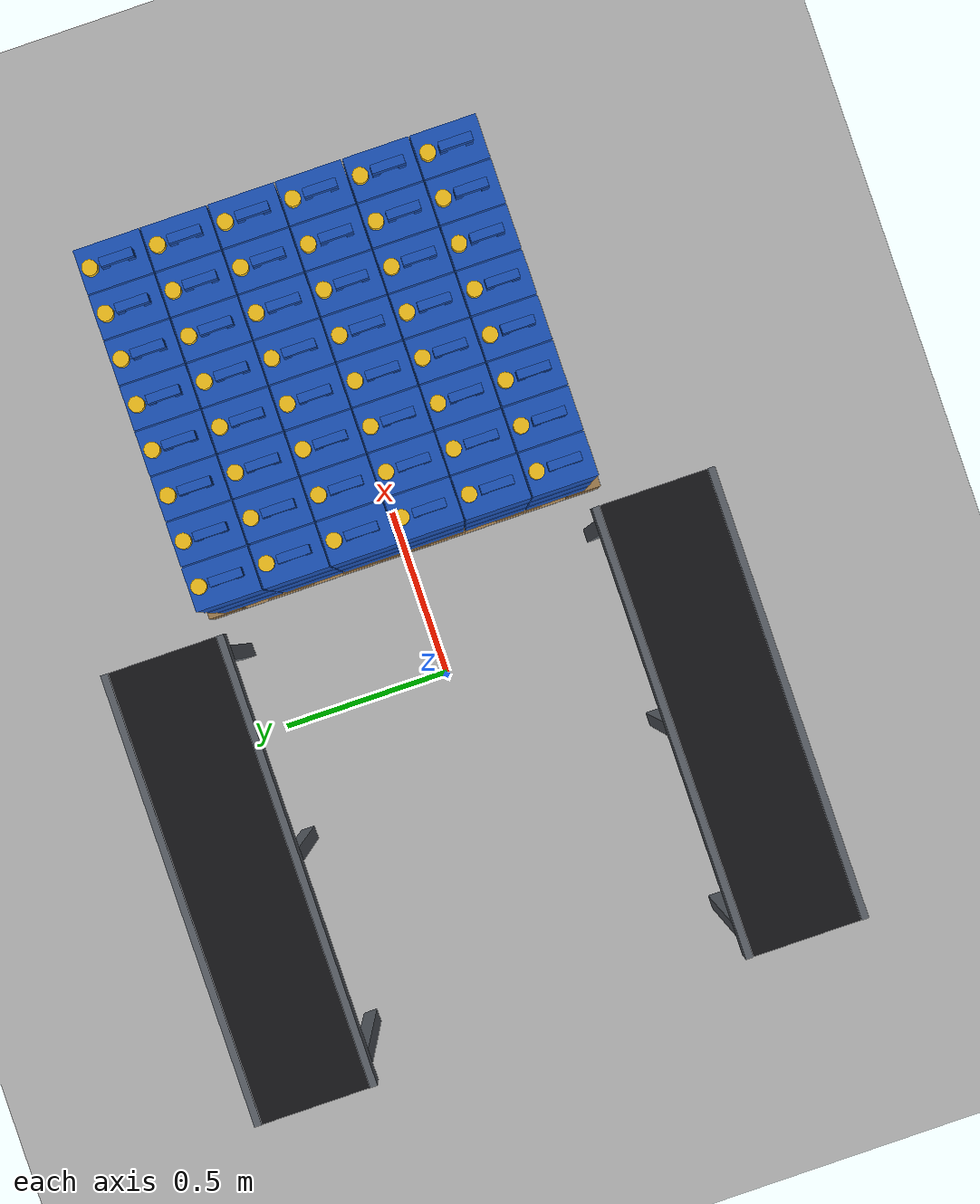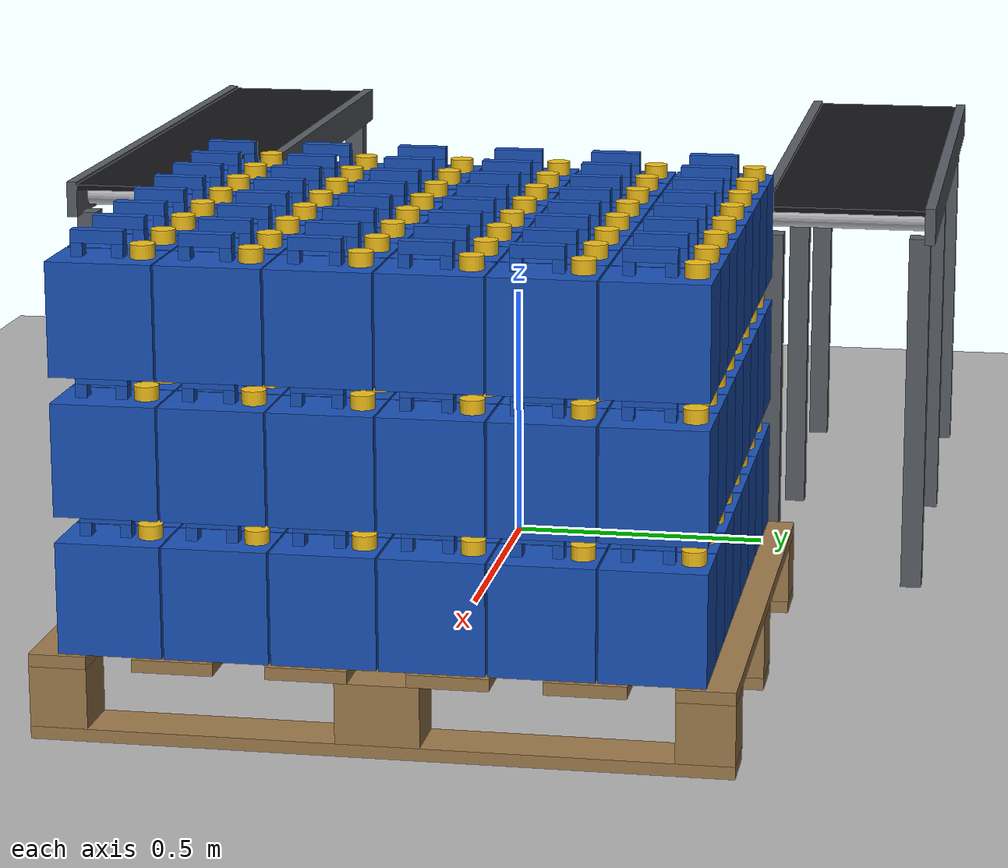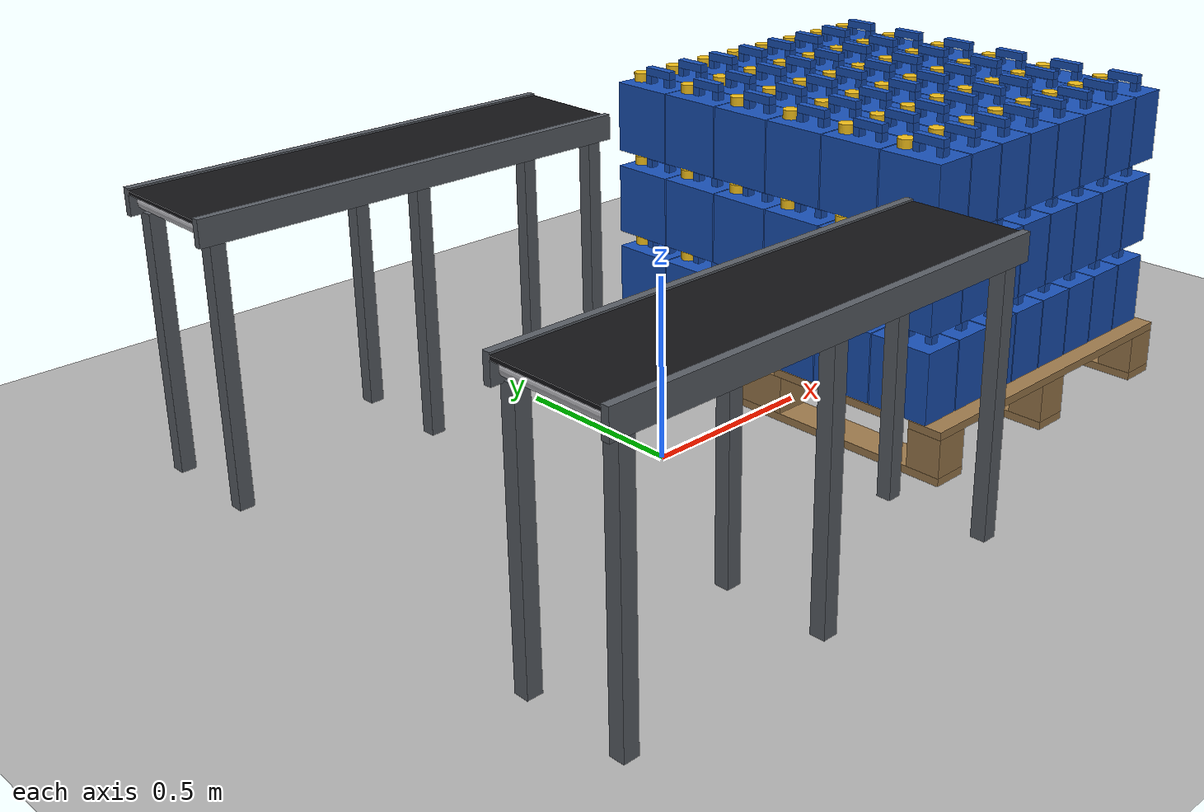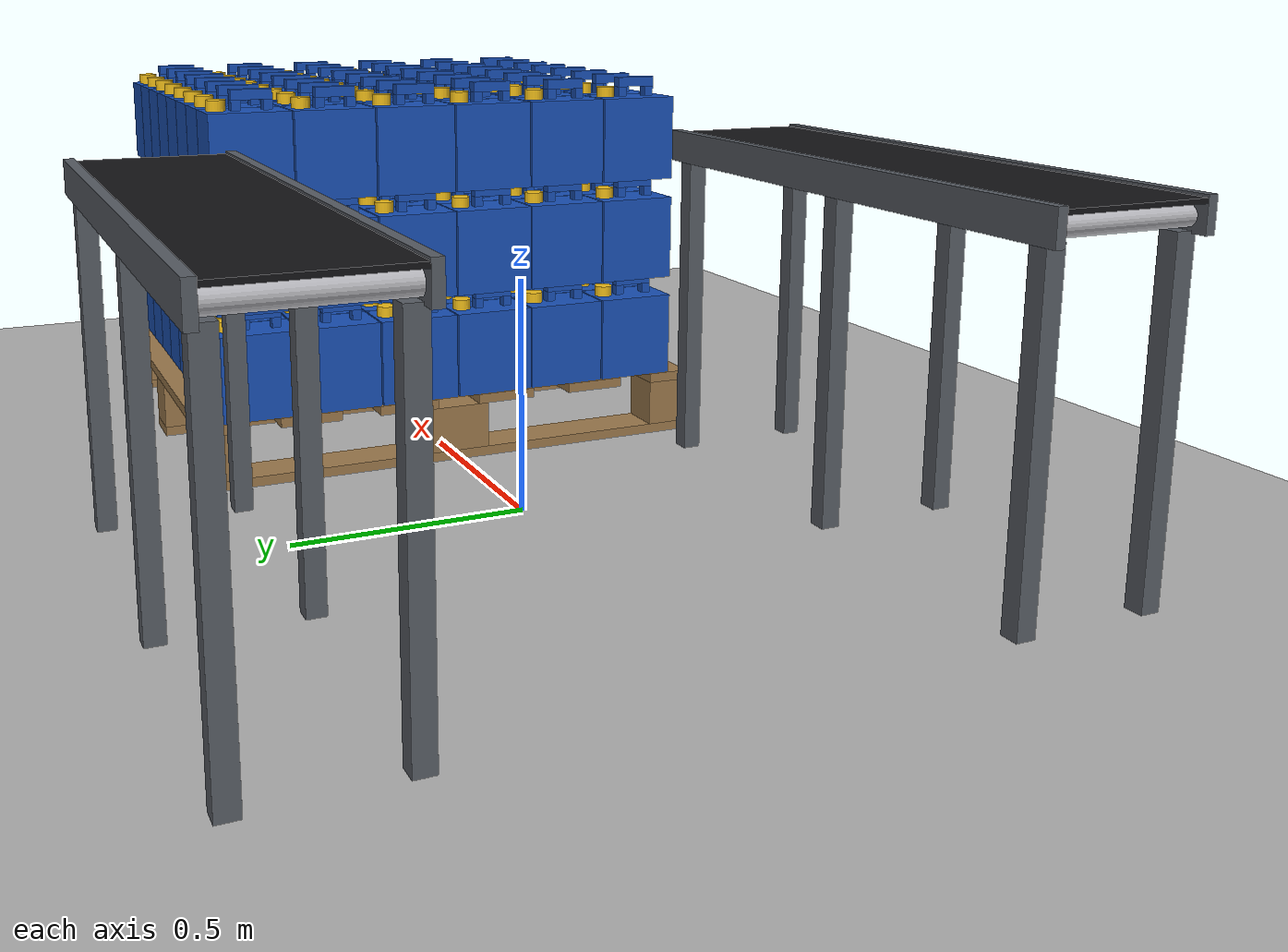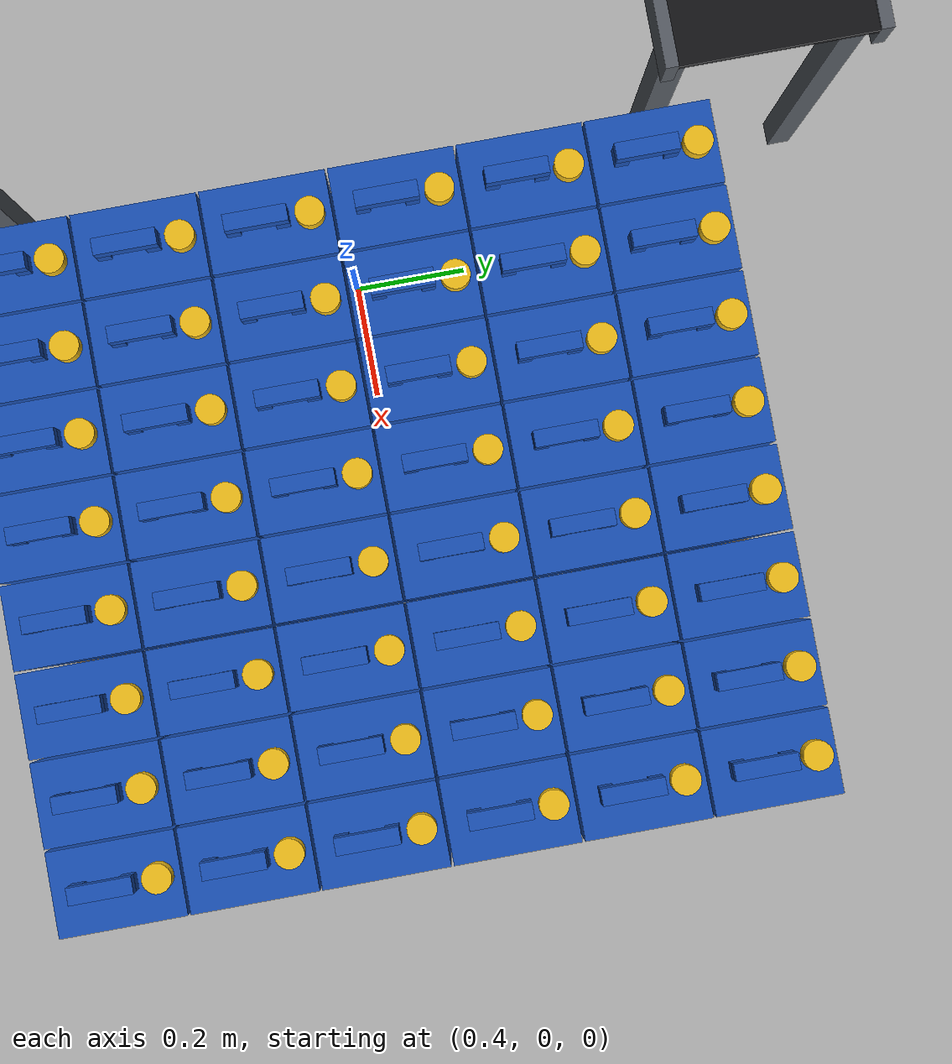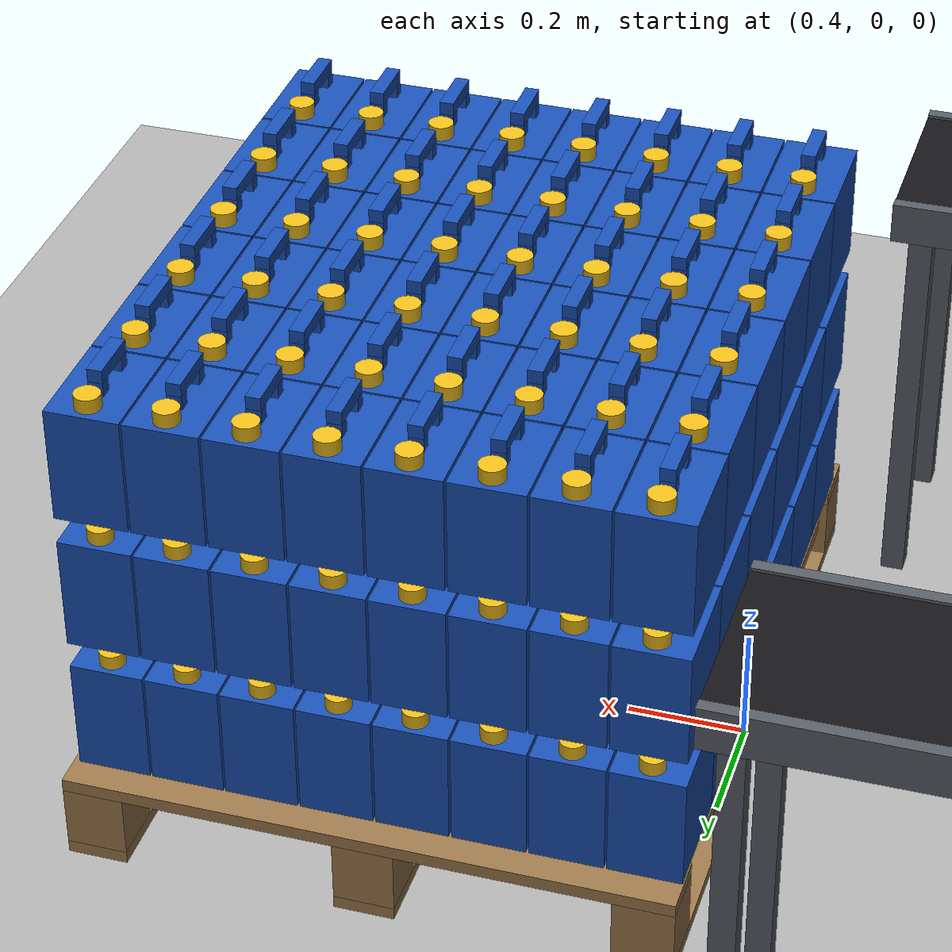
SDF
<?xml version="1.0"?>
<sdf version="1.8">
  <world name="moz1_jerrycan">
    <plugin filename="ignition-gazebo-physics-system" name="ignition::gazebo::systems::Physics"/>
    <plugin filename="ignition-gazebo-user-commands-system" name="ignition::gazebo::systems::UserCommands"/>
    <plugin filename="ignition-gazebo-scene-broadcaster-system" name="ignition::gazebo::systems::SceneBroadcaster"/>
    <plugin filename="ignition-gazebo-sensors-system" name="ignition::gazebo::systems::Sensors">
      <render_engine>ogre2</render_engine>
    </plugin>
    <plugin filename="ignition-gazebo-imu-system" name="ignition::gazebo::systems::Imu"/>

    <physics name="step" type="ignored">
      <max_step_size>0.004</max_step_size>
      <real_time_factor>1.0</real_time_factor>
    </physics>
    <scene><ambient>0.6 0.6 0.6 1</ambient><grid>false</grid></scene>

    <gui fullscreen="0">
      <camera name="user_camera"><pose>2.6 -2.2 2.1 0 0.42 2.45</pose></camera>
    </gui>

    <light type="directional" name="sun">
      <cast_shadows>false</cast_shadows>
      <pose>0 0 10 0 0 0</pose><diffuse>0.9 0.9 0.9 1</diffuse><specular>0.2 0.2 0.2 1</specular>
      <direction>-0.5 0.3 -1</direction>
    </light>

    <model name="ground_plane"><static>true</static>
      <link name="link">
        <collision name="c"><geometry><plane><normal>0 0 1</normal><size>100 100</size></plane></geometry></collision>
        <visual name="v"><geometry><plane><normal>0 0 1</normal><size>100 100</size></plane></geometry>
          <material><ambient>0.7 0.7 0.7 1</ambient><diffuse>0.7 0.7 0.7 1</diffuse></material></visual>
      </link>
    </model>

    <!-- EUR pallet 1200 x 1000 x 150 mm; robot works from the 1200 mm side -->
    <model name="pallet"><static>true</static><pose>0.3710 0.0000 0.0000 0 0 0</pose>
      <link name="link">
        <collision name="c"><pose>0.5000 0.0000 0.0750 0 0 0</pose><geometry><box><size>1.0000 1.2000 0.1500</size></box></geometry></collision>
        <visual name="deck0"><pose>0.5000 -0.5500 0.1390 0 0 0</pose><geometry><box><size>1.0000 0.1000 0.0220</size></box></geometry><material><ambient>0.62 0.48 0.30 1</ambient><diffuse>0.62 0.48 0.30 1</diffuse></material></visual>
<visual name="deck1"><pose>0.5000 -0.3500 0.1390 0 0 0</pose><geometry><box><size>1.0000 0.1400 0.0220</size></box></geometry><material><ambient>0.62 0.48 0.30 1</ambient><diffuse>0.62 0.48 0.30 1</diffuse></material></visual>
<visual name="deck2"><pose>0.5000 -0.1200 0.1390 0 0 0</pose><geometry><box><size>1.0000 0.1400 0.0220</size></box></geometry><material><ambient>0.62 0.48 0.30 1</ambient><diffuse>0.62 0.48 0.30 1</diffuse></material></visual>
<visual name="deck3"><pose>0.5000 0.1200 0.1390 0 0 0</pose><geometry><box><size>1.0000 0.1400 0.0220</size></box></geometry><material><ambient>0.62 0.48 0.30 1</ambient><diffuse>0.62 0.48 0.30 1</diffuse></material></visual>
<visual name="deck4"><pose>0.5000 0.3500 0.1390 0 0 0</pose><geometry><box><size>1.0000 0.1400 0.0220</size></box></geometry><material><ambient>0.62 0.48 0.30 1</ambient><diffuse>0.62 0.48 0.30 1</diffuse></material></visual>
<visual name="deck5"><pose>0.5000 0.5500 0.1390 0 0 0</pose><geometry><box><size>1.0000 0.1000 0.0220</size></box></geometry><material><ambient>0.62 0.48 0.30 1</ambient><diffuse>0.62 0.48 0.30 1</diffuse></material></visual>
<visual name="bottom0"><pose>0.0500 0.0000 0.0110 0 0 0</pose><geometry><box><size>0.1000 1.2000 0.0220</size></box></geometry><material><ambient>0.62 0.48 0.30 1</ambient><diffuse>0.62 0.48 0.30 1</diffuse></material></visual>
<visual name="block00"><pose>0.0500 -0.5500 0.0750 0 0 0</pose><geometry><box><size>0.1000 0.1000 0.1060</size></box></geometry><material><ambient>0.62 0.48 0.30 1</ambient><diffuse>0.62 0.48 0.30 1</diffuse></material></visual>
<visual name="block01"><pose>0.0500 0.0000 0.0750 0 0 0</pose><geometry><box><size>0.1000 0.1450 0.1060</size></box></geometry><material><ambient>0.62 0.48 0.30 1</ambient><diffuse>0.62 0.48 0.30 1</diffuse></material></visual>
<visual name="block02"><pose>0.0500 0.5500 0.0750 0 0 0</pose><geometry><box><size>0.1000 0.1000 0.1060</size></box></geometry><material><ambient>0.62 0.48 0.30 1</ambient><diffuse>0.62 0.48 0.30 1</diffuse></material></visual>
<visual name="bottom1"><pose>0.5000 0.0000 0.0110 0 0 0</pose><geometry><box><size>0.1000 1.2000 0.0220</size></box></geometry><material><ambient>0.62 0.48 0.30 1</ambient><diffuse>0.62 0.48 0.30 1</diffuse></material></visual>
<visual name="block10"><pose>0.5000 -0.5500 0.0750 0 0 0</pose><geometry><box><size>0.1000 0.1000 0.1060</size></box></geometry><material><ambient>0.62 0.48 0.30 1</ambient><diffuse>0.62 0.48 0.30 1</diffuse></material></visual>
<visual name="block11"><pose>0.5000 0.0000 0.0750 0 0 0</pose><geometry><box><size>0.1000 0.1450 0.1060</size></box></geometry><material><ambient>0.62 0.48 0.30 1</ambient><diffuse>0.62 0.48 0.30 1</diffuse></material></visual>
<visual name="block12"><pose>0.5000 0.5500 0.0750 0 0 0</pose><geometry><box><size>0.1000 0.1000 0.1060</size></box></geometry><material><ambient>0.62 0.48 0.30 1</ambient><diffuse>0.62 0.48 0.30 1</diffuse></material></visual>
<visual name="bottom2"><pose>0.9500 0.0000 0.0110 0 0 0</pose><geometry><box><size>0.1000 1.2000 0.0220</size></box></geometry><material><ambient>0.62 0.48 0.30 1</ambient><diffuse>0.62 0.48 0.30 1</diffuse></material></visual>
<visual name="block20"><pose>0.9500 -0.5500 0.0750 0 0 0</pose><geometry><box><size>0.1000 0.1000 0.1060</size></box></geometry><material><ambient>0.62 0.48 0.30 1</ambient><diffuse>0.62 0.48 0.30 1</diffuse></material></visual>
<visual name="block21"><pose>0.9500 0.0000 0.0750 0 0 0</pose><geometry><box><size>0.1000 0.1450 0.1060</size></box></geometry><material><ambient>0.62 0.48 0.30 1</ambient><diffuse>0.62 0.48 0.30 1</diffuse></material></visual>
<visual name="block22"><pose>0.9500 0.5500 0.0750 0 0 0</pose><geometry><box><size>0.1000 0.1000 0.1060</size></box></geometry><material><ambient>0.62 0.48 0.30 1</ambient><diffuse>0.62 0.48 0.30 1</diffuse></material></visual>
      </link>
    </model>
    <!-- 4 L jerry cans (3H1/Y1.4/100/26), 3 layer(s) x 8 rows x
         6 cols, static apart from the top layer's front row -->
    <model name="jerrycan_stack"><static>true</static><pose>0 0 0 0 0 0</pose>
      <link name="link">
        <collision name="c0_envelope_c"><pose>0.4330 -0.4600 0.2700 0 0 0</pose><geometry><box><size>0.1200 0.1800 0.2400</size></box></geometry></collision>
        <visual name="c0_body"><pose>0.4330 -0.4600 0.2475 0 0 0</pose><geometry><box><size>0.1200 0.1800 0.1950</size></box></geometry><material><ambient>0.10 0.32 0.72 1</ambient><diffuse>0.10 0.32 0.72 1</diffuse></material></visual>
        <visual name="c0_bar"><pose>0.4330 -0.4750 0.3790 0 0 0</pose><geometry><box><size>0.0240 0.0900 0.0220</size></box></geometry><material><ambient>0.10 0.32 0.72 1</ambient><diffuse>0.10 0.32 0.72 1</diffuse></material></visual>
        <visual name="c0_post_a"><pose>0.4330 -0.5100 0.3565 0 0 0</pose><geometry><box><size>0.0240 0.0200 0.0230</size></box></geometry><material><ambient>0.10 0.32 0.72 1</ambient><diffuse>0.10 0.32 0.72 1</diffuse></material></visual>
        <visual name="c0_post_b"><pose>0.4330 -0.4400 0.3565 0 0 0</pose><geometry><box><size>0.0240 0.0200 0.0230</size></box></geometry><material><ambient>0.10 0.32 0.72 1</ambient><diffuse>0.10 0.32 0.72 1</diffuse></material></visual>
        <visual name="c0_cap"><pose>0.4330 -0.4000 0.3570 0 0 0</pose><geometry><cylinder><radius>0.021</radius><length>0.024</length></cylinder></geometry><material><ambient>0.95 0.75 0.10 1</ambient><diffuse>0.95 0.75 0.10 1</diffuse></material></visual>
        <collision name="c1_envelope_c"><pose>0.4330 -0.2760 0.2700 0 0 0</pose><geometry><box><size>0.1200 0.1800 0.2400</size></box></geometry></collision>
        <visual name="c1_body"><pose>0.4330 -0.2760 0.2475 0 0 0</pose><geometry><box><size>0.1200 0.1800 0.1950</size></box></geometry><material><ambient>0.10 0.32 0.72 1</ambient><diffuse>0.10 0.32 0.72 1</diffuse></material></visual>
        <visual name="c1_bar"><pose>0.4330 -0.2910 0.3790 0 0 0</pose><geometry><box><size>0.0240 0.0900 0.0220</size></box></geometry><material><ambient>0.10 0.32 0.72 1</ambient><diffuse>0.10 0.32 0.72 1</diffuse></material></visual>
        <visual name="c1_post_a"><pose>0.4330 -0.3260 0.3565 0 0 0</pose><geometry><box><size>0.0240 0.0200 0.0230</size></box></geometry><material><ambient>0.10 0.32 0.72 1</ambient><diffuse>0.10 0.32 0.72 1</diffuse></material></visual>
        <visual name="c1_post_b"><pose>0.4330 -0.2560 0.3565 0 0 0</pose><geometry><box><size>0.0240 0.0200 0.0230</size></box></geometry><material><ambient>0.10 0.32 0.72 1</ambient><diffuse>0.10 0.32 0.72 1</diffuse></material></visual>
        <visual name="c1_cap"><pose>0.4330 -0.2160 0.3570 0 0 0</pose><geometry><cylinder><radius>0.021</radius><length>0.024</length></cylinder></geometry><material><ambient>0.95 0.75 0.10 1</ambient><diffuse>0.95 0.75 0.10 1</diffuse></material></visual>
        <collision name="c2_envelope_c"><pose>0.4330 -0.0920 0.2700 0 0 0</pose><geometry><box><size>0.1200 0.1800 0.2400</size></box></geometry></collision>
        <visual name="c2_body"><pose>0.4330 -0.0920 0.2475 0 0 0</pose><geometry><box><size>0.1200 0.1800 0.1950</size></box></geometry><material><ambient>0.10 0.32 0.72 1</ambient><diffuse>0.10 0.32 0.72 1</diffuse></material></visual>
        <visual name="c2_bar"><pose>0.4330 -0.1070 0.3790 0 0 0</pose><geometry><box><size>0.0240 0.0900 0.0220</size></box></geometry><material><ambient>0.10 0.32 0.72 1</ambient><diffuse>0.10 0.32 0.72 1</diffuse></material></visual>
        <visual name="c2_post_a"><pose>0.4330 -0.1420 0.3565 0 0 0</pose><geometry><box><size>0.0240 0.0200 0.0230</size></box></geometry><material><ambient>0.10 0.32 0.72 1</ambient><diffuse>0.10 0.32 0.72 1</diffuse></material></visual>
        <visual name="c2_post_b"><pose>0.4330 -0.0720 0.3565 0 0 0</pose><geometry><box><size>0.0240 0.0200 0.0230</size></box></geometry><material><ambient>0.10 0.32 0.72 1</ambient><diffuse>0.10 0.32 0.72 1</diffuse></material></visual>
        <visual name="c2_cap"><pose>0.4330 -0.0320 0.3570 0 0 0</pose><geometry><cylinder><radius>0.021</radius><length>0.024</length></cylinder></geometry><material><ambient>0.95 0.75 0.10 1</ambient><diffuse>0.95 0.75 0.10 1</diffuse></material></visual>
        <collision name="c3_envelope_c"><pose>0.4330 0.0920 0.2700 0 0 0</pose><geometry><box><size>0.1200 0.1800 0.2400</size></box></geometry></collision>
        <visual name="c3_body"><pose>0.4330 0.0920 0.2475 0 0 0</pose><geometry><box><size>0.1200 0.1800 0.1950</size></box></geometry><material><ambient>0.10 0.32 0.72 1</ambient><diffuse>0.10 0.32 0.72 1</diffuse></material></visual>
        <visual name="c3_bar"><pose>0.4330 0.0770 0.3790 0 0 0</pose><geometry><box><size>0.0240 0.0900 0.0220</size></box></geometry><material><ambient>0.10 0.32 0.72 1</ambient><diffuse>0.10 0.32 0.72 1</diffuse></material></visual>
        <visual name="c3_post_a"><pose>0.4330 0.0420 0.3565 0 0 0</pose><geometry><box><size>0.0240 0.0200 0.0230</size></box></geometry><material><ambient>0.10 0.32 0.72 1</ambient><diffuse>0.10 0.32 0.72 1</diffuse></material></visual>
        <visual name="c3_post_b"><pose>0.4330 0.1120 0.3565 0 0 0</pose><geometry><box><size>0.0240 0.0200 0.0230</size></box></geometry><material><ambient>0.10 0.32 0.72 1</ambient><diffuse>0.10 0.32 0.72 1</diffuse></material></visual>
        <visual name="c3_cap"><pose>0.4330 0.1520 0.3570 0 0 0</pose><geometry><cylinder><radius>0.021</radius><length>0.024</length></cylinder></geometry><material><ambient>0.95 0.75 0.10 1</ambient><diffuse>0.95 0.75 0.10 1</diffuse></material></visual>
        <collision name="c4_envelope_c"><pose>0.4330 0.2760 0.2700 0 0 0</pose><geometry><box><size>0.1200 0.1800 0.2400</size></box></geometry></collision>
        <visual name="c4_body"><pose>0.4330 0.2760 0.2475 0 0 0</pose><geometry><box><size>0.1200 0.1800 0.1950</size></box></geometry><material><ambient>0.10 0.32 0.72 1</ambient><diffuse>0.10 0.32 0.72 1</diffuse></material></visual>
        <visual name="c4_bar"><pose>0.4330 0.2610 0.3790 0 0 0</pose><geometry><box><size>0.0240 0.0900 0.0220</size></box></geometry><material><ambient>0.10 0.32 0.72 1</ambient><diffuse>0.10 0.32 0.72 1</diffuse></material></visual>
        <visual name="c4_post_a"><pose>0.4330 0.2260 0.3565 0 0 0</pose><geometry><box><size>0.0240 0.0200 0.0230</size></box></geometry><material><ambient>0.10 0.32 0.72 1</ambient><diffuse>0.10 0.32 0.72 1</diffuse></material></visual>
        <visual name="c4_post_b"><pose>0.4330 0.2960 0.3565 0 0 0</pose><geometry><box><size>0.0240 0.0200 0.0230</size></box></geometry><material><ambient>0.10 0.32 0.72 1</ambient><diffuse>0.10 0.32 0.72 1</diffuse></material></visual>
        <visual name="c4_cap"><pose>0.4330 0.3360 0.3570 0 0 0</pose><geometry><cylinder><radius>0.021</radius><length>0.024</length></cylinder></geometry><material><ambient>0.95 0.75 0.10 1</ambient><diffuse>0.95 0.75 0.10 1</diffuse></material></visual>
        <collision name="c5_envelope_c"><pose>0.4330 0.4600 0.2700 0 0 0</pose><geometry><box><size>0.1200 0.1800 0.2400</size></box></geometry></collision>
        <visual name="c5_body"><pose>0.4330 0.4600 0.2475 0 0 0</pose><geometry><box><size>0.1200 0.1800 0.1950</size></box></geometry><material><ambient>0.10 0.32 0.72 1</ambient><diffuse>0.10 0.32 0.72 1</diffuse></material></visual>
        <visual name="c5_bar"><pose>0.4330 0.4450 0.3790 0 0 0</pose><geometry><box><size>0.0240 0.0900 0.0220</size></box></geometry><material><ambient>0.10 0.32 0.72 1</ambient><diffuse>0.10 0.32 0.72 1</diffuse></material></visual>
        <visual name="c5_post_a"><pose>0.4330 0.4100 0.3565 0 0 0</pose><geometry><box><size>0.0240 0.0200 0.0230</size></box></geometry><material><ambient>0.10 0.32 0.72 1</ambient><diffuse>0.10 0.32 0.72 1</diffuse></material></visual>
        <visual name="c5_post_b"><pose>0.4330 0.4800 0.3565 0 0 0</pose><geometry><box><size>0.0240 0.0200 0.0230</size></box></geometry><material><ambient>0.10 0.32 0.72 1</ambient><diffuse>0.10 0.32 0.72 1</diffuse></material></visual>
        <visual name="c5_cap"><pose>0.4330 0.5200 0.3570 0 0 0</pose><geometry><cylinder><radius>0.021</radius><length>0.024</length></cylinder></geometry><material><ambient>0.95 0.75 0.10 1</ambient><diffuse>0.95 0.75 0.10 1</diffuse></material></visual>
        <collision name="c6_envelope_c"><pose>0.5570 -0.4600 0.2700 0 0 0</pose><geometry><box><size>0.1200 0.1800 0.2400</size></box></geometry></collision>
        <visual name="c6_body"><pose>0.5570 -0.4600 0.2475 0 0 0</pose><geometry><box><size>0.1200 0.1800 0.1950</size></box></geometry><material><ambient>0.10 0.32 0.72 1</ambient><diffuse>0.10 0.32 0.72 1</diffuse></material></visual>
        <visual name="c6_bar"><pose>0.5570 -0.4750 0.3790 0 0 0</pose><geometry><box><size>0.0240 0.0900 0.0220</size></box></geometry><material><ambient>0.10 0.32 0.72 1</ambient><diffuse>0.10 0.32 0.72 1</diffuse></material></visual>
        <visual name="c6_post_a"><pose>0.5570 -0.5100 0.3565 0 0 0</pose><geometry><box><size>0.0240 0.0200 0.0230</size></box></geometry><material><ambient>0.10 0.32 0.72 1</ambient><diffuse>0.10 0.32 0.72 1</diffuse></material></visual>
        <visual name="c6_post_b"><pose>0.5570 -0.4400 0.3565 0 0 0</pose><geometry><box><size>0.0240 0.0200 0.0230</size></box></geometry><material><ambient>0.10 0.32 0.72 1</ambient><diffuse>0.10 0.32 0.72 1</diffuse></material></visual>
        <visual name="c6_cap"><pose>0.5570 -0.4000 0.3570 0 0 0</pose><geometry><cylinder><radius>0.021</radius><length>0.024</length></cylinder></geometry><material><ambient>0.95 0.75 0.10 1</ambient><diffuse>0.95 0.75 0.10 1</diffuse></material></visual>
        <collision name="c7_envelope_c"><pose>0.5570 -0.2760 0.2700 0 0 0</pose><geometry><box><size>0.1200 0.1800 0.2400</size></box></geometry></collision>
        <visual name="c7_body"><pose>0.5570 -0.2760 0.2475 0 0 0</pose><geometry><box><size>0.1200 0.1800 0.1950</size></box></geometry><material><ambient>0.10 0.32 0.72 1</ambient><diffuse>0.10 0.32 0.72 1</diffuse></material></visual>
        <visual name="c7_bar"><pose>0.5570 -0.2910 0.3790 0 0 0</pose><geometry><box><size>0.0240 0.0900 0.0220</size></box></geometry><material><ambient>0.10 0.32 0.72 1</ambient><diffuse>0.10 0.32 0.72 1</diffuse></material></visual>
        <visual name="c7_post_a"><pose>0.5570 -0.3260 0.3565 0 0 0</pose><geometry><box><size>0.0240 0.0200 0.0230</size></box></geometry><material><ambient>0.10 0.32 0.72 1</ambient><diffuse>0.10 0.32 0.72 1</diffuse></material></visual>
        <visual name="c7_post_b"><pose>0.5570 -0.2560 0.3565 0 0 0</pose><geometry><box><size>0.0240 0.0200 0.0230</size></box></geometry><material><ambient>0.10 0.32 0.72 1</ambient><diffuse>0.10 0.32 0.72 1</diffuse></material></visual>
        <visual name="c7_cap"><pose>0.5570 -0.2160 0.3570 0 0 0</pose><geometry><cylinder><radius>0.021</radius><length>0.024</length></cylinder></geometry><material><ambient>0.95 0.75 0.10 1</ambient><diffuse>0.95 0.75 0.10 1</diffuse></material></visual>
        <collision name="c8_envelope_c"><pose>0.5570 -0.0920 0.2700 0 0 0</pose><geometry><box><size>0.1200 0.1800 0.2400</size></box></geometry></collision>
        <visual name="c8_body"><pose>0.5570 -0.0920 0.2475 0 0 0</pose><geometry><box><size>0.1200 0.1800 0.1950</size></box></geometry><material><ambient>0.10 0.32 0.72 1</ambient><diffuse>0.10 0.32 0.72 1</diffuse></material></visual>
        <visual name="c8_bar"><pose>0.5570 -0.1070 0.3790 0 0 0</pose><geometry><box><size>0.0240 0.0900 0.0220</size></box></geometry><material><ambient>0.10 0.32 0.72 1</ambient><diffuse>0.10 0.32 0.72 1</diffuse></material></visual>
        <visual name="c8_post_a"><pose>0.5570 -0.1420 0.3565 0 0 0</pose><geometry><box><size>0.0240 0.0200 0.0230</size></box></geometry><material><ambient>0.10 0.32 0.72 1</ambient><diffuse>0.10 0.32 0.72 1</diffuse></material></visual>
        <visual name="c8_post_b"><pose>0.5570 -0.0720 0.3565 0 0 0</pose><geometry><box><size>0.0240 0.0200 0.0230</size></box></geometry><material><ambient>0.10 0.32 0.72 1</ambient><diffuse>0.10 0.32 0.72 1</diffuse></material></visual>
        <visual name="c8_cap"><pose>0.5570 -0.0320 0.3570 0 0 0</pose><geometry><cylinder><radius>0.021</radius><length>0.024</length></cylinder></geometry><material><ambient>0.95 0.75 0.10 1</ambient><diffuse>0.95 0.75 0.10 1</diffuse></material></visual>
        <collision name="c9_envelope_c"><pose>0.5570 0.0920 0.2700 0 0 0</pose><geometry><box><size>0.1200 0.1800 0.2400</size></box></geometry></collision>
        <visual name="c9_body"><pose>0.5570 0.0920 0.2475 0 0 0</pose><geometry><box><size>0.1200 0.1800 0.1950</size></box></geometry><material><ambient>0.10 0.32 0.72 1</ambient><diffuse>0.10 0.32 0.72 1</diffuse></material></visual>
        <visual name="c9_bar"><pose>0.5570 0.0770 0.3790 0 0 0</pose><geometry><box><size>0.0240 0.0900 0.0220</size></box></geometry><material><ambient>0.10 0.32 0.72 1</ambient><diffuse>0.10 0.32 0.72 1</diffuse></material></visual>
        <visual name="c9_post_a"><pose>0.5570 0.0420 0.3565 0 0 0</pose><geometry><box><size>0.0240 0.0200 0.0230</size></box></geometry><material><ambient>0.10 0.32 0.72 1</ambient><diffuse>0.10 0.32 0.72 1</diffuse></material></visual>
        <visual name="c9_post_b"><pose>0.5570 0.1120 0.3565 0 0 0</pose><geometry><box><size>0.0240 0.0200 0.0230</size></box></geometry><material><ambient>0.10 0.32 0.72 1</ambient><diffuse>0.10 0.32 0.72 1</diffuse></material></visual>
        <visual name="c9_cap"><pose>0.5570 0.1520 0.3570 0 0 0</pose><geometry><cylinder><radius>0.021</radius><length>0.024</length></cylinder></geometry><material><ambient>0.95 0.75 0.10 1</ambient><diffuse>0.95 0.75 0.10 1</diffuse></material></visual>
        <collision name="c10_envelope_c"><pose>0.5570 0.2760 0.2700 0 0 0</pose><geometry><box><size>0.1200 0.1800 0.2400</size></box></geometry></collision>
        <visual name="c10_body"><pose>0.5570 0.2760 0.2475 0 0 0</pose><geometry><box><size>0.1200 0.1800 0.1950</size></box></geometry><material><ambient>0.10 0.32 0.72 1</ambient><diffuse>0.10 0.32 0.72 1</diffuse></material></visual>
        <visual name="c10_bar"><pose>0.5570 0.2610 0.3790 0 0 0</pose><geometry><box><size>0.0240 0.0900 0.0220</size></box></geometry><material><ambient>0.10 0.32 0.72 1</ambient><diffuse>0.10 0.32 0.72 1</diffuse></material></visual>
        <visual name="c10_post_a"><pose>0.5570 0.2260 0.3565 0 0 0</pose><geometry><box><size>0.0240 0.0200 0.0230</size></box></geometry><material><ambient>0.10 0.32 0.72 1</ambient><diffuse>0.10 0.32 0.72 1</diffuse></material></visual>
        <visual name="c10_post_b"><pose>0.5570 0.2960 0.3565 0 0 0</pose><geometry><box><size>0.0240 0.0200 0.0230</size></box></geometry><material><ambient>0.10 0.32 0.72 1</ambient><diffuse>0.10 0.32 0.72 1</diffuse></material></visual>
        <visual name="c10_cap"><pose>0.5570 0.3360 0.3570 0 0 0</pose><geometry><cylinder><radius>0.021</radius><length>0.024</length></cylinder></geometry><material><ambient>0.95 0.75 0.10 1</ambient><diffuse>0.95 0.75 0.10 1</diffuse></material></visual>
        <collision name="c11_envelope_c"><pose>0.5570 0.4600 0.2700 0 0 0</pose><geometry><box><size>0.1200 0.1800 0.2400</size></box></geometry></collision>
        <visual name="c11_body"><pose>0.5570 0.4600 0.2475 0 0 0</pose><geometry><box><size>0.1200 0.1800 0.1950</size></box></geometry><material><ambient>0.10 0.32 0.72 1</ambient><diffuse>0.10 0.32 0.72 1</diffuse></material></visual>
        <visual name="c11_bar"><pose>0.5570 0.4450 0.3790 0 0 0</pose><geometry><box><size>0.0240 0.0900 0.0220</size></box></geometry><material><ambient>0.10 0.32 0.72 1</ambient><diffuse>0.10 0.32 0.72 1</diffuse></material></visual>
        <visual name="c11_post_a"><pose>0.5570 0.4100 0.3565 0 0 0</pose><geometry><box><size>0.0240 0.0200 0.0230</size></box></geometry><material><ambient>0.10 0.32 0.72 1</ambient><diffuse>0.10 0.32 0.72 1</diffuse></material></visual>
        <visual name="c11_post_b"><pose>0.5570 0.4800 0.3565 0 0 0</pose><geometry><box><size>0.0240 0.0200 0.0230</size></box></geometry><material><ambient>0.10 0.32 0.72 1</ambient><diffuse>0.10 0.32 0.72 1</diffuse></material></visual>
        <visual name="c11_cap"><pose>0.5570 0.5200 0.3570 0 0 0</pose><geometry><cylinder><radius>0.021</radius><length>0.024</length></cylinder></geometry><material><ambient>0.95 0.75 0.10 1</ambient><diffuse>0.95 0.75 0.10 1</diffuse></material></visual>
        <collision name="c12_envelope_c"><pose>0.6810 -0.4600 0.2700 0 0 0</pose><geometry><box><size>0.1200 0.1800 0.2400</size></box></geometry></collision>
        <visual name="c12_body"><pose>0.6810 -0.4600 0.2475 0 0 0</pose><geometry><box><size>0.1200 0.1800 0.1950</size></box></geometry><material><ambient>0.10 0.32 0.72 1</ambient><diffuse>0.10 0.32 0.72 1</diffuse></material></visual>
        <visual name="c12_bar"><pose>0.6810 -0.4750 0.3790 0 0 0</pose><geometry><box><size>0.0240 0.0900 0.0220</size></box></geometry><material><ambient>0.10 0.32 0.72 1</ambient><diffuse>0.10 0.32 0.72 1</diffuse></material></visual>
        <visual name="c12_post_a"><pose>0.6810 -0.5100 0.3565 0 0 0</pose><geometry><box><size>0.0240 0.0200 0.0230</size></box></geometry><material><ambient>0.10 0.32 0.72 1</ambient><diffuse>0.10 0.32 0.72 1</diffuse></material></visual>
        <visual name="c12_post_b"><pose>0.6810 -0.4400 0.3565 0 0 0</pose><geometry><box><size>0.0240 0.0200 0.0230</size></box></geometry><material><ambient>0.10 0.32 0.72 1</ambient><diffuse>0.10 0.32 0.72 1</diffuse></material></visual>
        <visual name="c12_cap"><pose>0.6810 -0.4000 0.3570 0 0 0</pose><geometry><cylinder><radius>0.021</radius><length>0.024</length></cylinder></geometry><material><ambient>0.95 0.75 0.10 1</ambient><diffuse>0.95 0.75 0.10 1</diffuse></material></visual>
        <collision name="c13_envelope_c"><pose>0.6810 -0.2760 0.2700 0 0 0</pose><geometry><box><size>0.1200 0.1800 0.2400</size></box></geometry></collision>
        <visual name="c13_body"><pose>0.6810 -0.2760 0.2475 0 0 0</pose><geometry><box><size>0.1200 0.1800 0.1950</size></box></geometry><material><ambient>0.10 0.32 0.72 1</ambient><diffuse>0.10 0.32 0.72 1</diffuse></material></visual>
        <visual name="c13_bar"><pose>0.6810 -0.2910 0.3790 0 0 0</pose><geometry><box><size>0.0240 0.0900 0.0220</size></box></geometry><material><ambient>0.10 0.32 0.72 1</ambient><diffuse>0.10 0.32 0.72 1</diffuse></material></visual>
        <visual name="c13_post_a"><pose>0.6810 -0.3260 0.3565 0 0 0</pose><geometry><box><size>0.0240 0.0200 0.0230</size></box></geometry><material><ambient>0.10 0.32 0.72 1</ambient><diffuse>0.10 0.32 0.72 1</diffuse></material></visual>
        <visual name="c13_post_b"><pose>0.6810 -0.2560 0.3565 0 0 0</pose><geometry><box><size>0.0240 0.0200 0.0230</size></box></geometry><material><ambient>0.10 0.32 0.72 1</ambient><diffuse>0.10 0.32 0.72 1</diffuse></material></visual>
        <visual name="c13_cap"><pose>0.6810 -0.2160 0.3570 0 0 0</pose><geometry><cylinder><radius>0.021</radius><length>0.024</length></cylinder></geometry><material><ambient>0.95 0.75 0.10 1</ambient><diffuse>0.95 0.75 0.10 1</diffuse></material></visual>
        <collision name="c14_envelope_c"><pose>0.6810 -0.0920 0.2700 0 0 0</pose><geometry><box><size>0.1200 0.1800 0.2400</size></box></geometry></collision>
        <visual name="c14_body"><pose>0.6810 -0.0920 0.2475 0 0 0</pose><geometry><box><size>0.1200 0.1800 0.1950</size></box></geometry><material><ambient>0.10 0.32 0.72 1</ambient><diffuse>0.10 0.32 0.72 1</diffuse></material></visual>
        <visual name="c14_bar"><pose>0.6810 -0.1070 0.3790 0 0 0</pose><geometry><box><size>0.0240 0.0900 0.0220</size></box></geometry><material><ambient>0.10 0.32 0.72 1</ambient><diffuse>0.10 0.32 0.72 1</diffuse></material></visual>
        <visual name="c14_post_a"><pose>0.6810 -0.1420 0.3565 0 0 0</pose><geometry><box><size>0.0240 0.0200 0.0230</size></box></geometry><material><ambient>0.10 0.32 0.72 1</ambient><diffuse>0.10 0.32 0.72 1</diffuse></material></visual>
        <visual name="c14_post_b"><pose>0.6810 -0.0720 0.3565 0 0 0</pose><geometry><box><size>0.0240 0.0200 0.0230</size></box></geometry><material><ambient>0.10 0.32 0.72 1</ambient><diffuse>0.10 0.32 0.72 1</diffuse></material></visual>
        <visual name="c14_cap"><pose>0.6810 -0.0320 0.3570 0 0 0</pose><geometry><cylinder><radius>0.021</radius><length>0.024</length></cylinder></geometry><material><ambient>0.95 0.75 0.10 1</ambient><diffuse>0.95 0.75 0.10 1</diffuse></material></visual>
        <collision name="c15_envelope_c"><pose>0.6810 0.0920 0.2700 0 0 0</pose><geometry><box><size>0.1200 0.1800 0.2400</size></box></geometry></collision>
        <visual name="c15_body"><pose>0.6810 0.0920 0.2475 0 0 0</pose><geometry><box><size>0.1200 0.1800 0.1950</size></box></geometry><material><ambient>0.10 0.32 0.72 1</ambient><diffuse>0.10 0.32 0.72 1</diffuse></material></visual>
        <visual name="c15_bar"><pose>0.6810 0.0770 0.3790 0 0 0</pose><geometry><box><size>0.0240 0.0900 0.0220</size></box></geometry><material><ambient>0.10 0.32 0.72 1</ambient><diffuse>0.10 0.32 0.72 1</diffuse></material></visual>
        <visual name="c15_post_a"><pose>0.6810 0.0420 0.3565 0 0 0</pose><geometry><box><size>0.0240 0.0200 0.0230</size></box></geometry><material><ambient>0.10 0.32 0.72 1</ambient><diffuse>0.10 0.32 0.72 1</diffuse></material></visual>
        <visual name="c15_post_b"><pose>0.6810 0.1120 0.3565 0 0 0</pose><geometry><box><size>0.0240 0.0200 0.0230</size></box></geometry><material><ambient>0.10 0.32 0.72 1</ambient><diffuse>0.10 0.32 0.72 1</diffuse></material></visual>
        <visual name="c15_cap"><pose>0.6810 0.1520 0.3570 0 0 0</pose><geometry><cylinder><radius>0.021</radius><length>0.024</length></cylinder></geometry><material><ambient>0.95 0.75 0.10 1</ambient><diffuse>0.95 0.75 0.10 1</diffuse></material></visual>
        <collision name="c16_envelope_c"><pose>0.6810 0.2760 0.2700 0 0 0</pose><geometry><box><size>0.1200 0.1800 0.2400</size></box></geometry></collision>
        <visual name="c16_body"><pose>0.6810 0.2760 0.2475 0 0 0</pose><geometry><box><size>0.1200 0.1800 0.1950</size></box></geometry><material><ambient>0.10 0.32 0.72 1</ambient><diffuse>0.10 0.32 0.72 1</diffuse></material></visual>
        <visual name="c16_bar"><pose>0.6810 0.2610 0.3790 0 0 0</pose><geometry><box><size>0.0240 0.0900 0.0220</size></box></geometry><material><ambient>0.10 0.32 0.72 1</ambient><diffuse>0.10 0.32 0.72 1</diffuse></material></visual>
        <visual name="c16_post_a"><pose>0.6810 0.2260 0.3565 0 0 0</pose><geometry><box><size>0.0240 0.0200 0.0230</size></box></geometry><material><ambient>0.10 0.32 0.72 1</ambient><diffuse>0.10 0.32 0.72 1</diffuse></material></visual>
        <visual name="c16_post_b"><pose>0.6810 0.2960 0.3565 0 0 0</pose><geometry><box><size>0.0240 0.0200 0.0230</size></box></geometry><material><ambient>0.10 0.32 0.72 1</ambient><diffuse>0.10 0.32 0.72 1</diffuse></material></visual>
        <visual name="c16_cap"><pose>0.6810 0.3360 0.3570 0 0 0</pose><geometry><cylinder><radius>0.021</radius><length>0.024</length></cylinder></geometry><material><ambient>0.95 0.75 0.10 1</ambient><diffuse>0.95 0.75 0.10 1</diffuse></material></visual>
        <collision name="c17_envelope_c"><pose>0.6810 0.4600 0.2700 0 0 0</pose><geometry><box><size>0.1200 0.1800 0.2400</size></box></geometry></collision>
        <visual name="c17_body"><pose>0.6810 0.4600 0.2475 0 0 0</pose><geometry><box><size>0.1200 0.1800 0.1950</size></box></geometry><material><ambient>0.10 0.32 0.72 1</ambient><diffuse>0.10 0.32 0.72 1</diffuse></material></visual>
        <visual name="c17_bar"><pose>0.6810 0.4450 0.3790 0 0 0</pose><geometry><box><size>0.0240 0.0900 0.0220</size></box></geometry><material><ambient>0.10 0.32 0.72 1</ambient><diffuse>0.10 0.32 0.72 1</diffuse></material></visual>
        <visual name="c17_post_a"><pose>0.6810 0.4100 0.3565 0 0 0</pose><geometry><box><size>0.0240 0.0200 0.0230</size></box></geometry><material><ambient>0.10 0.32 0.72 1</ambient><diffuse>0.10 0.32 0.72 1</diffuse></material></visual>
        <visual name="c17_post_b"><pose>0.6810 0.4800 0.3565 0 0 0</pose><geometry><box><size>0.0240 0.0200 0.0230</size></box></geometry><material><ambient>0.10 0.32 0.72 1</ambient><diffuse>0.10 0.32 0.72 1</diffuse></material></visual>
        <visual name="c17_cap"><pose>0.6810 0.5200 0.3570 0 0 0</pose><geometry><cylinder><radius>0.021</radius><length>0.024</length></cylinder></geometry><material><ambient>0.95 0.75 0.10 1</ambient><diffuse>0.95 0.75 0.10 1</diffuse></material></visual>
        <collision name="c18_envelope_c"><pose>0.8050 -0.4600 0.2700 0 0 0</pose><geometry><box><size>0.1200 0.1800 0.2400</size></box></geometry></collision>
        <visual name="c18_body"><pose>0.8050 -0.4600 0.2475 0 0 0</pose><geometry><box><size>0.1200 0.1800 0.1950</size></box></geometry><material><ambient>0.10 0.32 0.72 1</ambient><diffuse>0.10 0.32 0.72 1</diffuse></material></visual>
        <visual name="c18_bar"><pose>0.8050 -0.4750 0.3790 0 0 0</pose><geometry><box><size>0.0240 0.0900 0.0220</size></box></geometry><material><ambient>0.10 0.32 0.72 1</ambient><diffuse>0.10 0.32 0.72 1</diffuse></material></visual>
        <visual name="c18_post_a"><pose>0.8050 -0.5100 0.3565 0 0 0</pose><geometry><box><size>0.0240 0.0200 0.0230</size></box></geometry><material><ambient>0.10 0.32 0.72 1</ambient><diffuse>0.10 0.32 0.72 1</diffuse></material></visual>
        <visual name="c18_post_b"><pose>0.8050 -0.4400 0.3565 0 0 0</pose><geometry><box><size>0.0240 0.0200 0.0230</size></box></geometry><material><ambient>0.10 0.32 0.72 1</ambient><diffuse>0.10 0.32 0.72 1</diffuse></material></visual>
        <visual name="c18_cap"><pose>0.8050 -0.4000 0.3570 0 0 0</pose><geometry><cylinder><radius>0.021</radius><length>0.024</length></cylinder></geometry><material><ambient>0.95 0.75 0.10 1</ambient><diffuse>0.95 0.75 0.10 1</diffuse></material></visual>
        <collision name="c19_envelope_c"><pose>0.8050 -0.2760 0.2700 0 0 0</pose><geometry><box><size>0.1200 0.1800 0.2400</size></box></geometry></collision>
        <visual name="c19_body"><pose>0.8050 -0.2760 0.2475 0 0 0</pose><geometry><box><size>0.1200 0.1800 0.1950</size></box></geometry><material><ambient>0.10 0.32 0.72 1</ambient><diffuse>0.10 0.32 0.72 1</diffuse></material></visual>
        <visual name="c19_bar"><pose>0.8050 -0.2910 0.3790 0 0 0</pose><geometry><box><size>0.0240 0.0900 0.0220</size></box></geometry><material><ambient>0.10 0.32 0.72 1</ambient><diffuse>0.10 0.32 0.72 1</diffuse></material></visual>
        <visual name="c19_post_a"><pose>0.8050 -0.3260 0.3565 0 0 0</pose><geometry><box><size>0.0240 0.0200 0.0230</size></box></geometry><material><ambient>0.10 0.32 0.72 1</ambient><diffuse>0.10 0.32 0.72 1</diffuse></material></visual>
        <visual name="c19_post_b"><pose>0.8050 -0.2560 0.3565 0 0 0</pose><geometry><box><size>0.0240 0.0200 0.0230</size></box></geometry><material><ambient>0.10 0.32 0.72 1</ambient><diffuse>0.10 0.32 0.72 1</diffuse></material></visual>
        <visual name="c19_cap"><pose>0.8050 -0.2160 0.3570 0 0 0</pose><geometry><cylinder><radius>0.021</radius><length>0.024</length></cylinder></geometry><material><ambient>0.95 0.75 0.10 1</ambient><diffuse>0.95 0.75 0.10 1</diffuse></material></visual>
        <collision name="c20_envelope_c"><pose>0.8050 -0.0920 0.2700 0 0 0</pose><geometry><box><size>0.1200 0.1800 0.2400</size></box></geometry></collision>
        <visual name="c20_body"><pose>0.8050 -0.0920 0.2475 0 0 0</pose><geometry><box><size>0.1200 0.1800 0.1950</size></box></geometry><material><ambient>0.10 0.32 0.72 1</ambient><diffuse>0.10 0.32 0.72 1</diffuse></material></visual>
        <visual name="c20_bar"><pose>0.8050 -0.1070 0.3790 0 0 0</pose><geometry><box><size>0.0240 0.0900 0.0220</size></box></geometry><material><ambient>0.10 0.32 0.72 1</ambient><diffuse>0.10 0.32 0.72 1</diffuse></material></visual>
        <visual name="c20_post_a"><pose>0.8050 -0.1420 0.3565 0 0 0</pose><geometry><box><size>0.0240 0.0200 0.0230</size></box></geometry><material><ambient>0.10 0.32 0.72 1</ambient><diffuse>0.10 0.32 0.72 1</diffuse></material></visual>
        <visual name="c20_post_b"><pose>0.8050 -0.0720 0.3565 0 0 0</pose><geometry><box><size>0.0240 0.0200 0.0230</size></box></geometry><material><ambient>0.10 0.32 0.72 1</ambient><diffuse>0.10 0.32 0.72 1</diffuse></material></visual>
        <visual name="c20_cap"><pose>0.8050 -0.0320 0.3570 0 0 0</pose><geometry><cylinder><radius>0.021</radius><length>0.024</length></cylinder></geometry><material><ambient>0.95 0.75 0.10 1</ambient><diffuse>0.95 0.75 0.10 1</diffuse></material></visual>
        <collision name="c21_envelope_c"><pose>0.8050 0.0920 0.2700 0 0 0</pose><geometry><box><size>0.1200 0.1800 0.2400</size></box></geometry></collision>
        <visual name="c21_body"><pose>0.8050 0.0920 0.2475 0 0 0</pose><geometry><box><size>0.1200 0.1800 0.1950</size></box></geometry><material><ambient>0.10 0.32 0.72 1</ambient><diffuse>0.10 0.32 0.72 1</diffuse></material></visual>
        <visual name="c21_bar"><pose>0.8050 0.0770 0.3790 0 0 0</pose><geometry><box><size>0.0240 0.0900 0.0220</size></box></geometry><material><ambient>0.10 0.32 0.72 1</ambient><diffuse>0.10 0.32 0.72 1</diffuse></material></visual>
        <visual name="c21_post_a"><pose>0.8050 0.0420 0.3565 0 0 0</pose><geometry><box><size>0.0240 0.0200 0.0230</size></box></geometry><material><ambient>0.10 0.32 0.72 1</ambient><diffuse>0.10 0.32 0.72 1</diffuse></material></visual>
        <visual name="c21_post_b"><pose>0.8050 0.1120 0.3565 0 0 0</pose><geometry><box><size>0.0240 0.0200 0.0230</size></box></geometry><material><ambient>0.10 0.32 0.72 1</ambient><diffuse>0.10 0.32 0.72 1</diffuse></material></visual>
        <visual name="c21_cap"><pose>0.8050 0.1520 0.3570 0 0 0</pose><geometry><cylinder><radius>0.021</radius><length>0.024</length></cylinder></geometry><material><ambient>0.95 0.75 0.10 1</ambient><diffuse>0.95 0.75 0.10 1</diffuse></material></visual>
        <collision name="c22_envelope_c"><pose>0.8050 0.2760 0.2700 0 0 0</pose><geometry><box><size>0.1200 0.1800 0.2400</size></box></geometry></collision>
        <visual name="c22_body"><pose>0.8050 0.2760 0.2475 0 0 0</pose><geometry><box><size>0.1200 0.1800 0.1950</size></box></geometry><material><ambient>0.10 0.32 0.72 1</ambient><diffuse>0.10 0.32 0.72 1</diffuse></material></visual>
        <visual name="c22_bar"><pose>0.8050 0.2610 0.3790 0 0 0</pose><geometry><box><size>0.0240 0.0900 0.0220</size></box></geometry><material><ambient>0.10 0.32 0.72 1</ambient><diffuse>0.10 0.32 0.72 1</diffuse></material></visual>
        <visual name="c22_post_a"><pose>0.8050 0.2260 0.3565 0 0 0</pose><geometry><box><size>0.0240 0.0200 0.0230</size></box></geometry><material><ambient>0.10 0.32 0.72 1</ambient><diffuse>0.10 0.32 0.72 1</diffuse></material></visual>
        <visual name="c22_post_b"><pose>0.8050 0.2960 0.3565 0 0 0</pose><geometry><box><size>0.0240 0.0200 0.0230</size></box></geometry><material><ambient>0.10 0.32 0.72 1</ambient><diffuse>0.10 0.32 0.72 1</diffuse></material></visual>
        <visual name="c22_cap"><pose>0.8050 0.3360 0.3570 0 0 0</pose><geometry><cylinder><radius>0.021</radius><length>0.024</length></cylinder></geometry><material><ambient>0.95 0.75 0.10 1</ambient><diffuse>0.95 0.75 0.10 1</diffuse></material></visual>
        <collision name="c23_envelope_c"><pose>0.8050 0.4600 0.2700 0 0 0</pose><geometry><box><size>0.1200 0.1800 0.2400</size></box></geometry></collision>
        <visual name="c23_body"><pose>0.8050 0.4600 0.2475 0 0 0</pose><geometry><box><size>0.1200 0.1800 0.1950</size></box></geometry><material><ambient>0.10 0.32 0.72 1</ambient><diffuse>0.10 0.32 0.72 1</diffuse></material></visual>
        <visual name="c23_bar"><pose>0.8050 0.4450 0.3790 0 0 0</pose><geometry><box><size>0.0240 0.0900 0.0220</size></box></geometry><material><ambient>0.10 0.32 0.72 1</ambient><diffuse>0.10 0.32 0.72 1</diffuse></material></visual>
        <visual name="c23_post_a"><pose>0.8050 0.4100 0.3565 0 0 0</pose><geometry><box><size>0.0240 0.0200 0.0230</size></box></geometry><material><ambient>0.10 0.32 0.72 1</ambient><diffuse>0.10 0.32 0.72 1</diffuse></material></visual>
        <visual name="c23_post_b"><pose>0.8050 0.4800 0.3565 0 0 0</pose><geometry><box><size>0.0240 0.0200 0.0230</size></box></geometry><material><ambient>0.10 0.32 0.72 1</ambient><diffuse>0.10 0.32 0.72 1</diffuse></material></visual>
        <visual name="c23_cap"><pose>0.8050 0.5200 0.3570 0 0 0</pose><geometry><cylinder><radius>0.021</radius><length>0.024</length></cylinder></geometry><material><ambient>0.95 0.75 0.10 1</ambient><diffuse>0.95 0.75 0.10 1</diffuse></material></visual>
        <collision name="c24_envelope_c"><pose>0.9290 -0.4600 0.2700 0 0 0</pose><geometry><box><size>0.1200 0.1800 0.2400</size></box></geometry></collision>
        <visual name="c24_body"><pose>0.9290 -0.4600 0.2475 0 0 0</pose><geometry><box><size>0.1200 0.1800 0.1950</size></box></geometry><material><ambient>0.10 0.32 0.72 1</ambient><diffuse>0.10 0.32 0.72 1</diffuse></material></visual>
        <visual name="c24_bar"><pose>0.9290 -0.4750 0.3790 0 0 0</pose><geometry><box><size>0.0240 0.0900 0.0220</size></box></geometry><material><ambient>0.10 0.32 0.72 1</ambient><diffuse>0.10 0.32 0.72 1</diffuse></material></visual>
        <visual name="c24_post_a"><pose>0.9290 -0.5100 0.3565 0 0 0</pose><geometry><box><size>0.0240 0.0200 0.0230</size></box></geometry><material><ambient>0.10 0.32 0.72 1</ambient><diffuse>0.10 0.32 0.72 1</diffuse></material></visual>
        <visual name="c24_post_b"><pose>0.9290 -0.4400 0.3565 0 0 0</pose><geometry><box><size>0.0240 0.0200 0.0230</size></box></geometry><material><ambient>0.10 0.32 0.72 1</ambient><diffuse>0.10 0.32 0.72 1</diffuse></material></visual>
        <visual name="c24_cap"><pose>0.9290 -0.4000 0.3570 0 0 0</pose><geometry><cylinder><radius>0.021</radius><length>0.024</length></cylinder></geometry><material><ambient>0.95 0.75 0.10 1</ambient><diffuse>0.95 0.75 0.10 1</diffuse></material></visual>
        <collision name="c25_envelope_c"><pose>0.9290 -0.2760 0.2700 0 0 0</pose><geometry><box><size>0.1200 0.1800 0.2400</size></box></geometry></collision>
        <visual name="c25_body"><pose>0.9290 -0.2760 0.2475 0 0 0</pose><geometry><box><size>0.1200 0.1800 0.1950</size></box></geometry><material><ambient>0.10 0.32 0.72 1</ambient><diffuse>0.10 0.32 0.72 1</diffuse></material></visual>
        <visual name="c25_bar"><pose>0.9290 -0.2910 0.3790 0 0 0</pose><geometry><box><size>0.0240 0.0900 0.0220</size></box></geometry><material><ambient>0.10 0.32 0.72 1</ambient><diffuse>0.10 0.32 0.72 1</diffuse></material></visual>
        <visual name="c25_post_a"><pose>0.9290 -0.3260 0.3565 0 0 0</pose><geometry><box><size>0.0240 0.0200 0.0230</size></box></geometry><material><ambient>0.10 0.32 0.72 1</ambient><diffuse>0.10 0.32 0.72 1</diffuse></material></visual>
        <visual name="c25_post_b"><pose>0.9290 -0.2560 0.3565 0 0 0</pose><geometry><box><size>0.0240 0.0200 0.0230</size></box></geometry><material><ambient>0.10 0.32 0.72 1</ambient><diffuse>0.10 0.32 0.72 1</diffuse></material></visual>
        <visual name="c25_cap"><pose>0.9290 -0.2160 0.3570 0 0 0</pose><geometry><cylinder><radius>0.021</radius><length>0.024</length></cylinder></geometry><material><ambient>0.95 0.75 0.10 1</ambient><diffuse>0.95 0.75 0.10 1</diffuse></material></visual>
        <collision name="c26_envelope_c"><pose>0.9290 -0.0920 0.2700 0 0 0</pose><geometry><box><size>0.1200 0.1800 0.2400</size></box></geometry></collision>
        <visual name="c26_body"><pose>0.9290 -0.0920 0.2475 0 0 0</pose><geometry><box><size>0.1200 0.1800 0.1950</size></box></geometry><material><ambient>0.10 0.32 0.72 1</ambient><diffuse>0.10 0.32 0.72 1</diffuse></material></visual>
        <visual name="c26_bar"><pose>0.9290 -0.1070 0.3790 0 0 0</pose><geometry><box><size>0.0240 0.0900 0.0220</size></box></geometry><material><ambient>0.10 0.32 0.72 1</ambient><diffuse>0.10 0.32 0.72 1</diffuse></material></visual>
        <visual name="c26_post_a"><pose>0.9290 -0.1420 0.3565 0 0 0</pose><geometry><box><size>0.0240 0.0200 0.0230</size></box></geometry><material><ambient>0.10 0.32 0.72 1</ambient><diffuse>0.10 0.32 0.72 1</diffuse></material></visual>
        <visual name="c26_post_b"><pose>0.9290 -0.0720 0.3565 0 0 0</pose><geometry><box><size>0.0240 0.0200 0.0230</size></box></geometry><material><ambient>0.10 0.32 0.72 1</ambient><diffuse>0.10 0.32 0.72 1</diffuse></material></visual>
        <visual name="c26_cap"><pose>0.9290 -0.0320 0.3570 0 0 0</pose><geometry><cylinder><radius>0.021</radius><length>0.024</length></cylinder></geometry><material><ambient>0.95 0.75 0.10 1</ambient><diffuse>0.95 0.75 0.10 1</diffuse></material></visual>
        <collision name="c27_envelope_c"><pose>0.9290 0.0920 0.2700 0 0 0</pose><geometry><box><size>0.1200 0.1800 0.2400</size></box></geometry></collision>
        <visual name="c27_body"><pose>0.9290 0.0920 0.2475 0 0 0</pose><geometry><box><size>0.1200 0.1800 0.1950</size></box></geometry><material><ambient>0.10 0.32 0.72 1</ambient><diffuse>0.10 0.32 0.72 1</diffuse></material></visual>
        <visual name="c27_bar"><pose>0.9290 0.0770 0.3790 0 0 0</pose><geometry><box><size>0.0240 0.0900 0.0220</size></box></geometry><material><ambient>0.10 0.32 0.72 1</ambient><diffuse>0.10 0.32 0.72 1</diffuse></material></visual>
        <visual name="c27_post_a"><pose>0.9290 0.0420 0.3565 0 0 0</pose><geometry><box><size>0.0240 0.0200 0.0230</size></box></geometry><material><ambient>0.10 0.32 0.72 1</ambient><diffuse>0.10 0.32 0.72 1</diffuse></material></visual>
        <visual name="c27_post_b"><pose>0.9290 0.1120 0.3565 0 0 0</pose><geometry><box><size>0.0240 0.0200 0.0230</size></box></geometry><material><ambient>0.10 0.32 0.72 1</ambient><diffuse>0.10 0.32 0.72 1</diffuse></material></visual>
        <visual name="c27_cap"><pose>0.9290 0.1520 0.3570 0 0 0</pose><geometry><cylinder><radius>0.021</radius><length>0.024</length></cylinder></geometry><material><ambient>0.95 0.75 0.10 1</ambient><diffuse>0.95 0.75 0.10 1</diffuse></material></visual>
        <collision name="c28_envelope_c"><pose>0.9290 0.2760 0.2700 0 0 0</pose><geometry><box><size>0.1200 0.1800 0.2400</size></box></geometry></collision>
        <visual name="c28_body"><pose>0.9290 0.2760 0.2475 0 0 0</pose><geometry><box><size>0.1200 0.1800 0.1950</size></box></geometry><material><ambient>0.10 0.32 0.72 1</ambient><diffuse>0.10 0.32 0.72 1</diffuse></material></visual>
        <visual name="c28_bar"><pose>0.9290 0.2610 0.3790 0 0 0</pose><geometry><box><size>0.0240 0.0900 0.0220</size></box></geometry><material><ambient>0.10 0.32 0.72 1</ambient><diffuse>0.10 0.32 0.72 1</diffuse></material></visual>
        <visual name="c28_post_a"><pose>0.9290 0.2260 0.3565 0 0 0</pose><geometry><box><size>0.0240 0.0200 0.0230</size></box></geometry><material><ambient>0.10 0.32 0.72 1</ambient><diffuse>0.10 0.32 0.72 1</diffuse></material></visual>
        <visual name="c28_post_b"><pose>0.9290 0.2960 0.3565 0 0 0</pose><geometry><box><size>0.0240 0.0200 0.0230</size></box></geometry><material><ambient>0.10 0.32 0.72 1</ambient><diffuse>0.10 0.32 0.72 1</diffuse></material></visual>
        <visual name="c28_cap"><pose>0.9290 0.3360 0.3570 0 0 0</pose><geometry><cylinder><radius>0.021</radius><length>0.024</length></cylinder></geometry><material><ambient>0.95 0.75 0.10 1</ambient><diffuse>0.95 0.75 0.10 1</diffuse></material></visual>
        <collision name="c29_envelope_c"><pose>0.9290 0.4600 0.2700 0 0 0</pose><geometry><box><size>0.1200 0.1800 0.2400</size></box></geometry></collision>
        <visual name="c29_body"><pose>0.9290 0.4600 0.2475 0 0 0</pose><geometry><box><size>0.1200 0.1800 0.1950</size></box></geometry><material><ambient>0.10 0.32 0.72 1</ambient><diffuse>0.10 0.32 0.72 1</diffuse></material></visual>
        <visual name="c29_bar"><pose>0.9290 0.4450 0.3790 0 0 0</pose><geometry><box><size>0.0240 0.0900 0.0220</size></box></geometry><material><ambient>0.10 0.32 0.72 1</ambient><diffuse>0.10 0.32 0.72 1</diffuse></material></visual>
        <visual name="c29_post_a"><pose>0.9290 0.4100 0.3565 0 0 0</pose><geometry><box><size>0.0240 0.0200 0.0230</size></box></geometry><material><ambient>0.10 0.32 0.72 1</ambient><diffuse>0.10 0.32 0.72 1</diffuse></material></visual>
        <visual name="c29_post_b"><pose>0.9290 0.4800 0.3565 0 0 0</pose><geometry><box><size>0.0240 0.0200 0.0230</size></box></geometry><material><ambient>0.10 0.32 0.72 1</ambient><diffuse>0.10 0.32 0.72 1</diffuse></material></visual>
        <visual name="c29_cap"><pose>0.9290 0.5200 0.3570 0 0 0</pose><geometry><cylinder><radius>0.021</radius><length>0.024</length></cylinder></geometry><material><ambient>0.95 0.75 0.10 1</ambient><diffuse>0.95 0.75 0.10 1</diffuse></material></visual>
        <collision name="c30_envelope_c"><pose>1.0530 -0.4600 0.2700 0 0 0</pose><geometry><box><size>0.1200 0.1800 0.2400</size></box></geometry></collision>
        <visual name="c30_body"><pose>1.0530 -0.4600 0.2475 0 0 0</pose><geometry><box><size>0.1200 0.1800 0.1950</size></box></geometry><material><ambient>0.10 0.32 0.72 1</ambient><diffuse>0.10 0.32 0.72 1</diffuse></material></visual>
        <visual name="c30_bar"><pose>1.0530 -0.4750 0.3790 0 0 0</pose><geometry><box><size>0.0240 0.0900 0.0220</size></box></geometry><material><ambient>0.10 0.32 0.72 1</ambient><diffuse>0.10 0.32 0.72 1</diffuse></material></visual>
        <visual name="c30_post_a"><pose>1.0530 -0.5100 0.3565 0 0 0</pose><geometry><box><size>0.0240 0.0200 0.0230</size></box></geometry><material><ambient>0.10 0.32 0.72 1</ambient><diffuse>0.10 0.32 0.72 1</diffuse></material></visual>
        <visual name="c30_post_b"><pose>1.0530 -0.4400 0.3565 0 0 0</pose><geometry><box><size>0.0240 0.0200 0.0230</size></box></geometry><material><ambient>0.10 0.32 0.72 1</ambient><diffuse>0.10 0.32 0.72 1</diffuse></material></visual>
        <visual name="c30_cap"><pose>1.0530 -0.4000 0.3570 0 0 0</pose><geometry><cylinder><radius>0.021</radius><length>0.024</length></cylinder></geometry><material><ambient>0.95 0.75 0.10 1</ambient><diffuse>0.95 0.75 0.10 1</diffuse></material></visual>
        <collision name="c31_envelope_c"><pose>1.0530 -0.2760 0.2700 0 0 0</pose><geometry><box><size>0.1200 0.1800 0.2400</size></box></geometry></collision>
        <visual name="c31_body"><pose>1.0530 -0.2760 0.2475 0 0 0</pose><geometry><box><size>0.1200 0.1800 0.1950</size></box></geometry><material><ambient>0.10 0.32 0.72 1</ambient><diffuse>0.10 0.32 0.72 1</diffuse></material></visual>
        <visual name="c31_bar"><pose>1.0530 -0.2910 0.3790 0 0 0</pose><geometry><box><size>0.0240 0.0900 0.0220</size></box></geometry><material><ambient>0.10 0.32 0.72 1</ambient><diffuse>0.10 0.32 0.72 1</diffuse></material></visual>
        <visual name="c31_post_a"><pose>1.0530 -0.3260 0.3565 0 0 0</pose><geometry><box><size>0.0240 0.0200 0.0230</size></box></geometry><material><ambient>0.10 0.32 0.72 1</ambient><diffuse>0.10 0.32 0.72 1</diffuse></material></visual>
        <visual name="c31_post_b"><pose>1.0530 -0.2560 0.3565 0 0 0</pose><geometry><box><size>0.0240 0.0200 0.0230</size></box></geometry><material><ambient>0.10 0.32 0.72 1</ambient><diffuse>0.10 0.32 0.72 1</diffuse></material></visual>
        <visual name="c31_cap"><pose>1.0530 -0.2160 0.3570 0 0 0</pose><geometry><cylinder><radius>0.021</radius><length>0.024</length></cylinder></geometry><material><ambient>0.95 0.75 0.10 1</ambient><diffuse>0.95 0.75 0.10 1</diffuse></material></visual>
        <collision name="c32_envelope_c"><pose>1.0530 -0.0920 0.2700 0 0 0</pose><geometry><box><size>0.1200 0.1800 0.2400</size></box></geometry></collision>
        <visual name="c32_body"><pose>1.0530 -0.0920 0.2475 0 0 0</pose><geometry><box><size>0.1200 0.1800 0.1950</size></box></geometry><material><ambient>0.10 0.32 0.72 1</ambient><diffuse>0.10 0.32 0.72 1</diffuse></material></visual>
        <visual name="c32_bar"><pose>1.0530 -0.1070 0.3790 0 0 0</pose><geometry><box><size>0.0240 0.0900 0.0220</size></box></geometry><material><ambient>0.10 0.32 0.72 1</ambient><diffuse>0.10 0.32 0.72 1</diffuse></material></visual>
        <visual name="c32_post_a"><pose>1.0530 -0.1420 0.3565 0 0 0</pose><geometry><box><size>0.0240 0.0200 0.0230</size></box></geometry><material><ambient>0.10 0.32 0.72 1</ambient><diffuse>0.10 0.32 0.72 1</diffuse></material></visual>
        <visual name="c32_post_b"><pose>1.0530 -0.0720 0.3565 0 0 0</pose><geometry><box><size>0.0240 0.0200 0.0230</size></box></geometry><material><ambient>0.10 0.32 0.72 1</ambient><diffuse>0.10 0.32 0.72 1</diffuse></material></visual>
        <visual name="c32_cap"><pose>1.0530 -0.0320 0.3570 0 0 0</pose><geometry><cylinder><radius>0.021</radius><length>0.024</length></cylinder></geometry><material><ambient>0.95 0.75 0.10 1</ambient><diffuse>0.95 0.75 0.10 1</diffuse></material></visual>
        <collision name="c33_envelope_c"><pose>1.0530 0.0920 0.2700 0 0 0</pose><geometry><box><size>0.1200 0.1800 0.2400</size></box></geometry></collision>
        <visual name="c33_body"><pose>1.0530 0.0920 0.2475 0 0 0</pose><geometry><box><size>0.1200 0.1800 0.1950</size></box></geometry><material><ambient>0.10 0.32 0.72 1</ambient><diffuse>0.10 0.32 0.72 1</diffuse></material></visual>
        <visual name="c33_bar"><pose>1.0530 0.0770 0.3790 0 0 0</pose><geometry><box><size>0.0240 0.0900 0.0220</size></box></geometry><material><ambient>0.10 0.32 0.72 1</ambient><diffuse>0.10 0.32 0.72 1</diffuse></material></visual>
        <visual name="c33_post_a"><pose>1.0530 0.0420 0.3565 0 0 0</pose><geometry><box><size>0.0240 0.0200 0.0230</size></box></geometry><material><ambient>0.10 0.32 0.72 1</ambient><diffuse>0.10 0.32 0.72 1</diffuse></material></visual>
        <visual name="c33_post_b"><pose>1.0530 0.1120 0.3565 0 0 0</pose><geometry><box><size>0.0240 0.0200 0.0230</size></box></geometry><material><ambient>0.10 0.32 0.72 1</ambient><diffuse>0.10 0.32 0.72 1</diffuse></material></visual>
        <visual name="c33_cap"><pose>1.0530 0.1520 0.3570 0 0 0</pose><geometry><cylinder><radius>0.021</radius><length>0.024</length></cylinder></geometry><material><ambient>0.95 0.75 0.10 1</ambient><diffuse>0.95 0.75 0.10 1</diffuse></material></visual>
        <collision name="c34_envelope_c"><pose>1.0530 0.2760 0.2700 0 0 0</pose><geometry><box><size>0.1200 0.1800 0.2400</size></box></geometry></collision>
        <visual name="c34_body"><pose>1.0530 0.2760 0.2475 0 0 0</pose><geometry><box><size>0.1200 0.1800 0.1950</size></box></geometry><material><ambient>0.10 0.32 0.72 1</ambient><diffuse>0.10 0.32 0.72 1</diffuse></material></visual>
        <visual name="c34_bar"><pose>1.0530 0.2610 0.3790 0 0 0</pose><geometry><box><size>0.0240 0.0900 0.0220</size></box></geometry><material><ambient>0.10 0.32 0.72 1</ambient><diffuse>0.10 0.32 0.72 1</diffuse></material></visual>
        <visual name="c34_post_a"><pose>1.0530 0.2260 0.3565 0 0 0</pose><geometry><box><size>0.0240 0.0200 0.0230</size></box></geometry><material><ambient>0.10 0.32 0.72 1</ambient><diffuse>0.10 0.32 0.72 1</diffuse></material></visual>
        <visual name="c34_post_b"><pose>1.0530 0.2960 0.3565 0 0 0</pose><geometry><box><size>0.0240 0.0200 0.0230</size></box></geometry><material><ambient>0.10 0.32 0.72 1</ambient><diffuse>0.10 0.32 0.72 1</diffuse></material></visual>
        <visual name="c34_cap"><pose>1.0530 0.3360 0.3570 0 0 0</pose><geometry><cylinder><radius>0.021</radius><length>0.024</length></cylinder></geometry><material><ambient>0.95 0.75 0.10 1</ambient><diffuse>0.95 0.75 0.10 1</diffuse></material></visual>
        <collision name="c35_envelope_c"><pose>1.0530 0.4600 0.2700 0 0 0</pose><geometry><box><size>0.1200 0.1800 0.2400</size></box></geometry></collision>
        <visual name="c35_body"><pose>1.0530 0.4600 0.2475 0 0 0</pose><geometry><box><size>0.1200 0.1800 0.1950</size></box></geometry><material><ambient>0.10 0.32 0.72 1</ambient><diffuse>0.10 0.32 0.72 1</diffuse></material></visual>
        <visual name="c35_bar"><pose>1.0530 0.4450 0.3790 0 0 0</pose><geometry><box><size>0.0240 0.0900 0.0220</size></box></geometry><material><ambient>0.10 0.32 0.72 1</ambient><diffuse>0.10 0.32 0.72 1</diffuse></material></visual>
        <visual name="c35_post_a"><pose>1.0530 0.4100 0.3565 0 0 0</pose><geometry><box><size>0.0240 0.0200 0.0230</size></box></geometry><material><ambient>0.10 0.32 0.72 1</ambient><diffuse>0.10 0.32 0.72 1</diffuse></material></visual>
        <visual name="c35_post_b"><pose>1.0530 0.4800 0.3565 0 0 0</pose><geometry><box><size>0.0240 0.0200 0.0230</size></box></geometry><material><ambient>0.10 0.32 0.72 1</ambient><diffuse>0.10 0.32 0.72 1</diffuse></material></visual>
        <visual name="c35_cap"><pose>1.0530 0.5200 0.3570 0 0 0</pose><geometry><cylinder><radius>0.021</radius><length>0.024</length></cylinder></geometry><material><ambient>0.95 0.75 0.10 1</ambient><diffuse>0.95 0.75 0.10 1</diffuse></material></visual>
        <collision name="c36_envelope_c"><pose>1.1770 -0.4600 0.2700 0 0 0</pose><geometry><box><size>0.1200 0.1800 0.2400</size></box></geometry></collision>
        <visual name="c36_body"><pose>1.1770 -0.4600 0.2475 0 0 0</pose><geometry><box><size>0.1200 0.1800 0.1950</size></box></geometry><material><ambient>0.10 0.32 0.72 1</ambient><diffuse>0.10 0.32 0.72 1</diffuse></material></visual>
        <visual name="c36_bar"><pose>1.1770 -0.4750 0.3790 0 0 0</pose><geometry><box><size>0.0240 0.0900 0.0220</size></box></geometry><material><ambient>0.10 0.32 0.72 1</ambient><diffuse>0.10 0.32 0.72 1</diffuse></material></visual>
        <visual name="c36_post_a"><pose>1.1770 -0.5100 0.3565 0 0 0</pose><geometry><box><size>0.0240 0.0200 0.0230</size></box></geometry><material><ambient>0.10 0.32 0.72 1</ambient><diffuse>0.10 0.32 0.72 1</diffuse></material></visual>
        <visual name="c36_post_b"><pose>1.1770 -0.4400 0.3565 0 0 0</pose><geometry><box><size>0.0240 0.0200 0.0230</size></box></geometry><material><ambient>0.10 0.32 0.72 1</ambient><diffuse>0.10 0.32 0.72 1</diffuse></material></visual>
        <visual name="c36_cap"><pose>1.1770 -0.4000 0.3570 0 0 0</pose><geometry><cylinder><radius>0.021</radius><length>0.024</length></cylinder></geometry><material><ambient>0.95 0.75 0.10 1</ambient><diffuse>0.95 0.75 0.10 1</diffuse></material></visual>
        <collision name="c37_envelope_c"><pose>1.1770 -0.2760 0.2700 0 0 0</pose><geometry><box><size>0.1200 0.1800 0.2400</size></box></geometry></collision>
        <visual name="c37_body"><pose>1.1770 -0.2760 0.2475 0 0 0</pose><geometry><box><size>0.1200 0.1800 0.1950</size></box></geometry><material><ambient>0.10 0.32 0.72 1</ambient><diffuse>0.10 0.32 0.72 1</diffuse></material></visual>
        <visual name="c37_bar"><pose>1.1770 -0.2910 0.3790 0 0 0</pose><geometry><box><size>0.0240 0.0900 0.0220</size></box></geometry><material><ambient>0.10 0.32 0.72 1</ambient><diffuse>0.10 0.32 0.72 1</diffuse></material></visual>
        <visual name="c37_post_a"><pose>1.1770 -0.3260 0.3565 0 0 0</pose><geometry><box><size>0.0240 0.0200 0.0230</size></box></geometry><material><ambient>0.10 0.32 0.72 1</ambient><diffuse>0.10 0.32 0.72 1</diffuse></material></visual>
        <visual name="c37_post_b"><pose>1.1770 -0.2560 0.3565 0 0 0</pose><geometry><box><size>0.0240 0.0200 0.0230</size></box></geometry><material><ambient>0.10 0.32 0.72 1</ambient><diffuse>0.10 0.32 0.72 1</diffuse></material></visual>
        <visual name="c37_cap"><pose>1.1770 -0.2160 0.3570 0 0 0</pose><geometry><cylinder><radius>0.021</radius><length>0.024</length></cylinder></geometry><material><ambient>0.95 0.75 0.10 1</ambient><diffuse>0.95 0.75 0.10 1</diffuse></material></visual>
        <collision name="c38_envelope_c"><pose>1.1770 -0.0920 0.2700 0 0 0</pose><geometry><box><size>0.1200 0.1800 0.2400</size></box></geometry></collision>
        <visual name="c38_body"><pose>1.1770 -0.0920 0.2475 0 0 0</pose><geometry><box><size>0.1200 0.1800 0.1950</size></box></geometry><material><ambient>0.10 0.32 0.72 1</ambient><diffuse>0.10 0.32 0.72 1</diffuse></material></visual>
        <visual name="c38_bar"><pose>1.1770 -0.1070 0.3790 0 0 0</pose><geometry><box><size>0.0240 0.0900 0.0220</size></box></geometry><material><ambient>0.10 0.32 0.72 1</ambient><diffuse>0.10 0.32 0.72 1</diffuse></material></visual>
        <visual name="c38_post_a"><pose>1.1770 -0.1420 0.3565 0 0 0</pose><geometry><box><size>0.0240 0.0200 0.0230</size></box></geometry><material><ambient>0.10 0.32 0.72 1</ambient><diffuse>0.10 0.32 0.72 1</diffuse></material></visual>
        <visual name="c38_post_b"><pose>1.1770 -0.0720 0.3565 0 0 0</pose><geometry><box><size>0.0240 0.0200 0.0230</size></box></geometry><material><ambient>0.10 0.32 0.72 1</ambient><diffuse>0.10 0.32 0.72 1</diffuse></material></visual>
        <visual name="c38_cap"><pose>1.1770 -0.0320 0.3570 0 0 0</pose><geometry><cylinder><radius>0.021</radius><length>0.024</length></cylinder></geometry><material><ambient>0.95 0.75 0.10 1</ambient><diffuse>0.95 0.75 0.10 1</diffuse></material></visual>
        <collision name="c39_envelope_c"><pose>1.1770 0.0920 0.2700 0 0 0</pose><geometry><box><size>0.1200 0.1800 0.2400</size></box></geometry></collision>
        <visual name="c39_body"><pose>1.1770 0.0920 0.2475 0 0 0</pose><geometry><box><size>0.1200 0.1800 0.1950</size></box></geometry><material><ambient>0.10 0.32 0.72 1</ambient><diffuse>0.10 0.32 0.72 1</diffuse></material></visual>
        <visual name="c39_bar"><pose>1.1770 0.0770 0.3790 0 0 0</pose><geometry><box><size>0.0240 0.0900 0.0220</size></box></geometry><material><ambient>0.10 0.32 0.72 1</ambient><diffuse>0.10 0.32 0.72 1</diffuse></material></visual>
        <visual name="c39_post_a"><pose>1.1770 0.0420 0.3565 0 0 0</pose><geometry><box><size>0.0240 0.0200 0.0230</size></box></geometry><material><ambient>0.10 0.32 0.72 1</ambient><diffuse>0.10 0.32 0.72 1</diffuse></material></visual>
        <visual name="c39_post_b"><pose>1.1770 0.1120 0.3565 0 0 0</pose><geometry><box><size>0.0240 0.0200 0.0230</size></box></geometry><material><ambient>0.10 0.32 0.72 1</ambient><diffuse>0.10 0.32 0.72 1</diffuse></material></visual>
        <visual name="c39_cap"><pose>1.1770 0.1520 0.3570 0 0 0</pose><geometry><cylinder><radius>0.021</radius><length>0.024</length></cylinder></geometry><material><ambient>0.95 0.75 0.10 1</ambient><diffuse>0.95 0.75 0.10 1</diffuse></material></visual>
        <collision name="c40_envelope_c"><pose>1.1770 0.2760 0.2700 0 0 0</pose><geometry><box><size>0.1200 0.1800 0.2400</size></box></geometry></collision>
        <visual name="c40_body"><pose>1.1770 0.2760 0.2475 0 0 0</pose><geometry><box><size>0.1200 0.1800 0.1950</size></box></geometry><material><ambient>0.10 0.32 0.72 1</ambient><diffuse>0.10 0.32 0.72 1</diffuse></material></visual>
        <visual name="c40_bar"><pose>1.1770 0.2610 0.3790 0 0 0</pose><geometry><box><size>0.0240 0.0900 0.0220</size></box></geometry><material><ambient>0.10 0.32 0.72 1</ambient><diffuse>0.10 0.32 0.72 1</diffuse></material></visual>
        <visual name="c40_post_a"><pose>1.1770 0.2260 0.3565 0 0 0</pose><geometry><box><size>0.0240 0.0200 0.0230</size></box></geometry><material><ambient>0.10 0.32 0.72 1</ambient><diffuse>0.10 0.32 0.72 1</diffuse></material></visual>
        <visual name="c40_post_b"><pose>1.1770 0.2960 0.3565 0 0 0</pose><geometry><box><size>0.0240 0.0200 0.0230</size></box></geometry><material><ambient>0.10 0.32 0.72 1</ambient><diffuse>0.10 0.32 0.72 1</diffuse></material></visual>
        <visual name="c40_cap"><pose>1.1770 0.3360 0.3570 0 0 0</pose><geometry><cylinder><radius>0.021</radius><length>0.024</length></cylinder></geometry><material><ambient>0.95 0.75 0.10 1</ambient><diffuse>0.95 0.75 0.10 1</diffuse></material></visual>
        <collision name="c41_envelope_c"><pose>1.1770 0.4600 0.2700 0 0 0</pose><geometry><box><size>0.1200 0.1800 0.2400</size></box></geometry></collision>
        <visual name="c41_body"><pose>1.1770 0.4600 0.2475 0 0 0</pose><geometry><box><size>0.1200 0.1800 0.1950</size></box></geometry><material><ambient>0.10 0.32 0.72 1</ambient><diffuse>0.10 0.32 0.72 1</diffuse></material></visual>
        <visual name="c41_bar"><pose>1.1770 0.4450 0.3790 0 0 0</pose><geometry><box><size>0.0240 0.0900 0.0220</size></box></geometry><material><ambient>0.10 0.32 0.72 1</ambient><diffuse>0.10 0.32 0.72 1</diffuse></material></visual>
        <visual name="c41_post_a"><pose>1.1770 0.4100 0.3565 0 0 0</pose><geometry><box><size>0.0240 0.0200 0.0230</size></box></geometry><material><ambient>0.10 0.32 0.72 1</ambient><diffuse>0.10 0.32 0.72 1</diffuse></material></visual>
        <visual name="c41_post_b"><pose>1.1770 0.4800 0.3565 0 0 0</pose><geometry><box><size>0.0240 0.0200 0.0230</size></box></geometry><material><ambient>0.10 0.32 0.72 1</ambient><diffuse>0.10 0.32 0.72 1</diffuse></material></visual>
        <visual name="c41_cap"><pose>1.1770 0.5200 0.3570 0 0 0</pose><geometry><cylinder><radius>0.021</radius><length>0.024</length></cylinder></geometry><material><ambient>0.95 0.75 0.10 1</ambient><diffuse>0.95 0.75 0.10 1</diffuse></material></visual>
        <collision name="c42_envelope_c"><pose>1.3010 -0.4600 0.2700 0 0 0</pose><geometry><box><size>0.1200 0.1800 0.2400</size></box></geometry></collision>
        <visual name="c42_body"><pose>1.3010 -0.4600 0.2475 0 0 0</pose><geometry><box><size>0.1200 0.1800 0.1950</size></box></geometry><material><ambient>0.10 0.32 0.72 1</ambient><diffuse>0.10 0.32 0.72 1</diffuse></material></visual>
        <visual name="c42_bar"><pose>1.3010 -0.4750 0.3790 0 0 0</pose><geometry><box><size>0.0240 0.0900 0.0220</size></box></geometry><material><ambient>0.10 0.32 0.72 1</ambient><diffuse>0.10 0.32 0.72 1</diffuse></material></visual>
        <visual name="c42_post_a"><pose>1.3010 -0.5100 0.3565 0 0 0</pose><geometry><box><size>0.0240 0.0200 0.0230</size></box></geometry><material><ambient>0.10 0.32 0.72 1</ambient><diffuse>0.10 0.32 0.72 1</diffuse></material></visual>
        <visual name="c42_post_b"><pose>1.3010 -0.4400 0.3565 0 0 0</pose><geometry><box><size>0.0240 0.0200 0.0230</size></box></geometry><material><ambient>0.10 0.32 0.72 1</ambient><diffuse>0.10 0.32 0.72 1</diffuse></material></visual>
        <visual name="c42_cap"><pose>1.3010 -0.4000 0.3570 0 0 0</pose><geometry><cylinder><radius>0.021</radius><length>0.024</length></cylinder></geometry><material><ambient>0.95 0.75 0.10 1</ambient><diffuse>0.95 0.75 0.10 1</diffuse></material></visual>
        <collision name="c43_envelope_c"><pose>1.3010 -0.2760 0.2700 0 0 0</pose><geometry><box><size>0.1200 0.1800 0.2400</size></box></geometry></collision>
        <visual name="c43_body"><pose>1.3010 -0.2760 0.2475 0 0 0</pose><geometry><box><size>0.1200 0.1800 0.1950</size></box></geometry><material><ambient>0.10 0.32 0.72 1</ambient><diffuse>0.10 0.32 0.72 1</diffuse></material></visual>
        <visual name="c43_bar"><pose>1.3010 -0.2910 0.3790 0 0 0</pose><geometry><box><size>0.0240 0.0900 0.0220</size></box></geometry><material><ambient>0.10 0.32 0.72 1</ambient><diffuse>0.10 0.32 0.72 1</diffuse></material></visual>
        <visual name="c43_post_a"><pose>1.3010 -0.3260 0.3565 0 0 0</pose><geometry><box><size>0.0240 0.0200 0.0230</size></box></geometry><material><ambient>0.10 0.32 0.72 1</ambient><diffuse>0.10 0.32 0.72 1</diffuse></material></visual>
        <visual name="c43_post_b"><pose>1.3010 -0.2560 0.3565 0 0 0</pose><geometry><box><size>0.0240 0.0200 0.0230</size></box></geometry><material><ambient>0.10 0.32 0.72 1</ambient><diffuse>0.10 0.32 0.72 1</diffuse></material></visual>
        <visual name="c43_cap"><pose>1.3010 -0.2160 0.3570 0 0 0</pose><geometry><cylinder><radius>0.021</radius><length>0.024</length></cylinder></geometry><material><ambient>0.95 0.75 0.10 1</ambient><diffuse>0.95 0.75 0.10 1</diffuse></material></visual>
        <collision name="c44_envelope_c"><pose>1.3010 -0.0920 0.2700 0 0 0</pose><geometry><box><size>0.1200 0.1800 0.2400</size></box></geometry></collision>
        <visual name="c44_body"><pose>1.3010 -0.0920 0.2475 0 0 0</pose><geometry><box><size>0.1200 0.1800 0.1950</size></box></geometry><material><ambient>0.10 0.32 0.72 1</ambient><diffuse>0.10 0.32 0.72 1</diffuse></material></visual>
        <visual name="c44_bar"><pose>1.3010 -0.1070 0.3790 0 0 0</pose><geometry><box><size>0.0240 0.0900 0.0220</size></box></geometry><material><ambient>0.10 0.32 0.72 1</ambient><diffuse>0.10 0.32 0.72 1</diffuse></material></visual>
        <visual name="c44_post_a"><pose>1.3010 -0.1420 0.3565 0 0 0</pose><geometry><box><size>0.0240 0.0200 0.0230</size></box></geometry><material><ambient>0.10 0.32 0.72 1</ambient><diffuse>0.10 0.32 0.72 1</diffuse></material></visual>
        <visual name="c44_post_b"><pose>1.3010 -0.0720 0.3565 0 0 0</pose><geometry><box><size>0.0240 0.0200 0.0230</size></box></geometry><material><ambient>0.10 0.32 0.72 1</ambient><diffuse>0.10 0.32 0.72 1</diffuse></material></visual>
        <visual name="c44_cap"><pose>1.3010 -0.0320 0.3570 0 0 0</pose><geometry><cylinder><radius>0.021</radius><length>0.024</length></cylinder></geometry><material><ambient>0.95 0.75 0.10 1</ambient><diffuse>0.95 0.75 0.10 1</diffuse></material></visual>
        <collision name="c45_envelope_c"><pose>1.3010 0.0920 0.2700 0 0 0</pose><geometry><box><size>0.1200 0.1800 0.2400</size></box></geometry></collision>
        <visual name="c45_body"><pose>1.3010 0.0920 0.2475 0 0 0</pose><geometry><box><size>0.1200 0.1800 0.1950</size></box></geometry><material><ambient>0.10 0.32 0.72 1</ambient><diffuse>0.10 0.32 0.72 1</diffuse></material></visual>
        <visual name="c45_bar"><pose>1.3010 0.0770 0.3790 0 0 0</pose><geometry><box><size>0.0240 0.0900 0.0220</size></box></geometry><material><ambient>0.10 0.32 0.72 1</ambient><diffuse>0.10 0.32 0.72 1</diffuse></material></visual>
        <visual name="c45_post_a"><pose>1.3010 0.0420 0.3565 0 0 0</pose><geometry><box><size>0.0240 0.0200 0.0230</size></box></geometry><material><ambient>0.10 0.32 0.72 1</ambient><diffuse>0.10 0.32 0.72 1</diffuse></material></visual>
        <visual name="c45_post_b"><pose>1.3010 0.1120 0.3565 0 0 0</pose><geometry><box><size>0.0240 0.0200 0.0230</size></box></geometry><material><ambient>0.10 0.32 0.72 1</ambient><diffuse>0.10 0.32 0.72 1</diffuse></material></visual>
        <visual name="c45_cap"><pose>1.3010 0.1520 0.3570 0 0 0</pose><geometry><cylinder><radius>0.021</radius><length>0.024</length></cylinder></geometry><material><ambient>0.95 0.75 0.10 1</ambient><diffuse>0.95 0.75 0.10 1</diffuse></material></visual>
        <collision name="c46_envelope_c"><pose>1.3010 0.2760 0.2700 0 0 0</pose><geometry><box><size>0.1200 0.1800 0.2400</size></box></geometry></collision>
        <visual name="c46_body"><pose>1.3010 0.2760 0.2475 0 0 0</pose><geometry><box><size>0.1200 0.1800 0.1950</size></box></geometry><material><ambient>0.10 0.32 0.72 1</ambient><diffuse>0.10 0.32 0.72 1</diffuse></material></visual>
        <visual name="c46_bar"><pose>1.3010 0.2610 0.3790 0 0 0</pose><geometry><box><size>0.0240 0.0900 0.0220</size></box></geometry><material><ambient>0.10 0.32 0.72 1</ambient><diffuse>0.10 0.32 0.72 1</diffuse></material></visual>
        <visual name="c46_post_a"><pose>1.3010 0.2260 0.3565 0 0 0</pose><geometry><box><size>0.0240 0.0200 0.0230</size></box></geometry><material><ambient>0.10 0.32 0.72 1</ambient><diffuse>0.10 0.32 0.72 1</diffuse></material></visual>
        <visual name="c46_post_b"><pose>1.3010 0.2960 0.3565 0 0 0</pose><geometry><box><size>0.0240 0.0200 0.0230</size></box></geometry><material><ambient>0.10 0.32 0.72 1</ambient><diffuse>0.10 0.32 0.72 1</diffuse></material></visual>
        <visual name="c46_cap"><pose>1.3010 0.3360 0.3570 0 0 0</pose><geometry><cylinder><radius>0.021</radius><length>0.024</length></cylinder></geometry><material><ambient>0.95 0.75 0.10 1</ambient><diffuse>0.95 0.75 0.10 1</diffuse></material></visual>
        <collision name="c47_envelope_c"><pose>1.3010 0.4600 0.2700 0 0 0</pose><geometry><box><size>0.1200 0.1800 0.2400</size></box></geometry></collision>
        <visual name="c47_body"><pose>1.3010 0.4600 0.2475 0 0 0</pose><geometry><box><size>0.1200 0.1800 0.1950</size></box></geometry><material><ambient>0.10 0.32 0.72 1</ambient><diffuse>0.10 0.32 0.72 1</diffuse></material></visual>
        <visual name="c47_bar"><pose>1.3010 0.4450 0.3790 0 0 0</pose><geometry><box><size>0.0240 0.0900 0.0220</size></box></geometry><material><ambient>0.10 0.32 0.72 1</ambient><diffuse>0.10 0.32 0.72 1</diffuse></material></visual>
        <visual name="c47_post_a"><pose>1.3010 0.4100 0.3565 0 0 0</pose><geometry><box><size>0.0240 0.0200 0.0230</size></box></geometry><material><ambient>0.10 0.32 0.72 1</ambient><diffuse>0.10 0.32 0.72 1</diffuse></material></visual>
        <visual name="c47_post_b"><pose>1.3010 0.4800 0.3565 0 0 0</pose><geometry><box><size>0.0240 0.0200 0.0230</size></box></geometry><material><ambient>0.10 0.32 0.72 1</ambient><diffuse>0.10 0.32 0.72 1</diffuse></material></visual>
        <visual name="c47_cap"><pose>1.3010 0.5200 0.3570 0 0 0</pose><geometry><cylinder><radius>0.021</radius><length>0.024</length></cylinder></geometry><material><ambient>0.95 0.75 0.10 1</ambient><diffuse>0.95 0.75 0.10 1</diffuse></material></visual>
        <collision name="c48_envelope_c"><pose>0.4330 -0.4600 0.5100 0 0 0</pose><geometry><box><size>0.1200 0.1800 0.2400</size></box></geometry></collision>
        <visual name="c48_body"><pose>0.4330 -0.4600 0.4875 0 0 0</pose><geometry><box><size>0.1200 0.1800 0.1950</size></box></geometry><material><ambient>0.10 0.32 0.72 1</ambient><diffuse>0.10 0.32 0.72 1</diffuse></material></visual>
        <visual name="c48_bar"><pose>0.4330 -0.4750 0.6190 0 0 0</pose><geometry><box><size>0.0240 0.0900 0.0220</size></box></geometry><material><ambient>0.10 0.32 0.72 1</ambient><diffuse>0.10 0.32 0.72 1</diffuse></material></visual>
        <visual name="c48_post_a"><pose>0.4330 -0.5100 0.5965 0 0 0</pose><geometry><box><size>0.0240 0.0200 0.0230</size></box></geometry><material><ambient>0.10 0.32 0.72 1</ambient><diffuse>0.10 0.32 0.72 1</diffuse></material></visual>
        <visual name="c48_post_b"><pose>0.4330 -0.4400 0.5965 0 0 0</pose><geometry><box><size>0.0240 0.0200 0.0230</size></box></geometry><material><ambient>0.10 0.32 0.72 1</ambient><diffuse>0.10 0.32 0.72 1</diffuse></material></visual>
        <visual name="c48_cap"><pose>0.4330 -0.4000 0.5970 0 0 0</pose><geometry><cylinder><radius>0.021</radius><length>0.024</length></cylinder></geometry><material><ambient>0.95 0.75 0.10 1</ambient><diffuse>0.95 0.75 0.10 1</diffuse></material></visual>
        <collision name="c49_envelope_c"><pose>0.4330 -0.2760 0.5100 0 0 0</pose><geometry><box><size>0.1200 0.1800 0.2400</size></box></geometry></collision>
        <visual name="c49_body"><pose>0.4330 -0.2760 0.4875 0 0 0</pose><geometry><box><size>0.1200 0.1800 0.1950</size></box></geometry><material><ambient>0.10 0.32 0.72 1</ambient><diffuse>0.10 0.32 0.72 1</diffuse></material></visual>
        <visual name="c49_bar"><pose>0.4330 -0.2910 0.6190 0 0 0</pose><geometry><box><size>0.0240 0.0900 0.0220</size></box></geometry><material><ambient>0.10 0.32 0.72 1</ambient><diffuse>0.10 0.32 0.72 1</diffuse></material></visual>
        <visual name="c49_post_a"><pose>0.4330 -0.3260 0.5965 0 0 0</pose><geometry><box><size>0.0240 0.0200 0.0230</size></box></geometry><material><ambient>0.10 0.32 0.72 1</ambient><diffuse>0.10 0.32 0.72 1</diffuse></material></visual>
        <visual name="c49_post_b"><pose>0.4330 -0.2560 0.5965 0 0 0</pose><geometry><box><size>0.0240 0.0200 0.0230</size></box></geometry><material><ambient>0.10 0.32 0.72 1</ambient><diffuse>0.10 0.32 0.72 1</diffuse></material></visual>
        <visual name="c49_cap"><pose>0.4330 -0.2160 0.5970 0 0 0</pose><geometry><cylinder><radius>0.021</radius><length>0.024</length></cylinder></geometry><material><ambient>0.95 0.75 0.10 1</ambient><diffuse>0.95 0.75 0.10 1</diffuse></material></visual>
        <collision name="c50_envelope_c"><pose>0.4330 -0.0920 0.5100 0 0 0</pose><geometry><box><size>0.1200 0.1800 0.2400</size></box></geometry></collision>
        <visual name="c50_body"><pose>0.4330 -0.0920 0.4875 0 0 0</pose><geometry><box><size>0.1200 0.1800 0.1950</size></box></geometry><material><ambient>0.10 0.32 0.72 1</ambient><diffuse>0.10 0.32 0.72 1</diffuse></material></visual>
        <visual name="c50_bar"><pose>0.4330 -0.1070 0.6190 0 0 0</pose><geometry><box><size>0.0240 0.0900 0.0220</size></box></geometry><material><ambient>0.10 0.32 0.72 1</ambient><diffuse>0.10 0.32 0.72 1</diffuse></material></visual>
        <visual name="c50_post_a"><pose>0.4330 -0.1420 0.5965 0 0 0</pose><geometry><box><size>0.0240 0.0200 0.0230</size></box></geometry><material><ambient>0.10 0.32 0.72 1</ambient><diffuse>0.10 0.32 0.72 1</diffuse></material></visual>
        <visual name="c50_post_b"><pose>0.4330 -0.0720 0.5965 0 0 0</pose><geometry><box><size>0.0240 0.0200 0.0230</size></box></geometry><material><ambient>0.10 0.32 0.72 1</ambient><diffuse>0.10 0.32 0.72 1</diffuse></material></visual>
        <visual name="c50_cap"><pose>0.4330 -0.0320 0.5970 0 0 0</pose><geometry><cylinder><radius>0.021</radius><length>0.024</length></cylinder></geometry><material><ambient>0.95 0.75 0.10 1</ambient><diffuse>0.95 0.75 0.10 1</diffuse></material></visual>
        <collision name="c51_envelope_c"><pose>0.4330 0.0920 0.5100 0 0 0</pose><geometry><box><size>0.1200 0.1800 0.2400</size></box></geometry></collision>
        <visual name="c51_body"><pose>0.4330 0.0920 0.4875 0 0 0</pose><geometry><box><size>0.1200 0.1800 0.1950</size></box></geometry><material><ambient>0.10 0.32 0.72 1</ambient><diffuse>0.10 0.32 0.72 1</diffuse></material></visual>
        <visual name="c51_bar"><pose>0.4330 0.0770 0.6190 0 0 0</pose><geometry><box><size>0.0240 0.0900 0.0220</size></box></geometry><material><ambient>0.10 0.32 0.72 1</ambient><diffuse>0.10 0.32 0.72 1</diffuse></material></visual>
        <visual name="c51_post_a"><pose>0.4330 0.0420 0.5965 0 0 0</pose><geometry><box><size>0.0240 0.0200 0.0230</size></box></geometry><material><ambient>0.10 0.32 0.72 1</ambient><diffuse>0.10 0.32 0.72 1</diffuse></material></visual>
        <visual name="c51_post_b"><pose>0.4330 0.1120 0.5965 0 0 0</pose><geometry><box><size>0.0240 0.0200 0.0230</size></box></geometry><material><ambient>0.10 0.32 0.72 1</ambient><diffuse>0.10 0.32 0.72 1</diffuse></material></visual>
        <visual name="c51_cap"><pose>0.4330 0.1520 0.5970 0 0 0</pose><geometry><cylinder><radius>0.021</radius><length>0.024</length></cylinder></geometry><material><ambient>0.95 0.75 0.10 1</ambient><diffuse>0.95 0.75 0.10 1</diffuse></material></visual>
        <collision name="c52_envelope_c"><pose>0.4330 0.2760 0.5100 0 0 0</pose><geometry><box><size>0.1200 0.1800 0.2400</size></box></geometry></collision>
        <visual name="c52_body"><pose>0.4330 0.2760 0.4875 0 0 0</pose><geometry><box><size>0.1200 0.1800 0.1950</size></box></geometry><material><ambient>0.10 0.32 0.72 1</ambient><diffuse>0.10 0.32 0.72 1</diffuse></material></visual>
        <visual name="c52_bar"><pose>0.4330 0.2610 0.6190 0 0 0</pose><geometry><box><size>0.0240 0.0900 0.0220</size></box></geometry><material><ambient>0.10 0.32 0.72 1</ambient><diffuse>0.10 0.32 0.72 1</diffuse></material></visual>
        <visual name="c52_post_a"><pose>0.4330 0.2260 0.5965 0 0 0</pose><geometry><box><size>0.0240 0.0200 0.0230</size></box></geometry><material><ambient>0.10 0.32 0.72 1</ambient><diffuse>0.10 0.32 0.72 1</diffuse></material></visual>
        <visual name="c52_post_b"><pose>0.4330 0.2960 0.5965 0 0 0</pose><geometry><box><size>0.0240 0.0200 0.0230</size></box></geometry><material><ambient>0.10 0.32 0.72 1</ambient><diffuse>0.10 0.32 0.72 1</diffuse></material></visual>
        <visual name="c52_cap"><pose>0.4330 0.3360 0.5970 0 0 0</pose><geometry><cylinder><radius>0.021</radius><length>0.024</length></cylinder></geometry><material><ambient>0.95 0.75 0.10 1</ambient><diffuse>0.95 0.75 0.10 1</diffuse></material></visual>
        <collision name="c53_envelope_c"><pose>0.4330 0.4600 0.5100 0 0 0</pose><geometry><box><size>0.1200 0.1800 0.2400</size></box></geometry></collision>
        <visual name="c53_body"><pose>0.4330 0.4600 0.4875 0 0 0</pose><geometry><box><size>0.1200 0.1800 0.1950</size></box></geometry><material><ambient>0.10 0.32 0.72 1</ambient><diffuse>0.10 0.32 0.72 1</diffuse></material></visual>
        <visual name="c53_bar"><pose>0.4330 0.4450 0.6190 0 0 0</pose><geometry><box><size>0.0240 0.0900 0.0220</size></box></geometry><material><ambient>0.10 0.32 0.72 1</ambient><diffuse>0.10 0.32 0.72 1</diffuse></material></visual>
        <visual name="c53_post_a"><pose>0.4330 0.4100 0.5965 0 0 0</pose><geometry><box><size>0.0240 0.0200 0.0230</size></box></geometry><material><ambient>0.10 0.32 0.72 1</ambient><diffuse>0.10 0.32 0.72 1</diffuse></material></visual>
        <visual name="c53_post_b"><pose>0.4330 0.4800 0.5965 0 0 0</pose><geometry><box><size>0.0240 0.0200 0.0230</size></box></geometry><material><ambient>0.10 0.32 0.72 1</ambient><diffuse>0.10 0.32 0.72 1</diffuse></material></visual>
        <visual name="c53_cap"><pose>0.4330 0.5200 0.5970 0 0 0</pose><geometry><cylinder><radius>0.021</radius><length>0.024</length></cylinder></geometry><material><ambient>0.95 0.75 0.10 1</ambient><diffuse>0.95 0.75 0.10 1</diffuse></material></visual>
        <collision name="c54_envelope_c"><pose>0.5570 -0.4600 0.5100 0 0 0</pose><geometry><box><size>0.1200 0.1800 0.2400</size></box></geometry></collision>
        <visual name="c54_body"><pose>0.5570 -0.4600 0.4875 0 0 0</pose><geometry><box><size>0.1200 0.1800 0.1950</size></box></geometry><material><ambient>0.10 0.32 0.72 1</ambient><diffuse>0.10 0.32 0.72 1</diffuse></material></visual>
        <visual name="c54_bar"><pose>0.5570 -0.4750 0.6190 0 0 0</pose><geometry><box><size>0.0240 0.0900 0.0220</size></box></geometry><material><ambient>0.10 0.32 0.72 1</ambient><diffuse>0.10 0.32 0.72 1</diffuse></material></visual>
        <visual name="c54_post_a"><pose>0.5570 -0.5100 0.5965 0 0 0</pose><geometry><box><size>0.0240 0.0200 0.0230</size></box></geometry><material><ambient>0.10 0.32 0.72 1</ambient><diffuse>0.10 0.32 0.72 1</diffuse></material></visual>
        <visual name="c54_post_b"><pose>0.5570 -0.4400 0.5965 0 0 0</pose><geometry><box><size>0.0240 0.0200 0.0230</size></box></geometry><material><ambient>0.10 0.32 0.72 1</ambient><diffuse>0.10 0.32 0.72 1</diffuse></material></visual>
        <visual name="c54_cap"><pose>0.5570 -0.4000 0.5970 0 0 0</pose><geometry><cylinder><radius>0.021</radius><length>0.024</length></cylinder></geometry><material><ambient>0.95 0.75 0.10 1</ambient><diffuse>0.95 0.75 0.10 1</diffuse></material></visual>
        <collision name="c55_envelope_c"><pose>0.5570 -0.2760 0.5100 0 0 0</pose><geometry><box><size>0.1200 0.1800 0.2400</size></box></geometry></collision>
        <visual name="c55_body"><pose>0.5570 -0.2760 0.4875 0 0 0</pose><geometry><box><size>0.1200 0.1800 0.1950</size></box></geometry><material><ambient>0.10 0.32 0.72 1</ambient><diffuse>0.10 0.32 0.72 1</diffuse></material></visual>
        <visual name="c55_bar"><pose>0.5570 -0.2910 0.6190 0 0 0</pose><geometry><box><size>0.0240 0.0900 0.0220</size></box></geometry><material><ambient>0.10 0.32 0.72 1</ambient><diffuse>0.10 0.32 0.72 1</diffuse></material></visual>
        <visual name="c55_post_a"><pose>0.5570 -0.3260 0.5965 0 0 0</pose><geometry><box><size>0.0240 0.0200 0.0230</size></box></geometry><material><ambient>0.10 0.32 0.72 1</ambient><diffuse>0.10 0.32 0.72 1</diffuse></material></visual>
        <visual name="c55_post_b"><pose>0.5570 -0.2560 0.5965 0 0 0</pose><geometry><box><size>0.0240 0.0200 0.0230</size></box></geometry><material><ambient>0.10 0.32 0.72 1</ambient><diffuse>0.10 0.32 0.72 1</diffuse></material></visual>
        <visual name="c55_cap"><pose>0.5570 -0.2160 0.5970 0 0 0</pose><geometry><cylinder><radius>0.021</radius><length>0.024</length></cylinder></geometry><material><ambient>0.95 0.75 0.10 1</ambient><diffuse>0.95 0.75 0.10 1</diffuse></material></visual>
        <collision name="c56_envelope_c"><pose>0.5570 -0.0920 0.5100 0 0 0</pose><geometry><box><size>0.1200 0.1800 0.2400</size></box></geometry></collision>
        <visual name="c56_body"><pose>0.5570 -0.0920 0.4875 0 0 0</pose><geometry><box><size>0.1200 0.1800 0.1950</size></box></geometry><material><ambient>0.10 0.32 0.72 1</ambient><diffuse>0.10 0.32 0.72 1</diffuse></material></visual>
        <visual name="c56_bar"><pose>0.5570 -0.1070 0.6190 0 0 0</pose><geometry><box><size>0.0240 0.0900 0.0220</size></box></geometry><material><ambient>0.10 0.32 0.72 1</ambient><diffuse>0.10 0.32 0.72 1</diffuse></material></visual>
        <visual name="c56_post_a"><pose>0.5570 -0.1420 0.5965 0 0 0</pose><geometry><box><size>0.0240 0.0200 0.0230</size></box></geometry><material><ambient>0.10 0.32 0.72 1</ambient><diffuse>0.10 0.32 0.72 1</diffuse></material></visual>
        <visual name="c56_post_b"><pose>0.5570 -0.0720 0.5965 0 0 0</pose><geometry><box><size>0.0240 0.0200 0.0230</size></box></geometry><material><ambient>0.10 0.32 0.72 1</ambient><diffuse>0.10 0.32 0.72 1</diffuse></material></visual>
        <visual name="c56_cap"><pose>0.5570 -0.0320 0.5970 0 0 0</pose><geometry><cylinder><radius>0.021</radius><length>0.024</length></cylinder></geometry><material><ambient>0.95 0.75 0.10 1</ambient><diffuse>0.95 0.75 0.10 1</diffuse></material></visual>
        <collision name="c57_envelope_c"><pose>0.5570 0.0920 0.5100 0 0 0</pose><geometry><box><size>0.1200 0.1800 0.2400</size></box></geometry></collision>
        <visual name="c57_body"><pose>0.5570 0.0920 0.4875 0 0 0</pose><geometry><box><size>0.1200 0.1800 0.1950</size></box></geometry><material><ambient>0.10 0.32 0.72 1</ambient><diffuse>0.10 0.32 0.72 1</diffuse></material></visual>
        <visual name="c57_bar"><pose>0.5570 0.0770 0.6190 0 0 0</pose><geometry><box><size>0.0240 0.0900 0.0220</size></box></geometry><material><ambient>0.10 0.32 0.72 1</ambient><diffuse>0.10 0.32 0.72 1</diffuse></material></visual>
        <visual name="c57_post_a"><pose>0.5570 0.0420 0.5965 0 0 0</pose><geometry><box><size>0.0240 0.0200 0.0230</size></box></geometry><material><ambient>0.10 0.32 0.72 1</ambient><diffuse>0.10 0.32 0.72 1</diffuse></material></visual>
        <visual name="c57_post_b"><pose>0.5570 0.1120 0.5965 0 0 0</pose><geometry><box><size>0.0240 0.0200 0.0230</size></box></geometry><material><ambient>0.10 0.32 0.72 1</ambient><diffuse>0.10 0.32 0.72 1</diffuse></material></visual>
        <visual name="c57_cap"><pose>0.5570 0.1520 0.5970 0 0 0</pose><geometry><cylinder><radius>0.021</radius><length>0.024</length></cylinder></geometry><material><ambient>0.95 0.75 0.10 1</ambient><diffuse>0.95 0.75 0.10 1</diffuse></material></visual>
        <collision name="c58_envelope_c"><pose>0.5570 0.2760 0.5100 0 0 0</pose><geometry><box><size>0.1200 0.1800 0.2400</size></box></geometry></collision>
        <visual name="c58_body"><pose>0.5570 0.2760 0.4875 0 0 0</pose><geometry><box><size>0.1200 0.1800 0.1950</size></box></geometry><material><ambient>0.10 0.32 0.72 1</ambient><diffuse>0.10 0.32 0.72 1</diffuse></material></visual>
        <visual name="c58_bar"><pose>0.5570 0.2610 0.6190 0 0 0</pose><geometry><box><size>0.0240 0.0900 0.0220</size></box></geometry><material><ambient>0.10 0.32 0.72 1</ambient><diffuse>0.10 0.32 0.72 1</diffuse></material></visual>
        <visual name="c58_post_a"><pose>0.5570 0.2260 0.5965 0 0 0</pose><geometry><box><size>0.0240 0.0200 0.0230</size></box></geometry><material><ambient>0.10 0.32 0.72 1</ambient><diffuse>0.10 0.32 0.72 1</diffuse></material></visual>
        <visual name="c58_post_b"><pose>0.5570 0.2960 0.5965 0 0 0</pose><geometry><box><size>0.0240 0.0200 0.0230</size></box></geometry><material><ambient>0.10 0.32 0.72 1</ambient><diffuse>0.10 0.32 0.72 1</diffuse></material></visual>
        <visual name="c58_cap"><pose>0.5570 0.3360 0.5970 0 0 0</pose><geometry><cylinder><radius>0.021</radius><length>0.024</length></cylinder></geometry><material><ambient>0.95 0.75 0.10 1</ambient><diffuse>0.95 0.75 0.10 1</diffuse></material></visual>
        <collision name="c59_envelope_c"><pose>0.5570 0.4600 0.5100 0 0 0</pose><geometry><box><size>0.1200 0.1800 0.2400</size></box></geometry></collision>
        <visual name="c59_body"><pose>0.5570 0.4600 0.4875 0 0 0</pose><geometry><box><size>0.1200 0.1800 0.1950</size></box></geometry><material><ambient>0.10 0.32 0.72 1</ambient><diffuse>0.10 0.32 0.72 1</diffuse></material></visual>
        <visual name="c59_bar"><pose>0.5570 0.4450 0.6190 0 0 0</pose><geometry><box><size>0.0240 0.0900 0.0220</size></box></geometry><material><ambient>0.10 0.32 0.72 1</ambient><diffuse>0.10 0.32 0.72 1</diffuse></material></visual>
        <visual name="c59_post_a"><pose>0.5570 0.4100 0.5965 0 0 0</pose><geometry><box><size>0.0240 0.0200 0.0230</size></box></geometry><material><ambient>0.10 0.32 0.72 1</ambient><diffuse>0.10 0.32 0.72 1</diffuse></material></visual>
        <visual name="c59_post_b"><pose>0.5570 0.4800 0.5965 0 0 0</pose><geometry><box><size>0.0240 0.0200 0.0230</size></box></geometry><material><ambient>0.10 0.32 0.72 1</ambient><diffuse>0.10 0.32 0.72 1</diffuse></material></visual>
        <visual name="c59_cap"><pose>0.5570 0.5200 0.5970 0 0 0</pose><geometry><cylinder><radius>0.021</radius><length>0.024</length></cylinder></geometry><material><ambient>0.95 0.75 0.10 1</ambient><diffuse>0.95 0.75 0.10 1</diffuse></material></visual>
        <collision name="c60_envelope_c"><pose>0.6810 -0.4600 0.5100 0 0 0</pose><geometry><box><size>0.1200 0.1800 0.2400</size></box></geometry></collision>
        <visual name="c60_body"><pose>0.6810 -0.4600 0.4875 0 0 0</pose><geometry><box><size>0.1200 0.1800 0.1950</size></box></geometry><material><ambient>0.10 0.32 0.72 1</ambient><diffuse>0.10 0.32 0.72 1</diffuse></material></visual>
        <visual name="c60_bar"><pose>0.6810 -0.4750 0.6190 0 0 0</pose><geometry><box><size>0.0240 0.0900 0.0220</size></box></geometry><material><ambient>0.10 0.32 0.72 1</ambient><diffuse>0.10 0.32 0.72 1</diffuse></material></visual>
        <visual name="c60_post_a"><pose>0.6810 -0.5100 0.5965 0 0 0</pose><geometry><box><size>0.0240 0.0200 0.0230</size></box></geometry><material><ambient>0.10 0.32 0.72 1</ambient><diffuse>0.10 0.32 0.72 1</diffuse></material></visual>
        <visual name="c60_post_b"><pose>0.6810 -0.4400 0.5965 0 0 0</pose><geometry><box><size>0.0240 0.0200 0.0230</size></box></geometry><material><ambient>0.10 0.32 0.72 1</ambient><diffuse>0.10 0.32 0.72 1</diffuse></material></visual>
        <visual name="c60_cap"><pose>0.6810 -0.4000 0.5970 0 0 0</pose><geometry><cylinder><radius>0.021</radius><length>0.024</length></cylinder></geometry><material><ambient>0.95 0.75 0.10 1</ambient><diffuse>0.95 0.75 0.10 1</diffuse></material></visual>
        <collision name="c61_envelope_c"><pose>0.6810 -0.2760 0.5100 0 0 0</pose><geometry><box><size>0.1200 0.1800 0.2400</size></box></geometry></collision>
        <visual name="c61_body"><pose>0.6810 -0.2760 0.4875 0 0 0</pose><geometry><box><size>0.1200 0.1800 0.1950</size></box></geometry><material><ambient>0.10 0.32 0.72 1</ambient><diffuse>0.10 0.32 0.72 1</diffuse></material></visual>
        <visual name="c61_bar"><pose>0.6810 -0.2910 0.6190 0 0 0</pose><geometry><box><size>0.0240 0.0900 0.0220</size></box></geometry><material><ambient>0.10 0.32 0.72 1</ambient><diffuse>0.10 0.32 0.72 1</diffuse></material></visual>
        <visual name="c61_post_a"><pose>0.6810 -0.3260 0.5965 0 0 0</pose><geometry><box><size>0.0240 0.0200 0.0230</size></box></geometry><material><ambient>0.10 0.32 0.72 1</ambient><diffuse>0.10 0.32 0.72 1</diffuse></material></visual>
        <visual name="c61_post_b"><pose>0.6810 -0.2560 0.5965 0 0 0</pose><geometry><box><size>0.0240 0.0200 0.0230</size></box></geometry><material><ambient>0.10 0.32 0.72 1</ambient><diffuse>0.10 0.32 0.72 1</diffuse></material></visual>
        <visual name="c61_cap"><pose>0.6810 -0.2160 0.5970 0 0 0</pose><geometry><cylinder><radius>0.021</radius><length>0.024</length></cylinder></geometry><material><ambient>0.95 0.75 0.10 1</ambient><diffuse>0.95 0.75 0.10 1</diffuse></material></visual>
        <collision name="c62_envelope_c"><pose>0.6810 -0.0920 0.5100 0 0 0</pose><geometry><box><size>0.1200 0.1800 0.2400</size></box></geometry></collision>
        <visual name="c62_body"><pose>0.6810 -0.0920 0.4875 0 0 0</pose><geometry><box><size>0.1200 0.1800 0.1950</size></box></geometry><material><ambient>0.10 0.32 0.72 1</ambient><diffuse>0.10 0.32 0.72 1</diffuse></material></visual>
        <visual name="c62_bar"><pose>0.6810 -0.1070 0.6190 0 0 0</pose><geometry><box><size>0.0240 0.0900 0.0220</size></box></geometry><material><ambient>0.10 0.32 0.72 1</ambient><diffuse>0.10 0.32 0.72 1</diffuse></material></visual>
        <visual name="c62_post_a"><pose>0.6810 -0.1420 0.5965 0 0 0</pose><geometry><box><size>0.0240 0.0200 0.0230</size></box></geometry><material><ambient>0.10 0.32 0.72 1</ambient><diffuse>0.10 0.32 0.72 1</diffuse></material></visual>
        <visual name="c62_post_b"><pose>0.6810 -0.0720 0.5965 0 0 0</pose><geometry><box><size>0.0240 0.0200 0.0230</size></box></geometry><material><ambient>0.10 0.32 0.72 1</ambient><diffuse>0.10 0.32 0.72 1</diffuse></material></visual>
        <visual name="c62_cap"><pose>0.6810 -0.0320 0.5970 0 0 0</pose><geometry><cylinder><radius>0.021</radius><length>0.024</length></cylinder></geometry><material><ambient>0.95 0.75 0.10 1</ambient><diffuse>0.95 0.75 0.10 1</diffuse></material></visual>
        <collision name="c63_envelope_c"><pose>0.6810 0.0920 0.5100 0 0 0</pose><geometry><box><size>0.1200 0.1800 0.2400</size></box></geometry></collision>
        <visual name="c63_body"><pose>0.6810 0.0920 0.4875 0 0 0</pose><geometry><box><size>0.1200 0.1800 0.1950</size></box></geometry><material><ambient>0.10 0.32 0.72 1</ambient><diffuse>0.10 0.32 0.72 1</diffuse></material></visual>
        <visual name="c63_bar"><pose>0.6810 0.0770 0.6190 0 0 0</pose><geometry><box><size>0.0240 0.0900 0.0220</size></box></geometry><material><ambient>0.10 0.32 0.72 1</ambient><diffuse>0.10 0.32 0.72 1</diffuse></material></visual>
        <visual name="c63_post_a"><pose>0.6810 0.0420 0.5965 0 0 0</pose><geometry><box><size>0.0240 0.0200 0.0230</size></box></geometry><material><ambient>0.10 0.32 0.72 1</ambient><diffuse>0.10 0.32 0.72 1</diffuse></material></visual>
        <visual name="c63_post_b"><pose>0.6810 0.1120 0.5965 0 0 0</pose><geometry><box><size>0.0240 0.0200 0.0230</size></box></geometry><material><ambient>0.10 0.32 0.72 1</ambient><diffuse>0.10 0.32 0.72 1</diffuse></material></visual>
        <visual name="c63_cap"><pose>0.6810 0.1520 0.5970 0 0 0</pose><geometry><cylinder><radius>0.021</radius><length>0.024</length></cylinder></geometry><material><ambient>0.95 0.75 0.10 1</ambient><diffuse>0.95 0.75 0.10 1</diffuse></material></visual>
        <collision name="c64_envelope_c"><pose>0.6810 0.2760 0.5100 0 0 0</pose><geometry><box><size>0.1200 0.1800 0.2400</size></box></geometry></collision>
        <visual name="c64_body"><pose>0.6810 0.2760 0.4875 0 0 0</pose><geometry><box><size>0.1200 0.1800 0.1950</size></box></geometry><material><ambient>0.10 0.32 0.72 1</ambient><diffuse>0.10 0.32 0.72 1</diffuse></material></visual>
        <visual name="c64_bar"><pose>0.6810 0.2610 0.6190 0 0 0</pose><geometry><box><size>0.0240 0.0900 0.0220</size></box></geometry><material><ambient>0.10 0.32 0.72 1</ambient><diffuse>0.10 0.32 0.72 1</diffuse></material></visual>
        <visual name="c64_post_a"><pose>0.6810 0.2260 0.5965 0 0 0</pose><geometry><box><size>0.0240 0.0200 0.0230</size></box></geometry><material><ambient>0.10 0.32 0.72 1</ambient><diffuse>0.10 0.32 0.72 1</diffuse></material></visual>
        <visual name="c64_post_b"><pose>0.6810 0.2960 0.5965 0 0 0</pose><geometry><box><size>0.0240 0.0200 0.0230</size></box></geometry><material><ambient>0.10 0.32 0.72 1</ambient><diffuse>0.10 0.32 0.72 1</diffuse></material></visual>
        <visual name="c64_cap"><pose>0.6810 0.3360 0.5970 0 0 0</pose><geometry><cylinder><radius>0.021</radius><length>0.024</length></cylinder></geometry><material><ambient>0.95 0.75 0.10 1</ambient><diffuse>0.95 0.75 0.10 1</diffuse></material></visual>
        <collision name="c65_envelope_c"><pose>0.6810 0.4600 0.5100 0 0 0</pose><geometry><box><size>0.1200 0.1800 0.2400</size></box></geometry></collision>
        <visual name="c65_body"><pose>0.6810 0.4600 0.4875 0 0 0</pose><geometry><box><size>0.1200 0.1800 0.1950</size></box></geometry><material><ambient>0.10 0.32 0.72 1</ambient><diffuse>0.10 0.32 0.72 1</diffuse></material></visual>
        <visual name="c65_bar"><pose>0.6810 0.4450 0.6190 0 0 0</pose><geometry><box><size>0.0240 0.0900 0.0220</size></box></geometry><material><ambient>0.10 0.32 0.72 1</ambient><diffuse>0.10 0.32 0.72 1</diffuse></material></visual>
        <visual name="c65_post_a"><pose>0.6810 0.4100 0.5965 0 0 0</pose><geometry><box><size>0.0240 0.0200 0.0230</size></box></geometry><material><ambient>0.10 0.32 0.72 1</ambient><diffuse>0.10 0.32 0.72 1</diffuse></material></visual>
        <visual name="c65_post_b"><pose>0.6810 0.4800 0.5965 0 0 0</pose><geometry><box><size>0.0240 0.0200 0.0230</size></box></geometry><material><ambient>0.10 0.32 0.72 1</ambient><diffuse>0.10 0.32 0.72 1</diffuse></material></visual>
        <visual name="c65_cap"><pose>0.6810 0.5200 0.5970 0 0 0</pose><geometry><cylinder><radius>0.021</radius><length>0.024</length></cylinder></geometry><material><ambient>0.95 0.75 0.10 1</ambient><diffuse>0.95 0.75 0.10 1</diffuse></material></visual>
        <collision name="c66_envelope_c"><pose>0.8050 -0.4600 0.5100 0 0 0</pose><geometry><box><size>0.1200 0.1800 0.2400</size></box></geometry></collision>
        <visual name="c66_body"><pose>0.8050 -0.4600 0.4875 0 0 0</pose><geometry><box><size>0.1200 0.1800 0.1950</size></box></geometry><material><ambient>0.10 0.32 0.72 1</ambient><diffuse>0.10 0.32 0.72 1</diffuse></material></visual>
        <visual name="c66_bar"><pose>0.8050 -0.4750 0.6190 0 0 0</pose><geometry><box><size>0.0240 0.0900 0.0220</size></box></geometry><material><ambient>0.10 0.32 0.72 1</ambient><diffuse>0.10 0.32 0.72 1</diffuse></material></visual>
        <visual name="c66_post_a"><pose>0.8050 -0.5100 0.5965 0 0 0</pose><geometry><box><size>0.0240 0.0200 0.0230</size></box></geometry><material><ambient>0.10 0.32 0.72 1</ambient><diffuse>0.10 0.32 0.72 1</diffuse></material></visual>
        <visual name="c66_post_b"><pose>0.8050 -0.4400 0.5965 0 0 0</pose><geometry><box><size>0.0240 0.0200 0.0230</size></box></geometry><material><ambient>0.10 0.32 0.72 1</ambient><diffuse>0.10 0.32 0.72 1</diffuse></material></visual>
        <visual name="c66_cap"><pose>0.8050 -0.4000 0.5970 0 0 0</pose><geometry><cylinder><radius>0.021</radius><length>0.024</length></cylinder></geometry><material><ambient>0.95 0.75 0.10 1</ambient><diffuse>0.95 0.75 0.10 1</diffuse></material></visual>
        <collision name="c67_envelope_c"><pose>0.8050 -0.2760 0.5100 0 0 0</pose><geometry><box><size>0.1200 0.1800 0.2400</size></box></geometry></collision>
        <visual name="c67_body"><pose>0.8050 -0.2760 0.4875 0 0 0</pose><geometry><box><size>0.1200 0.1800 0.1950</size></box></geometry><material><ambient>0.10 0.32 0.72 1</ambient><diffuse>0.10 0.32 0.72 1</diffuse></material></visual>
        <visual name="c67_bar"><pose>0.8050 -0.2910 0.6190 0 0 0</pose><geometry><box><size>0.0240 0.0900 0.0220</size></box></geometry><material><ambient>0.10 0.32 0.72 1</ambient><diffuse>0.10 0.32 0.72 1</diffuse></material></visual>
        <visual name="c67_post_a"><pose>0.8050 -0.3260 0.5965 0 0 0</pose><geometry><box><size>0.0240 0.0200 0.0230</size></box></geometry><material><ambient>0.10 0.32 0.72 1</ambient><diffuse>0.10 0.32 0.72 1</diffuse></material></visual>
        <visual name="c67_post_b"><pose>0.8050 -0.2560 0.5965 0 0 0</pose><geometry><box><size>0.0240 0.0200 0.0230</size></box></geometry><material><ambient>0.10 0.32 0.72 1</ambient><diffuse>0.10 0.32 0.72 1</diffuse></material></visual>
        <visual name="c67_cap"><pose>0.8050 -0.2160 0.5970 0 0 0</pose><geometry><cylinder><radius>0.021</radius><length>0.024</length></cylinder></geometry><material><ambient>0.95 0.75 0.10 1</ambient><diffuse>0.95 0.75 0.10 1</diffuse></material></visual>
        <collision name="c68_envelope_c"><pose>0.8050 -0.0920 0.5100 0 0 0</pose><geometry><box><size>0.1200 0.1800 0.2400</size></box></geometry></collision>
        <visual name="c68_body"><pose>0.8050 -0.0920 0.4875 0 0 0</pose><geometry><box><size>0.1200 0.1800 0.1950</size></box></geometry><material><ambient>0.10 0.32 0.72 1</ambient><diffuse>0.10 0.32 0.72 1</diffuse></material></visual>
        <visual name="c68_bar"><pose>0.8050 -0.1070 0.6190 0 0 0</pose><geometry><box><size>0.0240 0.0900 0.0220</size></box></geometry><material><ambient>0.10 0.32 0.72 1</ambient><diffuse>0.10 0.32 0.72 1</diffuse></material></visual>
        <visual name="c68_post_a"><pose>0.8050 -0.1420 0.5965 0 0 0</pose><geometry><box><size>0.0240 0.0200 0.0230</size></box></geometry><material><ambient>0.10 0.32 0.72 1</ambient><diffuse>0.10 0.32 0.72 1</diffuse></material></visual>
        <visual name="c68_post_b"><pose>0.8050 -0.0720 0.5965 0 0 0</pose><geometry><box><size>0.0240 0.0200 0.0230</size></box></geometry><material><ambient>0.10 0.32 0.72 1</ambient><diffuse>0.10 0.32 0.72 1</diffuse></material></visual>
        <visual name="c68_cap"><pose>0.8050 -0.0320 0.5970 0 0 0</pose><geometry><cylinder><radius>0.021</radius><length>0.024</length></cylinder></geometry><material><ambient>0.95 0.75 0.10 1</ambient><diffuse>0.95 0.75 0.10 1</diffuse></material></visual>
        <collision name="c69_envelope_c"><pose>0.8050 0.0920 0.5100 0 0 0</pose><geometry><box><size>0.1200 0.1800 0.2400</size></box></geometry></collision>
        <visual name="c69_body"><pose>0.8050 0.0920 0.4875 0 0 0</pose><geometry><box><size>0.1200 0.1800 0.1950</size></box></geometry><material><ambient>0.10 0.32 0.72 1</ambient><diffuse>0.10 0.32 0.72 1</diffuse></material></visual>
        <visual name="c69_bar"><pose>0.8050 0.0770 0.6190 0 0 0</pose><geometry><box><size>0.0240 0.0900 0.0220</size></box></geometry><material><ambient>0.10 0.32 0.72 1</ambient><diffuse>0.10 0.32 0.72 1</diffuse></material></visual>
        <visual name="c69_post_a"><pose>0.8050 0.0420 0.5965 0 0 0</pose><geometry><box><size>0.0240 0.0200 0.0230</size></box></geometry><material><ambient>0.10 0.32 0.72 1</ambient><diffuse>0.10 0.32 0.72 1</diffuse></material></visual>
        <visual name="c69_post_b"><pose>0.8050 0.1120 0.5965 0 0 0</pose><geometry><box><size>0.0240 0.0200 0.0230</size></box></geometry><material><ambient>0.10 0.32 0.72 1</ambient><diffuse>0.10 0.32 0.72 1</diffuse></material></visual>
        <visual name="c69_cap"><pose>0.8050 0.1520 0.5970 0 0 0</pose><geometry><cylinder><radius>0.021</radius><length>0.024</length></cylinder></geometry><material><ambient>0.95 0.75 0.10 1</ambient><diffuse>0.95 0.75 0.10 1</diffuse></material></visual>
        <collision name="c70_envelope_c"><pose>0.8050 0.2760 0.5100 0 0 0</pose><geometry><box><size>0.1200 0.1800 0.2400</size></box></geometry></collision>
        <visual name="c70_body"><pose>0.8050 0.2760 0.4875 0 0 0</pose><geometry><box><size>0.1200 0.1800 0.1950</size></box></geometry><material><ambient>0.10 0.32 0.72 1</ambient><diffuse>0.10 0.32 0.72 1</diffuse></material></visual>
        <visual name="c70_bar"><pose>0.8050 0.2610 0.6190 0 0 0</pose><geometry><box><size>0.0240 0.0900 0.0220</size></box></geometry><material><ambient>0.10 0.32 0.72 1</ambient><diffuse>0.10 0.32 0.72 1</diffuse></material></visual>
        <visual name="c70_post_a"><pose>0.8050 0.2260 0.5965 0 0 0</pose><geometry><box><size>0.0240 0.0200 0.0230</size></box></geometry><material><ambient>0.10 0.32 0.72 1</ambient><diffuse>0.10 0.32 0.72 1</diffuse></material></visual>
        <visual name="c70_post_b"><pose>0.8050 0.2960 0.5965 0 0 0</pose><geometry><box><size>0.0240 0.0200 0.0230</size></box></geometry><material><ambient>0.10 0.32 0.72 1</ambient><diffuse>0.10 0.32 0.72 1</diffuse></material></visual>
        <visual name="c70_cap"><pose>0.8050 0.3360 0.5970 0 0 0</pose><geometry><cylinder><radius>0.021</radius><length>0.024</length></cylinder></geometry><material><ambient>0.95 0.75 0.10 1</ambient><diffuse>0.95 0.75 0.10 1</diffuse></material></visual>
        <collision name="c71_envelope_c"><pose>0.8050 0.4600 0.5100 0 0 0</pose><geometry><box><size>0.1200 0.1800 0.2400</size></box></geometry></collision>
        <visual name="c71_body"><pose>0.8050 0.4600 0.4875 0 0 0</pose><geometry><box><size>0.1200 0.1800 0.1950</size></box></geometry><material><ambient>0.10 0.32 0.72 1</ambient><diffuse>0.10 0.32 0.72 1</diffuse></material></visual>
        <visual name="c71_bar"><pose>0.8050 0.4450 0.6190 0 0 0</pose><geometry><box><size>0.0240 0.0900 0.0220</size></box></geometry><material><ambient>0.10 0.32 0.72 1</ambient><diffuse>0.10 0.32 0.72 1</diffuse></material></visual>
        <visual name="c71_post_a"><pose>0.8050 0.4100 0.5965 0 0 0</pose><geometry><box><size>0.0240 0.0200 0.0230</size></box></geometry><material><ambient>0.10 0.32 0.72 1</ambient><diffuse>0.10 0.32 0.72 1</diffuse></material></visual>
        <visual name="c71_post_b"><pose>0.8050 0.4800 0.5965 0 0 0</pose><geometry><box><size>0.0240 0.0200 0.0230</size></box></geometry><material><ambient>0.10 0.32 0.72 1</ambient><diffuse>0.10 0.32 0.72 1</diffuse></material></visual>
        <visual name="c71_cap"><pose>0.8050 0.5200 0.5970 0 0 0</pose><geometry><cylinder><radius>0.021</radius><length>0.024</length></cylinder></geometry><material><ambient>0.95 0.75 0.10 1</ambient><diffuse>0.95 0.75 0.10 1</diffuse></material></visual>
        <collision name="c72_envelope_c"><pose>0.9290 -0.4600 0.5100 0 0 0</pose><geometry><box><size>0.1200 0.1800 0.2400</size></box></geometry></collision>
        <visual name="c72_body"><pose>0.9290 -0.4600 0.4875 0 0 0</pose><geometry><box><size>0.1200 0.1800 0.1950</size></box></geometry><material><ambient>0.10 0.32 0.72 1</ambient><diffuse>0.10 0.32 0.72 1</diffuse></material></visual>
        <visual name="c72_bar"><pose>0.9290 -0.4750 0.6190 0 0 0</pose><geometry><box><size>0.0240 0.0900 0.0220</size></box></geometry><material><ambient>0.10 0.32 0.72 1</ambient><diffuse>0.10 0.32 0.72 1</diffuse></material></visual>
        <visual name="c72_post_a"><pose>0.9290 -0.5100 0.5965 0 0 0</pose><geometry><box><size>0.0240 0.0200 0.0230</size></box></geometry><material><ambient>0.10 0.32 0.72 1</ambient><diffuse>0.10 0.32 0.72 1</diffuse></material></visual>
        <visual name="c72_post_b"><pose>0.9290 -0.4400 0.5965 0 0 0</pose><geometry><box><size>0.0240 0.0200 0.0230</size></box></geometry><material><ambient>0.10 0.32 0.72 1</ambient><diffuse>0.10 0.32 0.72 1</diffuse></material></visual>
        <visual name="c72_cap"><pose>0.9290 -0.4000 0.5970 0 0 0</pose><geometry><cylinder><radius>0.021</radius><length>0.024</length></cylinder></geometry><material><ambient>0.95 0.75 0.10 1</ambient><diffuse>0.95 0.75 0.10 1</diffuse></material></visual>
        <collision name="c73_envelope_c"><pose>0.9290 -0.2760 0.5100 0 0 0</pose><geometry><box><size>0.1200 0.1800 0.2400</size></box></geometry></collision>
        <visual name="c73_body"><pose>0.9290 -0.2760 0.4875 0 0 0</pose><geometry><box><size>0.1200 0.1800 0.1950</size></box></geometry><material><ambient>0.10 0.32 0.72 1</ambient><diffuse>0.10 0.32 0.72 1</diffuse></material></visual>
        <visual name="c73_bar"><pose>0.9290 -0.2910 0.6190 0 0 0</pose><geometry><box><size>0.0240 0.0900 0.0220</size></box></geometry><material><ambient>0.10 0.32 0.72 1</ambient><diffuse>0.10 0.32 0.72 1</diffuse></material></visual>
        <visual name="c73_post_a"><pose>0.9290 -0.3260 0.5965 0 0 0</pose><geometry><box><size>0.0240 0.0200 0.0230</size></box></geometry><material><ambient>0.10 0.32 0.72 1</ambient><diffuse>0.10 0.32 0.72 1</diffuse></material></visual>
        <visual name="c73_post_b"><pose>0.9290 -0.2560 0.5965 0 0 0</pose><geometry><box><size>0.0240 0.0200 0.0230</size></box></geometry><material><ambient>0.10 0.32 0.72 1</ambient><diffuse>0.10 0.32 0.72 1</diffuse></material></visual>
        <visual name="c73_cap"><pose>0.9290 -0.2160 0.5970 0 0 0</pose><geometry><cylinder><radius>0.021</radius><length>0.024</length></cylinder></geometry><material><ambient>0.95 0.75 0.10 1</ambient><diffuse>0.95 0.75 0.10 1</diffuse></material></visual>
        <collision name="c74_envelope_c"><pose>0.9290 -0.0920 0.5100 0 0 0</pose><geometry><box><size>0.1200 0.1800 0.2400</size></box></geometry></collision>
        <visual name="c74_body"><pose>0.9290 -0.0920 0.4875 0 0 0</pose><geometry><box><size>0.1200 0.1800 0.1950</size></box></geometry><material><ambient>0.10 0.32 0.72 1</ambient><diffuse>0.10 0.32 0.72 1</diffuse></material></visual>
        <visual name="c74_bar"><pose>0.9290 -0.1070 0.6190 0 0 0</pose><geometry><box><size>0.0240 0.0900 0.0220</size></box></geometry><material><ambient>0.10 0.32 0.72 1</ambient><diffuse>0.10 0.32 0.72 1</diffuse></material></visual>
        <visual name="c74_post_a"><pose>0.9290 -0.1420 0.5965 0 0 0</pose><geometry><box><size>0.0240 0.0200 0.0230</size></box></geometry><material><ambient>0.10 0.32 0.72 1</ambient><diffuse>0.10 0.32 0.72 1</diffuse></material></visual>
        <visual name="c74_post_b"><pose>0.9290 -0.0720 0.5965 0 0 0</pose><geometry><box><size>0.0240 0.0200 0.0230</size></box></geometry><material><ambient>0.10 0.32 0.72 1</ambient><diffuse>0.10 0.32 0.72 1</diffuse></material></visual>
        <visual name="c74_cap"><pose>0.9290 -0.0320 0.5970 0 0 0</pose><geometry><cylinder><radius>0.021</radius><length>0.024</length></cylinder></geometry><material><ambient>0.95 0.75 0.10 1</ambient><diffuse>0.95 0.75 0.10 1</diffuse></material></visual>
        <collision name="c75_envelope_c"><pose>0.9290 0.0920 0.5100 0 0 0</pose><geometry><box><size>0.1200 0.1800 0.2400</size></box></geometry></collision>
        <visual name="c75_body"><pose>0.9290 0.0920 0.4875 0 0 0</pose><geometry><box><size>0.1200 0.1800 0.1950</size></box></geometry><material><ambient>0.10 0.32 0.72 1</ambient><diffuse>0.10 0.32 0.72 1</diffuse></material></visual>
        <visual name="c75_bar"><pose>0.9290 0.0770 0.6190 0 0 0</pose><geometry><box><size>0.0240 0.0900 0.0220</size></box></geometry><material><ambient>0.10 0.32 0.72 1</ambient><diffuse>0.10 0.32 0.72 1</diffuse></material></visual>
        <visual name="c75_post_a"><pose>0.9290 0.0420 0.5965 0 0 0</pose><geometry><box><size>0.0240 0.0200 0.0230</size></box></geometry><material><ambient>0.10 0.32 0.72 1</ambient><diffuse>0.10 0.32 0.72 1</diffuse></material></visual>
        <visual name="c75_post_b"><pose>0.9290 0.1120 0.5965 0 0 0</pose><geometry><box><size>0.0240 0.0200 0.0230</size></box></geometry><material><ambient>0.10 0.32 0.72 1</ambient><diffuse>0.10 0.32 0.72 1</diffuse></material></visual>
        <visual name="c75_cap"><pose>0.9290 0.1520 0.5970 0 0 0</pose><geometry><cylinder><radius>0.021</radius><length>0.024</length></cylinder></geometry><material><ambient>0.95 0.75 0.10 1</ambient><diffuse>0.95 0.75 0.10 1</diffuse></material></visual>
        <collision name="c76_envelope_c"><pose>0.9290 0.2760 0.5100 0 0 0</pose><geometry><box><size>0.1200 0.1800 0.2400</size></box></geometry></collision>
        <visual name="c76_body"><pose>0.9290 0.2760 0.4875 0 0 0</pose><geometry><box><size>0.1200 0.1800 0.1950</size></box></geometry><material><ambient>0.10 0.32 0.72 1</ambient><diffuse>0.10 0.32 0.72 1</diffuse></material></visual>
        <visual name="c76_bar"><pose>0.9290 0.2610 0.6190 0 0 0</pose><geometry><box><size>0.0240 0.0900 0.0220</size></box></geometry><material><ambient>0.10 0.32 0.72 1</ambient><diffuse>0.10 0.32 0.72 1</diffuse></material></visual>
        <visual name="c76_post_a"><pose>0.9290 0.2260 0.5965 0 0 0</pose><geometry><box><size>0.0240 0.0200 0.0230</size></box></geometry><material><ambient>0.10 0.32 0.72 1</ambient><diffuse>0.10 0.32 0.72 1</diffuse></material></visual>
        <visual name="c76_post_b"><pose>0.9290 0.2960 0.5965 0 0 0</pose><geometry><box><size>0.0240 0.0200 0.0230</size></box></geometry><material><ambient>0.10 0.32 0.72 1</ambient><diffuse>0.10 0.32 0.72 1</diffuse></material></visual>
        <visual name="c76_cap"><pose>0.9290 0.3360 0.5970 0 0 0</pose><geometry><cylinder><radius>0.021</radius><length>0.024</length></cylinder></geometry><material><ambient>0.95 0.75 0.10 1</ambient><diffuse>0.95 0.75 0.10 1</diffuse></material></visual>
        <collision name="c77_envelope_c"><pose>0.9290 0.4600 0.5100 0 0 0</pose><geometry><box><size>0.1200 0.1800 0.2400</size></box></geometry></collision>
        <visual name="c77_body"><pose>0.9290 0.4600 0.4875 0 0 0</pose><geometry><box><size>0.1200 0.1800 0.1950</size></box></geometry><material><ambient>0.10 0.32 0.72 1</ambient><diffuse>0.10 0.32 0.72 1</diffuse></material></visual>
        <visual name="c77_bar"><pose>0.9290 0.4450 0.6190 0 0 0</pose><geometry><box><size>0.0240 0.0900 0.0220</size></box></geometry><material><ambient>0.10 0.32 0.72 1</ambient><diffuse>0.10 0.32 0.72 1</diffuse></material></visual>
        <visual name="c77_post_a"><pose>0.9290 0.4100 0.5965 0 0 0</pose><geometry><box><size>0.0240 0.0200 0.0230</size></box></geometry><material><ambient>0.10 0.32 0.72 1</ambient><diffuse>0.10 0.32 0.72 1</diffuse></material></visual>
        <visual name="c77_post_b"><pose>0.9290 0.4800 0.5965 0 0 0</pose><geometry><box><size>0.0240 0.0200 0.0230</size></box></geometry><material><ambient>0.10 0.32 0.72 1</ambient><diffuse>0.10 0.32 0.72 1</diffuse></material></visual>
        <visual name="c77_cap"><pose>0.9290 0.5200 0.5970 0 0 0</pose><geometry><cylinder><radius>0.021</radius><length>0.024</length></cylinder></geometry><material><ambient>0.95 0.75 0.10 1</ambient><diffuse>0.95 0.75 0.10 1</diffuse></material></visual>
        <collision name="c78_envelope_c"><pose>1.0530 -0.4600 0.5100 0 0 0</pose><geometry><box><size>0.1200 0.1800 0.2400</size></box></geometry></collision>
        <visual name="c78_body"><pose>1.0530 -0.4600 0.4875 0 0 0</pose><geometry><box><size>0.1200 0.1800 0.1950</size></box></geometry><material><ambient>0.10 0.32 0.72 1</ambient><diffuse>0.10 0.32 0.72 1</diffuse></material></visual>
        <visual name="c78_bar"><pose>1.0530 -0.4750 0.6190 0 0 0</pose><geometry><box><size>0.0240 0.0900 0.0220</size></box></geometry><material><ambient>0.10 0.32 0.72 1</ambient><diffuse>0.10 0.32 0.72 1</diffuse></material></visual>
        <visual name="c78_post_a"><pose>1.0530 -0.5100 0.5965 0 0 0</pose><geometry><box><size>0.0240 0.0200 0.0230</size></box></geometry><material><ambient>0.10 0.32 0.72 1</ambient><diffuse>0.10 0.32 0.72 1</diffuse></material></visual>
        <visual name="c78_post_b"><pose>1.0530 -0.4400 0.5965 0 0 0</pose><geometry><box><size>0.0240 0.0200 0.0230</size></box></geometry><material><ambient>0.10 0.32 0.72 1</ambient><diffuse>0.10 0.32 0.72 1</diffuse></material></visual>
        <visual name="c78_cap"><pose>1.0530 -0.4000 0.5970 0 0 0</pose><geometry><cylinder><radius>0.021</radius><length>0.024</length></cylinder></geometry><material><ambient>0.95 0.75 0.10 1</ambient><diffuse>0.95 0.75 0.10 1</diffuse></material></visual>
        <collision name="c79_envelope_c"><pose>1.0530 -0.2760 0.5100 0 0 0</pose><geometry><box><size>0.1200 0.1800 0.2400</size></box></geometry></collision>
        <visual name="c79_body"><pose>1.0530 -0.2760 0.4875 0 0 0</pose><geometry><box><size>0.1200 0.1800 0.1950</size></box></geometry><material><ambient>0.10 0.32 0.72 1</ambient><diffuse>0.10 0.32 0.72 1</diffuse></material></visual>
        <visual name="c79_bar"><pose>1.0530 -0.2910 0.6190 0 0 0</pose><geometry><box><size>0.0240 0.0900 0.0220</size></box></geometry><material><ambient>0.10 0.32 0.72 1</ambient><diffuse>0.10 0.32 0.72 1</diffuse></material></visual>
        <visual name="c79_post_a"><pose>1.0530 -0.3260 0.5965 0 0 0</pose><geometry><box><size>0.0240 0.0200 0.0230</size></box></geometry><material><ambient>0.10 0.32 0.72 1</ambient><diffuse>0.10 0.32 0.72 1</diffuse></material></visual>
        <visual name="c79_post_b"><pose>1.0530 -0.2560 0.5965 0 0 0</pose><geometry><box><size>0.0240 0.0200 0.0230</size></box></geometry><material><ambient>0.10 0.32 0.72 1</ambient><diffuse>0.10 0.32 0.72 1</diffuse></material></visual>
        <visual name="c79_cap"><pose>1.0530 -0.2160 0.5970 0 0 0</pose><geometry><cylinder><radius>0.021</radius><length>0.024</length></cylinder></geometry><material><ambient>0.95 0.75 0.10 1</ambient><diffuse>0.95 0.75 0.10 1</diffuse></material></visual>
        <collision name="c80_envelope_c"><pose>1.0530 -0.0920 0.5100 0 0 0</pose><geometry><box><size>0.1200 0.1800 0.2400</size></box></geometry></collision>
        <visual name="c80_body"><pose>1.0530 -0.0920 0.4875 0 0 0</pose><geometry><box><size>0.1200 0.1800 0.1950</size></box></geometry><material><ambient>0.10 0.32 0.72 1</ambient><diffuse>0.10 0.32 0.72 1</diffuse></material></visual>
        <visual name="c80_bar"><pose>1.0530 -0.1070 0.6190 0 0 0</pose><geometry><box><size>0.0240 0.0900 0.0220</size></box></geometry><material><ambient>0.10 0.32 0.72 1</ambient><diffuse>0.10 0.32 0.72 1</diffuse></material></visual>
        <visual name="c80_post_a"><pose>1.0530 -0.1420 0.5965 0 0 0</pose><geometry><box><size>0.0240 0.0200 0.0230</size></box></geometry><material><ambient>0.10 0.32 0.72 1</ambient><diffuse>0.10 0.32 0.72 1</diffuse></material></visual>
        <visual name="c80_post_b"><pose>1.0530 -0.0720 0.5965 0 0 0</pose><geometry><box><size>0.0240 0.0200 0.0230</size></box></geometry><material><ambient>0.10 0.32 0.72 1</ambient><diffuse>0.10 0.32 0.72 1</diffuse></material></visual>
        <visual name="c80_cap"><pose>1.0530 -0.0320 0.5970 0 0 0</pose><geometry><cylinder><radius>0.021</radius><length>0.024</length></cylinder></geometry><material><ambient>0.95 0.75 0.10 1</ambient><diffuse>0.95 0.75 0.10 1</diffuse></material></visual>
        <collision name="c81_envelope_c"><pose>1.0530 0.0920 0.5100 0 0 0</pose><geometry><box><size>0.1200 0.1800 0.2400</size></box></geometry></collision>
        <visual name="c81_body"><pose>1.0530 0.0920 0.4875 0 0 0</pose><geometry><box><size>0.1200 0.1800 0.1950</size></box></geometry><material><ambient>0.10 0.32 0.72 1</ambient><diffuse>0.10 0.32 0.72 1</diffuse></material></visual>
        <visual name="c81_bar"><pose>1.0530 0.0770 0.6190 0 0 0</pose><geometry><box><size>0.0240 0.0900 0.0220</size></box></geometry><material><ambient>0.10 0.32 0.72 1</ambient><diffuse>0.10 0.32 0.72 1</diffuse></material></visual>
        <visual name="c81_post_a"><pose>1.0530 0.0420 0.5965 0 0 0</pose><geometry><box><size>0.0240 0.0200 0.0230</size></box></geometry><material><ambient>0.10 0.32 0.72 1</ambient><diffuse>0.10 0.32 0.72 1</diffuse></material></visual>
        <visual name="c81_post_b"><pose>1.0530 0.1120 0.5965 0 0 0</pose><geometry><box><size>0.0240 0.0200 0.0230</size></box></geometry><material><ambient>0.10 0.32 0.72 1</ambient><diffuse>0.10 0.32 0.72 1</diffuse></material></visual>
        <visual name="c81_cap"><pose>1.0530 0.1520 0.5970 0 0 0</pose><geometry><cylinder><radius>0.021</radius><length>0.024</length></cylinder></geometry><material><ambient>0.95 0.75 0.10 1</ambient><diffuse>0.95 0.75 0.10 1</diffuse></material></visual>
        <collision name="c82_envelope_c"><pose>1.0530 0.2760 0.5100 0 0 0</pose><geometry><box><size>0.1200 0.1800 0.2400</size></box></geometry></collision>
        <visual name="c82_body"><pose>1.0530 0.2760 0.4875 0 0 0</pose><geometry><box><size>0.1200 0.1800 0.1950</size></box></geometry><material><ambient>0.10 0.32 0.72 1</ambient><diffuse>0.10 0.32 0.72 1</diffuse></material></visual>
        <visual name="c82_bar"><pose>1.0530 0.2610 0.6190 0 0 0</pose><geometry><box><size>0.0240 0.0900 0.0220</size></box></geometry><material><ambient>0.10 0.32 0.72 1</ambient><diffuse>0.10 0.32 0.72 1</diffuse></material></visual>
        <visual name="c82_post_a"><pose>1.0530 0.2260 0.5965 0 0 0</pose><geometry><box><size>0.0240 0.0200 0.0230</size></box></geometry><material><ambient>0.10 0.32 0.72 1</ambient><diffuse>0.10 0.32 0.72 1</diffuse></material></visual>
        <visual name="c82_post_b"><pose>1.0530 0.2960 0.5965 0 0 0</pose><geometry><box><size>0.0240 0.0200 0.0230</size></box></geometry><material><ambient>0.10 0.32 0.72 1</ambient><diffuse>0.10 0.32 0.72 1</diffuse></material></visual>
        <visual name="c82_cap"><pose>1.0530 0.3360 0.5970 0 0 0</pose><geometry><cylinder><radius>0.021</radius><length>0.024</length></cylinder></geometry><material><ambient>0.95 0.75 0.10 1</ambient><diffuse>0.95 0.75 0.10 1</diffuse></material></visual>
        <collision name="c83_envelope_c"><pose>1.0530 0.4600 0.5100 0 0 0</pose><geometry><box><size>0.1200 0.1800 0.2400</size></box></geometry></collision>
        <visual name="c83_body"><pose>1.0530 0.4600 0.4875 0 0 0</pose><geometry><box><size>0.1200 0.1800 0.1950</size></box></geometry><material><ambient>0.10 0.32 0.72 1</ambient><diffuse>0.10 0.32 0.72 1</diffuse></material></visual>
        <visual name="c83_bar"><pose>1.0530 0.4450 0.6190 0 0 0</pose><geometry><box><size>0.0240 0.0900 0.0220</size></box></geometry><material><ambient>0.10 0.32 0.72 1</ambient><diffuse>0.10 0.32 0.72 1</diffuse></material></visual>
        <visual name="c83_post_a"><pose>1.0530 0.4100 0.5965 0 0 0</pose><geometry><box><size>0.0240 0.0200 0.0230</size></box></geometry><material><ambient>0.10 0.32 0.72 1</ambient><diffuse>0.10 0.32 0.72 1</diffuse></material></visual>
        <visual name="c83_post_b"><pose>1.0530 0.4800 0.5965 0 0 0</pose><geometry><box><size>0.0240 0.0200 0.0230</size></box></geometry><material><ambient>0.10 0.32 0.72 1</ambient><diffuse>0.10 0.32 0.72 1</diffuse></material></visual>
        <visual name="c83_cap"><pose>1.0530 0.5200 0.5970 0 0 0</pose><geometry><cylinder><radius>0.021</radius><length>0.024</length></cylinder></geometry><material><ambient>0.95 0.75 0.10 1</ambient><diffuse>0.95 0.75 0.10 1</diffuse></material></visual>
        <collision name="c84_envelope_c"><pose>1.1770 -0.4600 0.5100 0 0 0</pose><geometry><box><size>0.1200 0.1800 0.2400</size></box></geometry></collision>
        <visual name="c84_body"><pose>1.1770 -0.4600 0.4875 0 0 0</pose><geometry><box><size>0.1200 0.1800 0.1950</size></box></geometry><material><ambient>0.10 0.32 0.72 1</ambient><diffuse>0.10 0.32 0.72 1</diffuse></material></visual>
        <visual name="c84_bar"><pose>1.1770 -0.4750 0.6190 0 0 0</pose><geometry><box><size>0.0240 0.0900 0.0220</size></box></geometry><material><ambient>0.10 0.32 0.72 1</ambient><diffuse>0.10 0.32 0.72 1</diffuse></material></visual>
        <visual name="c84_post_a"><pose>1.1770 -0.5100 0.5965 0 0 0</pose><geometry><box><size>0.0240 0.0200 0.0230</size></box></geometry><material><ambient>0.10 0.32 0.72 1</ambient><diffuse>0.10 0.32 0.72 1</diffuse></material></visual>
        <visual name="c84_post_b"><pose>1.1770 -0.4400 0.5965 0 0 0</pose><geometry><box><size>0.0240 0.0200 0.0230</size></box></geometry><material><ambient>0.10 0.32 0.72 1</ambient><diffuse>0.10 0.32 0.72 1</diffuse></material></visual>
        <visual name="c84_cap"><pose>1.1770 -0.4000 0.5970 0 0 0</pose><geometry><cylinder><radius>0.021</radius><length>0.024</length></cylinder></geometry><material><ambient>0.95 0.75 0.10 1</ambient><diffuse>0.95 0.75 0.10 1</diffuse></material></visual>
        <collision name="c85_envelope_c"><pose>1.1770 -0.2760 0.5100 0 0 0</pose><geometry><box><size>0.1200 0.1800 0.2400</size></box></geometry></collision>
        <visual name="c85_body"><pose>1.1770 -0.2760 0.4875 0 0 0</pose><geometry><box><size>0.1200 0.1800 0.1950</size></box></geometry><material><ambient>0.10 0.32 0.72 1</ambient><diffuse>0.10 0.32 0.72 1</diffuse></material></visual>
        <visual name="c85_bar"><pose>1.1770 -0.2910 0.6190 0 0 0</pose><geometry><box><size>0.0240 0.0900 0.0220</size></box></geometry><material><ambient>0.10 0.32 0.72 1</ambient><diffuse>0.10 0.32 0.72 1</diffuse></material></visual>
        <visual name="c85_post_a"><pose>1.1770 -0.3260 0.5965 0 0 0</pose><geometry><box><size>0.0240 0.0200 0.0230</size></box></geometry><material><ambient>0.10 0.32 0.72 1</ambient><diffuse>0.10 0.32 0.72 1</diffuse></material></visual>
        <visual name="c85_post_b"><pose>1.1770 -0.2560 0.5965 0 0 0</pose><geometry><box><size>0.0240 0.0200 0.0230</size></box></geometry><material><ambient>0.10 0.32 0.72 1</ambient><diffuse>0.10 0.32 0.72 1</diffuse></material></visual>
        <visual name="c85_cap"><pose>1.1770 -0.2160 0.5970 0 0 0</pose><geometry><cylinder><radius>0.021</radius><length>0.024</length></cylinder></geometry><material><ambient>0.95 0.75 0.10 1</ambient><diffuse>0.95 0.75 0.10 1</diffuse></material></visual>
        <collision name="c86_envelope_c"><pose>1.1770 -0.0920 0.5100 0 0 0</pose><geometry><box><size>0.1200 0.1800 0.2400</size></box></geometry></collision>
        <visual name="c86_body"><pose>1.1770 -0.0920 0.4875 0 0 0</pose><geometry><box><size>0.1200 0.1800 0.1950</size></box></geometry><material><ambient>0.10 0.32 0.72 1</ambient><diffuse>0.10 0.32 0.72 1</diffuse></material></visual>
        <visual name="c86_bar"><pose>1.1770 -0.1070 0.6190 0 0 0</pose><geometry><box><size>0.0240 0.0900 0.0220</size></box></geometry><material><ambient>0.10 0.32 0.72 1</ambient><diffuse>0.10 0.32 0.72 1</diffuse></material></visual>
        <visual name="c86_post_a"><pose>1.1770 -0.1420 0.5965 0 0 0</pose><geometry><box><size>0.0240 0.0200 0.0230</size></box></geometry><material><ambient>0.10 0.32 0.72 1</ambient><diffuse>0.10 0.32 0.72 1</diffuse></material></visual>
        <visual name="c86_post_b"><pose>1.1770 -0.0720 0.5965 0 0 0</pose><geometry><box><size>0.0240 0.0200 0.0230</size></box></geometry><material><ambient>0.10 0.32 0.72 1</ambient><diffuse>0.10 0.32 0.72 1</diffuse></material></visual>
        <visual name="c86_cap"><pose>1.1770 -0.0320 0.5970 0 0 0</pose><geometry><cylinder><radius>0.021</radius><length>0.024</length></cylinder></geometry><material><ambient>0.95 0.75 0.10 1</ambient><diffuse>0.95 0.75 0.10 1</diffuse></material></visual>
        <collision name="c87_envelope_c"><pose>1.1770 0.0920 0.5100 0 0 0</pose><geometry><box><size>0.1200 0.1800 0.2400</size></box></geometry></collision>
        <visual name="c87_body"><pose>1.1770 0.0920 0.4875 0 0 0</pose><geometry><box><size>0.1200 0.1800 0.1950</size></box></geometry><material><ambient>0.10 0.32 0.72 1</ambient><diffuse>0.10 0.32 0.72 1</diffuse></material></visual>
        <visual name="c87_bar"><pose>1.1770 0.0770 0.6190 0 0 0</pose><geometry><box><size>0.0240 0.0900 0.0220</size></box></geometry><material><ambient>0.10 0.32 0.72 1</ambient><diffuse>0.10 0.32 0.72 1</diffuse></material></visual>
        <visual name="c87_post_a"><pose>1.1770 0.0420 0.5965 0 0 0</pose><geometry><box><size>0.0240 0.0200 0.0230</size></box></geometry><material><ambient>0.10 0.32 0.72 1</ambient><diffuse>0.10 0.32 0.72 1</diffuse></material></visual>
        <visual name="c87_post_b"><pose>1.1770 0.1120 0.5965 0 0 0</pose><geometry><box><size>0.0240 0.0200 0.0230</size></box></geometry><material><ambient>0.10 0.32 0.72 1</ambient><diffuse>0.10 0.32 0.72 1</diffuse></material></visual>
        <visual name="c87_cap"><pose>1.1770 0.1520 0.5970 0 0 0</pose><geometry><cylinder><radius>0.021</radius><length>0.024</length></cylinder></geometry><material><ambient>0.95 0.75 0.10 1</ambient><diffuse>0.95 0.75 0.10 1</diffuse></material></visual>
        <collision name="c88_envelope_c"><pose>1.1770 0.2760 0.5100 0 0 0</pose><geometry><box><size>0.1200 0.1800 0.2400</size></box></geometry></collision>
        <visual name="c88_body"><pose>1.1770 0.2760 0.4875 0 0 0</pose><geometry><box><size>0.1200 0.1800 0.1950</size></box></geometry><material><ambient>0.10 0.32 0.72 1</ambient><diffuse>0.10 0.32 0.72 1</diffuse></material></visual>
        <visual name="c88_bar"><pose>1.1770 0.2610 0.6190 0 0 0</pose><geometry><box><size>0.0240 0.0900 0.0220</size></box></geometry><material><ambient>0.10 0.32 0.72 1</ambient><diffuse>0.10 0.32 0.72 1</diffuse></material></visual>
        <visual name="c88_post_a"><pose>1.1770 0.2260 0.5965 0 0 0</pose><geometry><box><size>0.0240 0.0200 0.0230</size></box></geometry><material><ambient>0.10 0.32 0.72 1</ambient><diffuse>0.10 0.32 0.72 1</diffuse></material></visual>
        <visual name="c88_post_b"><pose>1.1770 0.2960 0.5965 0 0 0</pose><geometry><box><size>0.0240 0.0200 0.0230</size></box></geometry><material><ambient>0.10 0.32 0.72 1</ambient><diffuse>0.10 0.32 0.72 1</diffuse></material></visual>
        <visual name="c88_cap"><pose>1.1770 0.3360 0.5970 0 0 0</pose><geometry><cylinder><radius>0.021</radius><length>0.024</length></cylinder></geometry><material><ambient>0.95 0.75 0.10 1</ambient><diffuse>0.95 0.75 0.10 1</diffuse></material></visual>
        <collision name="c89_envelope_c"><pose>1.1770 0.4600 0.5100 0 0 0</pose><geometry><box><size>0.1200 0.1800 0.2400</size></box></geometry></collision>
        <visual name="c89_body"><pose>1.1770 0.4600 0.4875 0 0 0</pose><geometry><box><size>0.1200 0.1800 0.1950</size></box></geometry><material><ambient>0.10 0.32 0.72 1</ambient><diffuse>0.10 0.32 0.72 1</diffuse></material></visual>
        <visual name="c89_bar"><pose>1.1770 0.4450 0.6190 0 0 0</pose><geometry><box><size>0.0240 0.0900 0.0220</size></box></geometry><material><ambient>0.10 0.32 0.72 1</ambient><diffuse>0.10 0.32 0.72 1</diffuse></material></visual>
        <visual name="c89_post_a"><pose>1.1770 0.4100 0.5965 0 0 0</pose><geometry><box><size>0.0240 0.0200 0.0230</size></box></geometry><material><ambient>0.10 0.32 0.72 1</ambient><diffuse>0.10 0.32 0.72 1</diffuse></material></visual>
        <visual name="c89_post_b"><pose>1.1770 0.4800 0.5965 0 0 0</pose><geometry><box><size>0.0240 0.0200 0.0230</size></box></geometry><material><ambient>0.10 0.32 0.72 1</ambient><diffuse>0.10 0.32 0.72 1</diffuse></material></visual>
        <visual name="c89_cap"><pose>1.1770 0.5200 0.5970 0 0 0</pose><geometry><cylinder><radius>0.021</radius><length>0.024</length></cylinder></geometry><material><ambient>0.95 0.75 0.10 1</ambient><diffuse>0.95 0.75 0.10 1</diffuse></material></visual>
        <collision name="c90_envelope_c"><pose>1.3010 -0.4600 0.5100 0 0 0</pose><geometry><box><size>0.1200 0.1800 0.2400</size></box></geometry></collision>
        <visual name="c90_body"><pose>1.3010 -0.4600 0.4875 0 0 0</pose><geometry><box><size>0.1200 0.1800 0.1950</size></box></geometry><material><ambient>0.10 0.32 0.72 1</ambient><diffuse>0.10 0.32 0.72 1</diffuse></material></visual>
        <visual name="c90_bar"><pose>1.3010 -0.4750 0.6190 0 0 0</pose><geometry><box><size>0.0240 0.0900 0.0220</size></box></geometry><material><ambient>0.10 0.32 0.72 1</ambient><diffuse>0.10 0.32 0.72 1</diffuse></material></visual>
        <visual name="c90_post_a"><pose>1.3010 -0.5100 0.5965 0 0 0</pose><geometry><box><size>0.0240 0.0200 0.0230</size></box></geometry><material><ambient>0.10 0.32 0.72 1</ambient><diffuse>0.10 0.32 0.72 1</diffuse></material></visual>
        <visual name="c90_post_b"><pose>1.3010 -0.4400 0.5965 0 0 0</pose><geometry><box><size>0.0240 0.0200 0.0230</size></box></geometry><material><ambient>0.10 0.32 0.72 1</ambient><diffuse>0.10 0.32 0.72 1</diffuse></material></visual>
        <visual name="c90_cap"><pose>1.3010 -0.4000 0.5970 0 0 0</pose><geometry><cylinder><radius>0.021</radius><length>0.024</length></cylinder></geometry><material><ambient>0.95 0.75 0.10 1</ambient><diffuse>0.95 0.75 0.10 1</diffuse></material></visual>
        <collision name="c91_envelope_c"><pose>1.3010 -0.2760 0.5100 0 0 0</pose><geometry><box><size>0.1200 0.1800 0.2400</size></box></geometry></collision>
        <visual name="c91_body"><pose>1.3010 -0.2760 0.4875 0 0 0</pose><geometry><box><size>0.1200 0.1800 0.1950</size></box></geometry><material><ambient>0.10 0.32 0.72 1</ambient><diffuse>0.10 0.32 0.72 1</diffuse></material></visual>
        <visual name="c91_bar"><pose>1.3010 -0.2910 0.6190 0 0 0</pose><geometry><box><size>0.0240 0.0900 0.0220</size></box></geometry><material><ambient>0.10 0.32 0.72 1</ambient><diffuse>0.10 0.32 0.72 1</diffuse></material></visual>
        <visual name="c91_post_a"><pose>1.3010 -0.3260 0.5965 0 0 0</pose><geometry><box><size>0.0240 0.0200 0.0230</size></box></geometry><material><ambient>0.10 0.32 0.72 1</ambient><diffuse>0.10 0.32 0.72 1</diffuse></material></visual>
        <visual name="c91_post_b"><pose>1.3010 -0.2560 0.5965 0 0 0</pose><geometry><box><size>0.0240 0.0200 0.0230</size></box></geometry><material><ambient>0.10 0.32 0.72 1</ambient><diffuse>0.10 0.32 0.72 1</diffuse></material></visual>
        <visual name="c91_cap"><pose>1.3010 -0.2160 0.5970 0 0 0</pose><geometry><cylinder><radius>0.021</radius><length>0.024</length></cylinder></geometry><material><ambient>0.95 0.75 0.10 1</ambient><diffuse>0.95 0.75 0.10 1</diffuse></material></visual>
        <collision name="c92_envelope_c"><pose>1.3010 -0.0920 0.5100 0 0 0</pose><geometry><box><size>0.1200 0.1800 0.2400</size></box></geometry></collision>
        <visual name="c92_body"><pose>1.3010 -0.0920 0.4875 0 0 0</pose><geometry><box><size>0.1200 0.1800 0.1950</size></box></geometry><material><ambient>0.10 0.32 0.72 1</ambient><diffuse>0.10 0.32 0.72 1</diffuse></material></visual>
        <visual name="c92_bar"><pose>1.3010 -0.1070 0.6190 0 0 0</pose><geometry><box><size>0.0240 0.0900 0.0220</size></box></geometry><material><ambient>0.10 0.32 0.72 1</ambient><diffuse>0.10 0.32 0.72 1</diffuse></material></visual>
        <visual name="c92_post_a"><pose>1.3010 -0.1420 0.5965 0 0 0</pose><geometry><box><size>0.0240 0.0200 0.0230</size></box></geometry><material><ambient>0.10 0.32 0.72 1</ambient><diffuse>0.10 0.32 0.72 1</diffuse></material></visual>
        <visual name="c92_post_b"><pose>1.3010 -0.0720 0.5965 0 0 0</pose><geometry><box><size>0.0240 0.0200 0.0230</size></box></geometry><material><ambient>0.10 0.32 0.72 1</ambient><diffuse>0.10 0.32 0.72 1</diffuse></material></visual>
        <visual name="c92_cap"><pose>1.3010 -0.0320 0.5970 0 0 0</pose><geometry><cylinder><radius>0.021</radius><length>0.024</length></cylinder></geometry><material><ambient>0.95 0.75 0.10 1</ambient><diffuse>0.95 0.75 0.10 1</diffuse></material></visual>
        <collision name="c93_envelope_c"><pose>1.3010 0.0920 0.5100 0 0 0</pose><geometry><box><size>0.1200 0.1800 0.2400</size></box></geometry></collision>
        <visual name="c93_body"><pose>1.3010 0.0920 0.4875 0 0 0</pose><geometry><box><size>0.1200 0.1800 0.1950</size></box></geometry><material><ambient>0.10 0.32 0.72 1</ambient><diffuse>0.10 0.32 0.72 1</diffuse></material></visual>
        <visual name="c93_bar"><pose>1.3010 0.0770 0.6190 0 0 0</pose><geometry><box><size>0.0240 0.0900 0.0220</size></box></geometry><material><ambient>0.10 0.32 0.72 1</ambient><diffuse>0.10 0.32 0.72 1</diffuse></material></visual>
        <visual name="c93_post_a"><pose>1.3010 0.0420 0.5965 0 0 0</pose><geometry><box><size>0.0240 0.0200 0.0230</size></box></geometry><material><ambient>0.10 0.32 0.72 1</ambient><diffuse>0.10 0.32 0.72 1</diffuse></material></visual>
        <visual name="c93_post_b"><pose>1.3010 0.1120 0.5965 0 0 0</pose><geometry><box><size>0.0240 0.0200 0.0230</size></box></geometry><material><ambient>0.10 0.32 0.72 1</ambient><diffuse>0.10 0.32 0.72 1</diffuse></material></visual>
        <visual name="c93_cap"><pose>1.3010 0.1520 0.5970 0 0 0</pose><geometry><cylinder><radius>0.021</radius><length>0.024</length></cylinder></geometry><material><ambient>0.95 0.75 0.10 1</ambient><diffuse>0.95 0.75 0.10 1</diffuse></material></visual>
        <collision name="c94_envelope_c"><pose>1.3010 0.2760 0.5100 0 0 0</pose><geometry><box><size>0.1200 0.1800 0.2400</size></box></geometry></collision>
        <visual name="c94_body"><pose>1.3010 0.2760 0.4875 0 0 0</pose><geometry><box><size>0.1200 0.1800 0.1950</size></box></geometry><material><ambient>0.10 0.32 0.72 1</ambient><diffuse>0.10 0.32 0.72 1</diffuse></material></visual>
        <visual name="c94_bar"><pose>1.3010 0.2610 0.6190 0 0 0</pose><geometry><box><size>0.0240 0.0900 0.0220</size></box></geometry><material><ambient>0.10 0.32 0.72 1</ambient><diffuse>0.10 0.32 0.72 1</diffuse></material></visual>
        <visual name="c94_post_a"><pose>1.3010 0.2260 0.5965 0 0 0</pose><geometry><box><size>0.0240 0.0200 0.0230</size></box></geometry><material><ambient>0.10 0.32 0.72 1</ambient><diffuse>0.10 0.32 0.72 1</diffuse></material></visual>
        <visual name="c94_post_b"><pose>1.3010 0.2960 0.5965 0 0 0</pose><geometry><box><size>0.0240 0.0200 0.0230</size></box></geometry><material><ambient>0.10 0.32 0.72 1</ambient><diffuse>0.10 0.32 0.72 1</diffuse></material></visual>
        <visual name="c94_cap"><pose>1.3010 0.3360 0.5970 0 0 0</pose><geometry><cylinder><radius>0.021</radius><length>0.024</length></cylinder></geometry><material><ambient>0.95 0.75 0.10 1</ambient><diffuse>0.95 0.75 0.10 1</diffuse></material></visual>
        <collision name="c95_envelope_c"><pose>1.3010 0.4600 0.5100 0 0 0</pose><geometry><box><size>0.1200 0.1800 0.2400</size></box></geometry></collision>
        <visual name="c95_body"><pose>1.3010 0.4600 0.4875 0 0 0</pose><geometry><box><size>0.1200 0.1800 0.1950</size></box></geometry><material><ambient>0.10 0.32 0.72 1</ambient><diffuse>0.10 0.32 0.72 1</diffuse></material></visual>
        <visual name="c95_bar"><pose>1.3010 0.4450 0.6190 0 0 0</pose><geometry><box><size>0.0240 0.0900 0.0220</size></box></geometry><material><ambient>0.10 0.32 0.72 1</ambient><diffuse>0.10 0.32 0.72 1</diffuse></material></visual>
        <visual name="c95_post_a"><pose>1.3010 0.4100 0.5965 0 0 0</pose><geometry><box><size>0.0240 0.0200 0.0230</size></box></geometry><material><ambient>0.10 0.32 0.72 1</ambient><diffuse>0.10 0.32 0.72 1</diffuse></material></visual>
        <visual name="c95_post_b"><pose>1.3010 0.4800 0.5965 0 0 0</pose><geometry><box><size>0.0240 0.0200 0.0230</size></box></geometry><material><ambient>0.10 0.32 0.72 1</ambient><diffuse>0.10 0.32 0.72 1</diffuse></material></visual>
        <visual name="c95_cap"><pose>1.3010 0.5200 0.5970 0 0 0</pose><geometry><cylinder><radius>0.021</radius><length>0.024</length></cylinder></geometry><material><ambient>0.95 0.75 0.10 1</ambient><diffuse>0.95 0.75 0.10 1</diffuse></material></visual>
        <collision name="c96_envelope_c"><pose>0.5570 -0.4600 0.7500 0 0 0</pose><geometry><box><size>0.1200 0.1800 0.2400</size></box></geometry></collision>
        <visual name="c96_body"><pose>0.5570 -0.4600 0.7275 0 0 0</pose><geometry><box><size>0.1200 0.1800 0.1950</size></box></geometry><material><ambient>0.10 0.32 0.72 1</ambient><diffuse>0.10 0.32 0.72 1</diffuse></material></visual>
        <visual name="c96_bar"><pose>0.5570 -0.4750 0.8590 0 0 0</pose><geometry><box><size>0.0240 0.0900 0.0220</size></box></geometry><material><ambient>0.10 0.32 0.72 1</ambient><diffuse>0.10 0.32 0.72 1</diffuse></material></visual>
        <visual name="c96_post_a"><pose>0.5570 -0.5100 0.8365 0 0 0</pose><geometry><box><size>0.0240 0.0200 0.0230</size></box></geometry><material><ambient>0.10 0.32 0.72 1</ambient><diffuse>0.10 0.32 0.72 1</diffuse></material></visual>
        <visual name="c96_post_b"><pose>0.5570 -0.4400 0.8365 0 0 0</pose><geometry><box><size>0.0240 0.0200 0.0230</size></box></geometry><material><ambient>0.10 0.32 0.72 1</ambient><diffuse>0.10 0.32 0.72 1</diffuse></material></visual>
        <visual name="c96_cap"><pose>0.5570 -0.4000 0.8370 0 0 0</pose><geometry><cylinder><radius>0.021</radius><length>0.024</length></cylinder></geometry><material><ambient>0.95 0.75 0.10 1</ambient><diffuse>0.95 0.75 0.10 1</diffuse></material></visual>
        <collision name="c97_envelope_c"><pose>0.5570 -0.2760 0.7500 0 0 0</pose><geometry><box><size>0.1200 0.1800 0.2400</size></box></geometry></collision>
        <visual name="c97_body"><pose>0.5570 -0.2760 0.7275 0 0 0</pose><geometry><box><size>0.1200 0.1800 0.1950</size></box></geometry><material><ambient>0.10 0.32 0.72 1</ambient><diffuse>0.10 0.32 0.72 1</diffuse></material></visual>
        <visual name="c97_bar"><pose>0.5570 -0.2910 0.8590 0 0 0</pose><geometry><box><size>0.0240 0.0900 0.0220</size></box></geometry><material><ambient>0.10 0.32 0.72 1</ambient><diffuse>0.10 0.32 0.72 1</diffuse></material></visual>
        <visual name="c97_post_a"><pose>0.5570 -0.3260 0.8365 0 0 0</pose><geometry><box><size>0.0240 0.0200 0.0230</size></box></geometry><material><ambient>0.10 0.32 0.72 1</ambient><diffuse>0.10 0.32 0.72 1</diffuse></material></visual>
        <visual name="c97_post_b"><pose>0.5570 -0.2560 0.8365 0 0 0</pose><geometry><box><size>0.0240 0.0200 0.0230</size></box></geometry><material><ambient>0.10 0.32 0.72 1</ambient><diffuse>0.10 0.32 0.72 1</diffuse></material></visual>
        <visual name="c97_cap"><pose>0.5570 -0.2160 0.8370 0 0 0</pose><geometry><cylinder><radius>0.021</radius><length>0.024</length></cylinder></geometry><material><ambient>0.95 0.75 0.10 1</ambient><diffuse>0.95 0.75 0.10 1</diffuse></material></visual>
        <collision name="c98_envelope_c"><pose>0.5570 -0.0920 0.7500 0 0 0</pose><geometry><box><size>0.1200 0.1800 0.2400</size></box></geometry></collision>
        <visual name="c98_body"><pose>0.5570 -0.0920 0.7275 0 0 0</pose><geometry><box><size>0.1200 0.1800 0.1950</size></box></geometry><material><ambient>0.10 0.32 0.72 1</ambient><diffuse>0.10 0.32 0.72 1</diffuse></material></visual>
        <visual name="c98_bar"><pose>0.5570 -0.1070 0.8590 0 0 0</pose><geometry><box><size>0.0240 0.0900 0.0220</size></box></geometry><material><ambient>0.10 0.32 0.72 1</ambient><diffuse>0.10 0.32 0.72 1</diffuse></material></visual>
        <visual name="c98_post_a"><pose>0.5570 -0.1420 0.8365 0 0 0</pose><geometry><box><size>0.0240 0.0200 0.0230</size></box></geometry><material><ambient>0.10 0.32 0.72 1</ambient><diffuse>0.10 0.32 0.72 1</diffuse></material></visual>
        <visual name="c98_post_b"><pose>0.5570 -0.0720 0.8365 0 0 0</pose><geometry><box><size>0.0240 0.0200 0.0230</size></box></geometry><material><ambient>0.10 0.32 0.72 1</ambient><diffuse>0.10 0.32 0.72 1</diffuse></material></visual>
        <visual name="c98_cap"><pose>0.5570 -0.0320 0.8370 0 0 0</pose><geometry><cylinder><radius>0.021</radius><length>0.024</length></cylinder></geometry><material><ambient>0.95 0.75 0.10 1</ambient><diffuse>0.95 0.75 0.10 1</diffuse></material></visual>
        <collision name="c99_envelope_c"><pose>0.5570 0.0920 0.7500 0 0 0</pose><geometry><box><size>0.1200 0.1800 0.2400</size></box></geometry></collision>
        <visual name="c99_body"><pose>0.5570 0.0920 0.7275 0 0 0</pose><geometry><box><size>0.1200 0.1800 0.1950</size></box></geometry><material><ambient>0.10 0.32 0.72 1</ambient><diffuse>0.10 0.32 0.72 1</diffuse></material></visual>
        <visual name="c99_bar"><pose>0.5570 0.0770 0.8590 0 0 0</pose><geometry><box><size>0.0240 0.0900 0.0220</size></box></geometry><material><ambient>0.10 0.32 0.72 1</ambient><diffuse>0.10 0.32 0.72 1</diffuse></material></visual>
        <visual name="c99_post_a"><pose>0.5570 0.0420 0.8365 0 0 0</pose><geometry><box><size>0.0240 0.0200 0.0230</size></box></geometry><material><ambient>0.10 0.32 0.72 1</ambient><diffuse>0.10 0.32 0.72 1</diffuse></material></visual>
        <visual name="c99_post_b"><pose>0.5570 0.1120 0.8365 0 0 0</pose><geometry><box><size>0.0240 0.0200 0.0230</size></box></geometry><material><ambient>0.10 0.32 0.72 1</ambient><diffuse>0.10 0.32 0.72 1</diffuse></material></visual>
        <visual name="c99_cap"><pose>0.5570 0.1520 0.8370 0 0 0</pose><geometry><cylinder><radius>0.021</radius><length>0.024</length></cylinder></geometry><material><ambient>0.95 0.75 0.10 1</ambient><diffuse>0.95 0.75 0.10 1</diffuse></material></visual>
        <collision name="c100_envelope_c"><pose>0.5570 0.2760 0.7500 0 0 0</pose><geometry><box><size>0.1200 0.1800 0.2400</size></box></geometry></collision>
        <visual name="c100_body"><pose>0.5570 0.2760 0.7275 0 0 0</pose><geometry><box><size>0.1200 0.1800 0.1950</size></box></geometry><material><ambient>0.10 0.32 0.72 1</ambient><diffuse>0.10 0.32 0.72 1</diffuse></material></visual>
        <visual name="c100_bar"><pose>0.5570 0.2610 0.8590 0 0 0</pose><geometry><box><size>0.0240 0.0900 0.0220</size></box></geometry><material><ambient>0.10 0.32 0.72 1</ambient><diffuse>0.10 0.32 0.72 1</diffuse></material></visual>
        <visual name="c100_post_a"><pose>0.5570 0.2260 0.8365 0 0 0</pose><geometry><box><size>0.0240 0.0200 0.0230</size></box></geometry><material><ambient>0.10 0.32 0.72 1</ambient><diffuse>0.10 0.32 0.72 1</diffuse></material></visual>
        <visual name="c100_post_b"><pose>0.5570 0.2960 0.8365 0 0 0</pose><geometry><box><size>0.0240 0.0200 0.0230</size></box></geometry><material><ambient>0.10 0.32 0.72 1</ambient><diffuse>0.10 0.32 0.72 1</diffuse></material></visual>
        <visual name="c100_cap"><pose>0.5570 0.3360 0.8370 0 0 0</pose><geometry><cylinder><radius>0.021</radius><length>0.024</length></cylinder></geometry><material><ambient>0.95 0.75 0.10 1</ambient><diffuse>0.95 0.75 0.10 1</diffuse></material></visual>
        <collision name="c101_envelope_c"><pose>0.5570 0.4600 0.7500 0 0 0</pose><geometry><box><size>0.1200 0.1800 0.2400</size></box></geometry></collision>
        <visual name="c101_body"><pose>0.5570 0.4600 0.7275 0 0 0</pose><geometry><box><size>0.1200 0.1800 0.1950</size></box></geometry><material><ambient>0.10 0.32 0.72 1</ambient><diffuse>0.10 0.32 0.72 1</diffuse></material></visual>
        <visual name="c101_bar"><pose>0.5570 0.4450 0.8590 0 0 0</pose><geometry><box><size>0.0240 0.0900 0.0220</size></box></geometry><material><ambient>0.10 0.32 0.72 1</ambient><diffuse>0.10 0.32 0.72 1</diffuse></material></visual>
        <visual name="c101_post_a"><pose>0.5570 0.4100 0.8365 0 0 0</pose><geometry><box><size>0.0240 0.0200 0.0230</size></box></geometry><material><ambient>0.10 0.32 0.72 1</ambient><diffuse>0.10 0.32 0.72 1</diffuse></material></visual>
        <visual name="c101_post_b"><pose>0.5570 0.4800 0.8365 0 0 0</pose><geometry><box><size>0.0240 0.0200 0.0230</size></box></geometry><material><ambient>0.10 0.32 0.72 1</ambient><diffuse>0.10 0.32 0.72 1</diffuse></material></visual>
        <visual name="c101_cap"><pose>0.5570 0.5200 0.8370 0 0 0</pose><geometry><cylinder><radius>0.021</radius><length>0.024</length></cylinder></geometry><material><ambient>0.95 0.75 0.10 1</ambient><diffuse>0.95 0.75 0.10 1</diffuse></material></visual>
        <collision name="c102_envelope_c"><pose>0.6810 -0.4600 0.7500 0 0 0</pose><geometry><box><size>0.1200 0.1800 0.2400</size></box></geometry></collision>
        <visual name="c102_body"><pose>0.6810 -0.4600 0.7275 0 0 0</pose><geometry><box><size>0.1200 0.1800 0.1950</size></box></geometry><material><ambient>0.10 0.32 0.72 1</ambient><diffuse>0.10 0.32 0.72 1</diffuse></material></visual>
        <visual name="c102_bar"><pose>0.6810 -0.4750 0.8590 0 0 0</pose><geometry><box><size>0.0240 0.0900 0.0220</size></box></geometry><material><ambient>0.10 0.32 0.72 1</ambient><diffuse>0.10 0.32 0.72 1</diffuse></material></visual>
        <visual name="c102_post_a"><pose>0.6810 -0.5100 0.8365 0 0 0</pose><geometry><box><size>0.0240 0.0200 0.0230</size></box></geometry><material><ambient>0.10 0.32 0.72 1</ambient><diffuse>0.10 0.32 0.72 1</diffuse></material></visual>
        <visual name="c102_post_b"><pose>0.6810 -0.4400 0.8365 0 0 0</pose><geometry><box><size>0.0240 0.0200 0.0230</size></box></geometry><material><ambient>0.10 0.32 0.72 1</ambient><diffuse>0.10 0.32 0.72 1</diffuse></material></visual>
        <visual name="c102_cap"><pose>0.6810 -0.4000 0.8370 0 0 0</pose><geometry><cylinder><radius>0.021</radius><length>0.024</length></cylinder></geometry><material><ambient>0.95 0.75 0.10 1</ambient><diffuse>0.95 0.75 0.10 1</diffuse></material></visual>
        <collision name="c103_envelope_c"><pose>0.6810 -0.2760 0.7500 0 0 0</pose><geometry><box><size>0.1200 0.1800 0.2400</size></box></geometry></collision>
        <visual name="c103_body"><pose>0.6810 -0.2760 0.7275 0 0 0</pose><geometry><box><size>0.1200 0.1800 0.1950</size></box></geometry><material><ambient>0.10 0.32 0.72 1</ambient><diffuse>0.10 0.32 0.72 1</diffuse></material></visual>
        <visual name="c103_bar"><pose>0.6810 -0.2910 0.8590 0 0 0</pose><geometry><box><size>0.0240 0.0900 0.0220</size></box></geometry><material><ambient>0.10 0.32 0.72 1</ambient><diffuse>0.10 0.32 0.72 1</diffuse></material></visual>
        <visual name="c103_post_a"><pose>0.6810 -0.3260 0.8365 0 0 0</pose><geometry><box><size>0.0240 0.0200 0.0230</size></box></geometry><material><ambient>0.10 0.32 0.72 1</ambient><diffuse>0.10 0.32 0.72 1</diffuse></material></visual>
        <visual name="c103_post_b"><pose>0.6810 -0.2560 0.8365 0 0 0</pose><geometry><box><size>0.0240 0.0200 0.0230</size></box></geometry><material><ambient>0.10 0.32 0.72 1</ambient><diffuse>0.10 0.32 0.72 1</diffuse></material></visual>
        <visual name="c103_cap"><pose>0.6810 -0.2160 0.8370 0 0 0</pose><geometry><cylinder><radius>0.021</radius><length>0.024</length></cylinder></geometry><material><ambient>0.95 0.75 0.10 1</ambient><diffuse>0.95 0.75 0.10 1</diffuse></material></visual>
        <collision name="c104_envelope_c"><pose>0.6810 -0.0920 0.7500 0 0 0</pose><geometry><box><size>0.1200 0.1800 0.2400</size></box></geometry></collision>
        <visual name="c104_body"><pose>0.6810 -0.0920 0.7275 0 0 0</pose><geometry><box><size>0.1200 0.1800 0.1950</size></box></geometry><material><ambient>0.10 0.32 0.72 1</ambient><diffuse>0.10 0.32 0.72 1</diffuse></material></visual>
        <visual name="c104_bar"><pose>0.6810 -0.1070 0.8590 0 0 0</pose><geometry><box><size>0.0240 0.0900 0.0220</size></box></geometry><material><ambient>0.10 0.32 0.72 1</ambient><diffuse>0.10 0.32 0.72 1</diffuse></material></visual>
        <visual name="c104_post_a"><pose>0.6810 -0.1420 0.8365 0 0 0</pose><geometry><box><size>0.0240 0.0200 0.0230</size></box></geometry><material><ambient>0.10 0.32 0.72 1</ambient><diffuse>0.10 0.32 0.72 1</diffuse></material></visual>
        <visual name="c104_post_b"><pose>0.6810 -0.0720 0.8365 0 0 0</pose><geometry><box><size>0.0240 0.0200 0.0230</size></box></geometry><material><ambient>0.10 0.32 0.72 1</ambient><diffuse>0.10 0.32 0.72 1</diffuse></material></visual>
        <visual name="c104_cap"><pose>0.6810 -0.0320 0.8370 0 0 0</pose><geometry><cylinder><radius>0.021</radius><length>0.024</length></cylinder></geometry><material><ambient>0.95 0.75 0.10 1</ambient><diffuse>0.95 0.75 0.10 1</diffuse></material></visual>
        <collision name="c105_envelope_c"><pose>0.6810 0.0920 0.7500 0 0 0</pose><geometry><box><size>0.1200 0.1800 0.2400</size></box></geometry></collision>
        <visual name="c105_body"><pose>0.6810 0.0920 0.7275 0 0 0</pose><geometry><box><size>0.1200 0.1800 0.1950</size></box></geometry><material><ambient>0.10 0.32 0.72 1</ambient><diffuse>0.10 0.32 0.72 1</diffuse></material></visual>
        <visual name="c105_bar"><pose>0.6810 0.0770 0.8590 0 0 0</pose><geometry><box><size>0.0240 0.0900 0.0220</size></box></geometry><material><ambient>0.10 0.32 0.72 1</ambient><diffuse>0.10 0.32 0.72 1</diffuse></material></visual>
        <visual name="c105_post_a"><pose>0.6810 0.0420 0.8365 0 0 0</pose><geometry><box><size>0.0240 0.0200 0.0230</size></box></geometry><material><ambient>0.10 0.32 0.72 1</ambient><diffuse>0.10 0.32 0.72 1</diffuse></material></visual>
        <visual name="c105_post_b"><pose>0.6810 0.1120 0.8365 0 0 0</pose><geometry><box><size>0.0240 0.0200 0.0230</size></box></geometry><material><ambient>0.10 0.32 0.72 1</ambient><diffuse>0.10 0.32 0.72 1</diffuse></material></visual>
        <visual name="c105_cap"><pose>0.6810 0.1520 0.8370 0 0 0</pose><geometry><cylinder><radius>0.021</radius><length>0.024</length></cylinder></geometry><material><ambient>0.95 0.75 0.10 1</ambient><diffuse>0.95 0.75 0.10 1</diffuse></material></visual>
        <collision name="c106_envelope_c"><pose>0.6810 0.2760 0.7500 0 0 0</pose><geometry><box><size>0.1200 0.1800 0.2400</size></box></geometry></collision>
        <visual name="c106_body"><pose>0.6810 0.2760 0.7275 0 0 0</pose><geometry><box><size>0.1200 0.1800 0.1950</size></box></geometry><material><ambient>0.10 0.32 0.72 1</ambient><diffuse>0.10 0.32 0.72 1</diffuse></material></visual>
        <visual name="c106_bar"><pose>0.6810 0.2610 0.8590 0 0 0</pose><geometry><box><size>0.0240 0.0900 0.0220</size></box></geometry><material><ambient>0.10 0.32 0.72 1</ambient><diffuse>0.10 0.32 0.72 1</diffuse></material></visual>
        <visual name="c106_post_a"><pose>0.6810 0.2260 0.8365 0 0 0</pose><geometry><box><size>0.0240 0.0200 0.0230</size></box></geometry><material><ambient>0.10 0.32 0.72 1</ambient><diffuse>0.10 0.32 0.72 1</diffuse></material></visual>
        <visual name="c106_post_b"><pose>0.6810 0.2960 0.8365 0 0 0</pose><geometry><box><size>0.0240 0.0200 0.0230</size></box></geometry><material><ambient>0.10 0.32 0.72 1</ambient><diffuse>0.10 0.32 0.72 1</diffuse></material></visual>
        <visual name="c106_cap"><pose>0.6810 0.3360 0.8370 0 0 0</pose><geometry><cylinder><radius>0.021</radius><length>0.024</length></cylinder></geometry><material><ambient>0.95 0.75 0.10 1</ambient><diffuse>0.95 0.75 0.10 1</diffuse></material></visual>
        <collision name="c107_envelope_c"><pose>0.6810 0.4600 0.7500 0 0 0</pose><geometry><box><size>0.1200 0.1800 0.2400</size></box></geometry></collision>
        <visual name="c107_body"><pose>0.6810 0.4600 0.7275 0 0 0</pose><geometry><box><size>0.1200 0.1800 0.1950</size></box></geometry><material><ambient>0.10 0.32 0.72 1</ambient><diffuse>0.10 0.32 0.72 1</diffuse></material></visual>
        <visual name="c107_bar"><pose>0.6810 0.4450 0.8590 0 0 0</pose><geometry><box><size>0.0240 0.0900 0.0220</size></box></geometry><material><ambient>0.10 0.32 0.72 1</ambient><diffuse>0.10 0.32 0.72 1</diffuse></material></visual>
        <visual name="c107_post_a"><pose>0.6810 0.4100 0.8365 0 0 0</pose><geometry><box><size>0.0240 0.0200 0.0230</size></box></geometry><material><ambient>0.10 0.32 0.72 1</ambient><diffuse>0.10 0.32 0.72 1</diffuse></material></visual>
        <visual name="c107_post_b"><pose>0.6810 0.4800 0.8365 0 0 0</pose><geometry><box><size>0.0240 0.0200 0.0230</size></box></geometry><material><ambient>0.10 0.32 0.72 1</ambient><diffuse>0.10 0.32 0.72 1</diffuse></material></visual>
        <visual name="c107_cap"><pose>0.6810 0.5200 0.8370 0 0 0</pose><geometry><cylinder><radius>0.021</radius><length>0.024</length></cylinder></geometry><material><ambient>0.95 0.75 0.10 1</ambient><diffuse>0.95 0.75 0.10 1</diffuse></material></visual>
        <collision name="c108_envelope_c"><pose>0.8050 -0.4600 0.7500 0 0 0</pose><geometry><box><size>0.1200 0.1800 0.2400</size></box></geometry></collision>
        <visual name="c108_body"><pose>0.8050 -0.4600 0.7275 0 0 0</pose><geometry><box><size>0.1200 0.1800 0.1950</size></box></geometry><material><ambient>0.10 0.32 0.72 1</ambient><diffuse>0.10 0.32 0.72 1</diffuse></material></visual>
        <visual name="c108_bar"><pose>0.8050 -0.4750 0.8590 0 0 0</pose><geometry><box><size>0.0240 0.0900 0.0220</size></box></geometry><material><ambient>0.10 0.32 0.72 1</ambient><diffuse>0.10 0.32 0.72 1</diffuse></material></visual>
        <visual name="c108_post_a"><pose>0.8050 -0.5100 0.8365 0 0 0</pose><geometry><box><size>0.0240 0.0200 0.0230</size></box></geometry><material><ambient>0.10 0.32 0.72 1</ambient><diffuse>0.10 0.32 0.72 1</diffuse></material></visual>
        <visual name="c108_post_b"><pose>0.8050 -0.4400 0.8365 0 0 0</pose><geometry><box><size>0.0240 0.0200 0.0230</size></box></geometry><material><ambient>0.10 0.32 0.72 1</ambient><diffuse>0.10 0.32 0.72 1</diffuse></material></visual>
        <visual name="c108_cap"><pose>0.8050 -0.4000 0.8370 0 0 0</pose><geometry><cylinder><radius>0.021</radius><length>0.024</length></cylinder></geometry><material><ambient>0.95 0.75 0.10 1</ambient><diffuse>0.95 0.75 0.10 1</diffuse></material></visual>
        <collision name="c109_envelope_c"><pose>0.8050 -0.2760 0.7500 0 0 0</pose><geometry><box><size>0.1200 0.1800 0.2400</size></box></geometry></collision>
        <visual name="c109_body"><pose>0.8050 -0.2760 0.7275 0 0 0</pose><geometry><box><size>0.1200 0.1800 0.1950</size></box></geometry><material><ambient>0.10 0.32 0.72 1</ambient><diffuse>0.10 0.32 0.72 1</diffuse></material></visual>
        <visual name="c109_bar"><pose>0.8050 -0.2910 0.8590 0 0 0</pose><geometry><box><size>0.0240 0.0900 0.0220</size></box></geometry><material><ambient>0.10 0.32 0.72 1</ambient><diffuse>0.10 0.32 0.72 1</diffuse></material></visual>
        <visual name="c109_post_a"><pose>0.8050 -0.3260 0.8365 0 0 0</pose><geometry><box><size>0.0240 0.0200 0.0230</size></box></geometry><material><ambient>0.10 0.32 0.72 1</ambient><diffuse>0.10 0.32 0.72 1</diffuse></material></visual>
        <visual name="c109_post_b"><pose>0.8050 -0.2560 0.8365 0 0 0</pose><geometry><box><size>0.0240 0.0200 0.0230</size></box></geometry><material><ambient>0.10 0.32 0.72 1</ambient><diffuse>0.10 0.32 0.72 1</diffuse></material></visual>
        <visual name="c109_cap"><pose>0.8050 -0.2160 0.8370 0 0 0</pose><geometry><cylinder><radius>0.021</radius><length>0.024</length></cylinder></geometry><material><ambient>0.95 0.75 0.10 1</ambient><diffuse>0.95 0.75 0.10 1</diffuse></material></visual>
        <collision name="c110_envelope_c"><pose>0.8050 -0.0920 0.7500 0 0 0</pose><geometry><box><size>0.1200 0.1800 0.2400</size></box></geometry></collision>
        <visual name="c110_body"><pose>0.8050 -0.0920 0.7275 0 0 0</pose><geometry><box><size>0.1200 0.1800 0.1950</size></box></geometry><material><ambient>0.10 0.32 0.72 1</ambient><diffuse>0.10 0.32 0.72 1</diffuse></material></visual>
        <visual name="c110_bar"><pose>0.8050 -0.1070 0.8590 0 0 0</pose><geometry><box><size>0.0240 0.0900 0.0220</size></box></geometry><material><ambient>0.10 0.32 0.72 1</ambient><diffuse>0.10 0.32 0.72 1</diffuse></material></visual>
        <visual name="c110_post_a"><pose>0.8050 -0.1420 0.8365 0 0 0</pose><geometry><box><size>0.0240 0.0200 0.0230</size></box></geometry><material><ambient>0.10 0.32 0.72 1</ambient><diffuse>0.10 0.32 0.72 1</diffuse></material></visual>
        <visual name="c110_post_b"><pose>0.8050 -0.0720 0.8365 0 0 0</pose><geometry><box><size>0.0240 0.0200 0.0230</size></box></geometry><material><ambient>0.10 0.32 0.72 1</ambient><diffuse>0.10 0.32 0.72 1</diffuse></material></visual>
        <visual name="c110_cap"><pose>0.8050 -0.0320 0.8370 0 0 0</pose><geometry><cylinder><radius>0.021</radius><length>0.024</length></cylinder></geometry><material><ambient>0.95 0.75 0.10 1</ambient><diffuse>0.95 0.75 0.10 1</diffuse></material></visual>
        <collision name="c111_envelope_c"><pose>0.8050 0.0920 0.7500 0 0 0</pose><geometry><box><size>0.1200 0.1800 0.2400</size></box></geometry></collision>
        <visual name="c111_body"><pose>0.8050 0.0920 0.7275 0 0 0</pose><geometry><box><size>0.1200 0.1800 0.1950</size></box></geometry><material><ambient>0.10 0.32 0.72 1</ambient><diffuse>0.10 0.32 0.72 1</diffuse></material></visual>
        <visual name="c111_bar"><pose>0.8050 0.0770 0.8590 0 0 0</pose><geometry><box><size>0.0240 0.0900 0.0220</size></box></geometry><material><ambient>0.10 0.32 0.72 1</ambient><diffuse>0.10 0.32 0.72 1</diffuse></material></visual>
        <visual name="c111_post_a"><pose>0.8050 0.0420 0.8365 0 0 0</pose><geometry><box><size>0.0240 0.0200 0.0230</size></box></geometry><material><ambient>0.10 0.32 0.72 1</ambient><diffuse>0.10 0.32 0.72 1</diffuse></material></visual>
        <visual name="c111_post_b"><pose>0.8050 0.1120 0.8365 0 0 0</pose><geometry><box><size>0.0240 0.0200 0.0230</size></box></geometry><material><ambient>0.10 0.32 0.72 1</ambient><diffuse>0.10 0.32 0.72 1</diffuse></material></visual>
        <visual name="c111_cap"><pose>0.8050 0.1520 0.8370 0 0 0</pose><geometry><cylinder><radius>0.021</radius><length>0.024</length></cylinder></geometry><material><ambient>0.95 0.75 0.10 1</ambient><diffuse>0.95 0.75 0.10 1</diffuse></material></visual>
        <collision name="c112_envelope_c"><pose>0.8050 0.2760 0.7500 0 0 0</pose><geometry><box><size>0.1200 0.1800 0.2400</size></box></geometry></collision>
        <visual name="c112_body"><pose>0.8050 0.2760 0.7275 0 0 0</pose><geometry><box><size>0.1200 0.1800 0.1950</size></box></geometry><material><ambient>0.10 0.32 0.72 1</ambient><diffuse>0.10 0.32 0.72 1</diffuse></material></visual>
        <visual name="c112_bar"><pose>0.8050 0.2610 0.8590 0 0 0</pose><geometry><box><size>0.0240 0.0900 0.0220</size></box></geometry><material><ambient>0.10 0.32 0.72 1</ambient><diffuse>0.10 0.32 0.72 1</diffuse></material></visual>
        <visual name="c112_post_a"><pose>0.8050 0.2260 0.8365 0 0 0</pose><geometry><box><size>0.0240 0.0200 0.0230</size></box></geometry><material><ambient>0.10 0.32 0.72 1</ambient><diffuse>0.10 0.32 0.72 1</diffuse></material></visual>
        <visual name="c112_post_b"><pose>0.8050 0.2960 0.8365 0 0 0</pose><geometry><box><size>0.0240 0.0200 0.0230</size></box></geometry><material><ambient>0.10 0.32 0.72 1</ambient><diffuse>0.10 0.32 0.72 1</diffuse></material></visual>
        <visual name="c112_cap"><pose>0.8050 0.3360 0.8370 0 0 0</pose><geometry><cylinder><radius>0.021</radius><length>0.024</length></cylinder></geometry><material><ambient>0.95 0.75 0.10 1</ambient><diffuse>0.95 0.75 0.10 1</diffuse></material></visual>
        <collision name="c113_envelope_c"><pose>0.8050 0.4600 0.7500 0 0 0</pose><geometry><box><size>0.1200 0.1800 0.2400</size></box></geometry></collision>
        <visual name="c113_body"><pose>0.8050 0.4600 0.7275 0 0 0</pose><geometry><box><size>0.1200 0.1800 0.1950</size></box></geometry><material><ambient>0.10 0.32 0.72 1</ambient><diffuse>0.10 0.32 0.72 1</diffuse></material></visual>
        <visual name="c113_bar"><pose>0.8050 0.4450 0.8590 0 0 0</pose><geometry><box><size>0.0240 0.0900 0.0220</size></box></geometry><material><ambient>0.10 0.32 0.72 1</ambient><diffuse>0.10 0.32 0.72 1</diffuse></material></visual>
        <visual name="c113_post_a"><pose>0.8050 0.4100 0.8365 0 0 0</pose><geometry><box><size>0.0240 0.0200 0.0230</size></box></geometry><material><ambient>0.10 0.32 0.72 1</ambient><diffuse>0.10 0.32 0.72 1</diffuse></material></visual>
        <visual name="c113_post_b"><pose>0.8050 0.4800 0.8365 0 0 0</pose><geometry><box><size>0.0240 0.0200 0.0230</size></box></geometry><material><ambient>0.10 0.32 0.72 1</ambient><diffuse>0.10 0.32 0.72 1</diffuse></material></visual>
        <visual name="c113_cap"><pose>0.8050 0.5200 0.8370 0 0 0</pose><geometry><cylinder><radius>0.021</radius><length>0.024</length></cylinder></geometry><material><ambient>0.95 0.75 0.10 1</ambient><diffuse>0.95 0.75 0.10 1</diffuse></material></visual>
        <collision name="c114_envelope_c"><pose>0.9290 -0.4600 0.7500 0 0 0</pose><geometry><box><size>0.1200 0.1800 0.2400</size></box></geometry></collision>
        <visual name="c114_body"><pose>0.9290 -0.4600 0.7275 0 0 0</pose><geometry><box><size>0.1200 0.1800 0.1950</size></box></geometry><material><ambient>0.10 0.32 0.72 1</ambient><diffuse>0.10 0.32 0.72 1</diffuse></material></visual>
        <visual name="c114_bar"><pose>0.9290 -0.4750 0.8590 0 0 0</pose><geometry><box><size>0.0240 0.0900 0.0220</size></box></geometry><material><ambient>0.10 0.32 0.72 1</ambient><diffuse>0.10 0.32 0.72 1</diffuse></material></visual>
        <visual name="c114_post_a"><pose>0.9290 -0.5100 0.8365 0 0 0</pose><geometry><box><size>0.0240 0.0200 0.0230</size></box></geometry><material><ambient>0.10 0.32 0.72 1</ambient><diffuse>0.10 0.32 0.72 1</diffuse></material></visual>
        <visual name="c114_post_b"><pose>0.9290 -0.4400 0.8365 0 0 0</pose><geometry><box><size>0.0240 0.0200 0.0230</size></box></geometry><material><ambient>0.10 0.32 0.72 1</ambient><diffuse>0.10 0.32 0.72 1</diffuse></material></visual>
        <visual name="c114_cap"><pose>0.9290 -0.4000 0.8370 0 0 0</pose><geometry><cylinder><radius>0.021</radius><length>0.024</length></cylinder></geometry><material><ambient>0.95 0.75 0.10 1</ambient><diffuse>0.95 0.75 0.10 1</diffuse></material></visual>
        <collision name="c115_envelope_c"><pose>0.9290 -0.2760 0.7500 0 0 0</pose><geometry><box><size>0.1200 0.1800 0.2400</size></box></geometry></collision>
        <visual name="c115_body"><pose>0.9290 -0.2760 0.7275 0 0 0</pose><geometry><box><size>0.1200 0.1800 0.1950</size></box></geometry><material><ambient>0.10 0.32 0.72 1</ambient><diffuse>0.10 0.32 0.72 1</diffuse></material></visual>
        <visual name="c115_bar"><pose>0.9290 -0.2910 0.8590 0 0 0</pose><geometry><box><size>0.0240 0.0900 0.0220</size></box></geometry><material><ambient>0.10 0.32 0.72 1</ambient><diffuse>0.10 0.32 0.72 1</diffuse></material></visual>
        <visual name="c115_post_a"><pose>0.9290 -0.3260 0.8365 0 0 0</pose><geometry><box><size>0.0240 0.0200 0.0230</size></box></geometry><material><ambient>0.10 0.32 0.72 1</ambient><diffuse>0.10 0.32 0.72 1</diffuse></material></visual>
        <visual name="c115_post_b"><pose>0.9290 -0.2560 0.8365 0 0 0</pose><geometry><box><size>0.0240 0.0200 0.0230</size></box></geometry><material><ambient>0.10 0.32 0.72 1</ambient><diffuse>0.10 0.32 0.72 1</diffuse></material></visual>
        <visual name="c115_cap"><pose>0.9290 -0.2160 0.8370 0 0 0</pose><geometry><cylinder><radius>0.021</radius><length>0.024</length></cylinder></geometry><material><ambient>0.95 0.75 0.10 1</ambient><diffuse>0.95 0.75 0.10 1</diffuse></material></visual>
        <collision name="c116_envelope_c"><pose>0.9290 -0.0920 0.7500 0 0 0</pose><geometry><box><size>0.1200 0.1800 0.2400</size></box></geometry></collision>
        <visual name="c116_body"><pose>0.9290 -0.0920 0.7275 0 0 0</pose><geometry><box><size>0.1200 0.1800 0.1950</size></box></geometry><material><ambient>0.10 0.32 0.72 1</ambient><diffuse>0.10 0.32 0.72 1</diffuse></material></visual>
        <visual name="c116_bar"><pose>0.9290 -0.1070 0.8590 0 0 0</pose><geometry><box><size>0.0240 0.0900 0.0220</size></box></geometry><material><ambient>0.10 0.32 0.72 1</ambient><diffuse>0.10 0.32 0.72 1</diffuse></material></visual>
        <visual name="c116_post_a"><pose>0.9290 -0.1420 0.8365 0 0 0</pose><geometry><box><size>0.0240 0.0200 0.0230</size></box></geometry><material><ambient>0.10 0.32 0.72 1</ambient><diffuse>0.10 0.32 0.72 1</diffuse></material></visual>
        <visual name="c116_post_b"><pose>0.9290 -0.0720 0.8365 0 0 0</pose><geometry><box><size>0.0240 0.0200 0.0230</size></box></geometry><material><ambient>0.10 0.32 0.72 1</ambient><diffuse>0.10 0.32 0.72 1</diffuse></material></visual>
        <visual name="c116_cap"><pose>0.9290 -0.0320 0.8370 0 0 0</pose><geometry><cylinder><radius>0.021</radius><length>0.024</length></cylinder></geometry><material><ambient>0.95 0.75 0.10 1</ambient><diffuse>0.95 0.75 0.10 1</diffuse></material></visual>
        <collision name="c117_envelope_c"><pose>0.9290 0.0920 0.7500 0 0 0</pose><geometry><box><size>0.1200 0.1800 0.2400</size></box></geometry></collision>
        <visual name="c117_body"><pose>0.9290 0.0920 0.7275 0 0 0</pose><geometry><box><size>0.1200 0.1800 0.1950</size></box></geometry><material><ambient>0.10 0.32 0.72 1</ambient><diffuse>0.10 0.32 0.72 1</diffuse></material></visual>
        <visual name="c117_bar"><pose>0.9290 0.0770 0.8590 0 0 0</pose><geometry><box><size>0.0240 0.0900 0.0220</size></box></geometry><material><ambient>0.10 0.32 0.72 1</ambient><diffuse>0.10 0.32 0.72 1</diffuse></material></visual>
        <visual name="c117_post_a"><pose>0.9290 0.0420 0.8365 0 0 0</pose><geometry><box><size>0.0240 0.0200 0.0230</size></box></geometry><material><ambient>0.10 0.32 0.72 1</ambient><diffuse>0.10 0.32 0.72 1</diffuse></material></visual>
        <visual name="c117_post_b"><pose>0.9290 0.1120 0.8365 0 0 0</pose><geometry><box><size>0.0240 0.0200 0.0230</size></box></geometry><material><ambient>0.10 0.32 0.72 1</ambient><diffuse>0.10 0.32 0.72 1</diffuse></material></visual>
        <visual name="c117_cap"><pose>0.9290 0.1520 0.8370 0 0 0</pose><geometry><cylinder><radius>0.021</radius><length>0.024</length></cylinder></geometry><material><ambient>0.95 0.75 0.10 1</ambient><diffuse>0.95 0.75 0.10 1</diffuse></material></visual>
        <collision name="c118_envelope_c"><pose>0.9290 0.2760 0.7500 0 0 0</pose><geometry><box><size>0.1200 0.1800 0.2400</size></box></geometry></collision>
        <visual name="c118_body"><pose>0.9290 0.2760 0.7275 0 0 0</pose><geometry><box><size>0.1200 0.1800 0.1950</size></box></geometry><material><ambient>0.10 0.32 0.72 1</ambient><diffuse>0.10 0.32 0.72 1</diffuse></material></visual>
        <visual name="c118_bar"><pose>0.9290 0.2610 0.8590 0 0 0</pose><geometry><box><size>0.0240 0.0900 0.0220</size></box></geometry><material><ambient>0.10 0.32 0.72 1</ambient><diffuse>0.10 0.32 0.72 1</diffuse></material></visual>
        <visual name="c118_post_a"><pose>0.9290 0.2260 0.8365 0 0 0</pose><geometry><box><size>0.0240 0.0200 0.0230</size></box></geometry><material><ambient>0.10 0.32 0.72 1</ambient><diffuse>0.10 0.32 0.72 1</diffuse></material></visual>
        <visual name="c118_post_b"><pose>0.9290 0.2960 0.8365 0 0 0</pose><geometry><box><size>0.0240 0.0200 0.0230</size></box></geometry><material><ambient>0.10 0.32 0.72 1</ambient><diffuse>0.10 0.32 0.72 1</diffuse></material></visual>
        <visual name="c118_cap"><pose>0.9290 0.3360 0.8370 0 0 0</pose><geometry><cylinder><radius>0.021</radius><length>0.024</length></cylinder></geometry><material><ambient>0.95 0.75 0.10 1</ambient><diffuse>0.95 0.75 0.10 1</diffuse></material></visual>
        <collision name="c119_envelope_c"><pose>0.9290 0.4600 0.7500 0 0 0</pose><geometry><box><size>0.1200 0.1800 0.2400</size></box></geometry></collision>
        <visual name="c119_body"><pose>0.9290 0.4600 0.7275 0 0 0</pose><geometry><box><size>0.1200 0.1800 0.1950</size></box></geometry><material><ambient>0.10 0.32 0.72 1</ambient><diffuse>0.10 0.32 0.72 1</diffuse></material></visual>
        <visual name="c119_bar"><pose>0.9290 0.4450 0.8590 0 0 0</pose><geometry><box><size>0.0240 0.0900 0.0220</size></box></geometry><material><ambient>0.10 0.32 0.72 1</ambient><diffuse>0.10 0.32 0.72 1</diffuse></material></visual>
        <visual name="c119_post_a"><pose>0.9290 0.4100 0.8365 0 0 0</pose><geometry><box><size>0.0240 0.0200 0.0230</size></box></geometry><material><ambient>0.10 0.32 0.72 1</ambient><diffuse>0.10 0.32 0.72 1</diffuse></material></visual>
        <visual name="c119_post_b"><pose>0.9290 0.4800 0.8365 0 0 0</pose><geometry><box><size>0.0240 0.0200 0.0230</size></box></geometry><material><ambient>0.10 0.32 0.72 1</ambient><diffuse>0.10 0.32 0.72 1</diffuse></material></visual>
        <visual name="c119_cap"><pose>0.9290 0.5200 0.8370 0 0 0</pose><geometry><cylinder><radius>0.021</radius><length>0.024</length></cylinder></geometry><material><ambient>0.95 0.75 0.10 1</ambient><diffuse>0.95 0.75 0.10 1</diffuse></material></visual>
        <collision name="c120_envelope_c"><pose>1.0530 -0.4600 0.7500 0 0 0</pose><geometry><box><size>0.1200 0.1800 0.2400</size></box></geometry></collision>
        <visual name="c120_body"><pose>1.0530 -0.4600 0.7275 0 0 0</pose><geometry><box><size>0.1200 0.1800 0.1950</size></box></geometry><material><ambient>0.10 0.32 0.72 1</ambient><diffuse>0.10 0.32 0.72 1</diffuse></material></visual>
        <visual name="c120_bar"><pose>1.0530 -0.4750 0.8590 0 0 0</pose><geometry><box><size>0.0240 0.0900 0.0220</size></box></geometry><material><ambient>0.10 0.32 0.72 1</ambient><diffuse>0.10 0.32 0.72 1</diffuse></material></visual>
        <visual name="c120_post_a"><pose>1.0530 -0.5100 0.8365 0 0 0</pose><geometry><box><size>0.0240 0.0200 0.0230</size></box></geometry><material><ambient>0.10 0.32 0.72 1</ambient><diffuse>0.10 0.32 0.72 1</diffuse></material></visual>
        <visual name="c120_post_b"><pose>1.0530 -0.4400 0.8365 0 0 0</pose><geometry><box><size>0.0240 0.0200 0.0230</size></box></geometry><material><ambient>0.10 0.32 0.72 1</ambient><diffuse>0.10 0.32 0.72 1</diffuse></material></visual>
        <visual name="c120_cap"><pose>1.0530 -0.4000 0.8370 0 0 0</pose><geometry><cylinder><radius>0.021</radius><length>0.024</length></cylinder></geometry><material><ambient>0.95 0.75 0.10 1</ambient><diffuse>0.95 0.75 0.10 1</diffuse></material></visual>
        <collision name="c121_envelope_c"><pose>1.0530 -0.2760 0.7500 0 0 0</pose><geometry><box><size>0.1200 0.1800 0.2400</size></box></geometry></collision>
        <visual name="c121_body"><pose>1.0530 -0.2760 0.7275 0 0 0</pose><geometry><box><size>0.1200 0.1800 0.1950</size></box></geometry><material><ambient>0.10 0.32 0.72 1</ambient><diffuse>0.10 0.32 0.72 1</diffuse></material></visual>
        <visual name="c121_bar"><pose>1.0530 -0.2910 0.8590 0 0 0</pose><geometry><box><size>0.0240 0.0900 0.0220</size></box></geometry><material><ambient>0.10 0.32 0.72 1</ambient><diffuse>0.10 0.32 0.72 1</diffuse></material></visual>
        <visual name="c121_post_a"><pose>1.0530 -0.3260 0.8365 0 0 0</pose><geometry><box><size>0.0240 0.0200 0.0230</size></box></geometry><material><ambient>0.10 0.32 0.72 1</ambient><diffuse>0.10 0.32 0.72 1</diffuse></material></visual>
        <visual name="c121_post_b"><pose>1.0530 -0.2560 0.8365 0 0 0</pose><geometry><box><size>0.0240 0.0200 0.0230</size></box></geometry><material><ambient>0.10 0.32 0.72 1</ambient><diffuse>0.10 0.32 0.72 1</diffuse></material></visual>
        <visual name="c121_cap"><pose>1.0530 -0.2160 0.8370 0 0 0</pose><geometry><cylinder><radius>0.021</radius><length>0.024</length></cylinder></geometry><material><ambient>0.95 0.75 0.10 1</ambient><diffuse>0.95 0.75 0.10 1</diffuse></material></visual>
        <collision name="c122_envelope_c"><pose>1.0530 -0.0920 0.7500 0 0 0</pose><geometry><box><size>0.1200 0.1800 0.2400</size></box></geometry></collision>
        <visual name="c122_body"><pose>1.0530 -0.0920 0.7275 0 0 0</pose><geometry><box><size>0.1200 0.1800 0.1950</size></box></geometry><material><ambient>0.10 0.32 0.72 1</ambient><diffuse>0.10 0.32 0.72 1</diffuse></material></visual>
        <visual name="c122_bar"><pose>1.0530 -0.1070 0.8590 0 0 0</pose><geometry><box><size>0.0240 0.0900 0.0220</size></box></geometry><material><ambient>0.10 0.32 0.72 1</ambient><diffuse>0.10 0.32 0.72 1</diffuse></material></visual>
        <visual name="c122_post_a"><pose>1.0530 -0.1420 0.8365 0 0 0</pose><geometry><box><size>0.0240 0.0200 0.0230</size></box></geometry><material><ambient>0.10 0.32 0.72 1</ambient><diffuse>0.10 0.32 0.72 1</diffuse></material></visual>
        <visual name="c122_post_b"><pose>1.0530 -0.0720 0.8365 0 0 0</pose><geometry><box><size>0.0240 0.0200 0.0230</size></box></geometry><material><ambient>0.10 0.32 0.72 1</ambient><diffuse>0.10 0.32 0.72 1</diffuse></material></visual>
        <visual name="c122_cap"><pose>1.0530 -0.0320 0.8370 0 0 0</pose><geometry><cylinder><radius>0.021</radius><length>0.024</length></cylinder></geometry><material><ambient>0.95 0.75 0.10 1</ambient><diffuse>0.95 0.75 0.10 1</diffuse></material></visual>
        <collision name="c123_envelope_c"><pose>1.0530 0.0920 0.7500 0 0 0</pose><geometry><box><size>0.1200 0.1800 0.2400</size></box></geometry></collision>
        <visual name="c123_body"><pose>1.0530 0.0920 0.7275 0 0 0</pose><geometry><box><size>0.1200 0.1800 0.1950</size></box></geometry><material><ambient>0.10 0.32 0.72 1</ambient><diffuse>0.10 0.32 0.72 1</diffuse></material></visual>
        <visual name="c123_bar"><pose>1.0530 0.0770 0.8590 0 0 0</pose><geometry><box><size>0.0240 0.0900 0.0220</size></box></geometry><material><ambient>0.10 0.32 0.72 1</ambient><diffuse>0.10 0.32 0.72 1</diffuse></material></visual>
        <visual name="c123_post_a"><pose>1.0530 0.0420 0.8365 0 0 0</pose><geometry><box><size>0.0240 0.0200 0.0230</size></box></geometry><material><ambient>0.10 0.32 0.72 1</ambient><diffuse>0.10 0.32 0.72 1</diffuse></material></visual>
        <visual name="c123_post_b"><pose>1.0530 0.1120 0.8365 0 0 0</pose><geometry><box><size>0.0240 0.0200 0.0230</size></box></geometry><material><ambient>0.10 0.32 0.72 1</ambient><diffuse>0.10 0.32 0.72 1</diffuse></material></visual>
        <visual name="c123_cap"><pose>1.0530 0.1520 0.8370 0 0 0</pose><geometry><cylinder><radius>0.021</radius><length>0.024</length></cylinder></geometry><material><ambient>0.95 0.75 0.10 1</ambient><diffuse>0.95 0.75 0.10 1</diffuse></material></visual>
        <collision name="c124_envelope_c"><pose>1.0530 0.2760 0.7500 0 0 0</pose><geometry><box><size>0.1200 0.1800 0.2400</size></box></geometry></collision>
        <visual name="c124_body"><pose>1.0530 0.2760 0.7275 0 0 0</pose><geometry><box><size>0.1200 0.1800 0.1950</size></box></geometry><material><ambient>0.10 0.32 0.72 1</ambient><diffuse>0.10 0.32 0.72 1</diffuse></material></visual>
        <visual name="c124_bar"><pose>1.0530 0.2610 0.8590 0 0 0</pose><geometry><box><size>0.0240 0.0900 0.0220</size></box></geometry><material><ambient>0.10 0.32 0.72 1</ambient><diffuse>0.10 0.32 0.72 1</diffuse></material></visual>
        <visual name="c124_post_a"><pose>1.0530 0.2260 0.8365 0 0 0</pose><geometry><box><size>0.0240 0.0200 0.0230</size></box></geometry><material><ambient>0.10 0.32 0.72 1</ambient><diffuse>0.10 0.32 0.72 1</diffuse></material></visual>
        <visual name="c124_post_b"><pose>1.0530 0.2960 0.8365 0 0 0</pose><geometry><box><size>0.0240 0.0200 0.0230</size></box></geometry><material><ambient>0.10 0.32 0.72 1</ambient><diffuse>0.10 0.32 0.72 1</diffuse></material></visual>
        <visual name="c124_cap"><pose>1.0530 0.3360 0.8370 0 0 0</pose><geometry><cylinder><radius>0.021</radius><length>0.024</length></cylinder></geometry><material><ambient>0.95 0.75 0.10 1</ambient><diffuse>0.95 0.75 0.10 1</diffuse></material></visual>
        <collision name="c125_envelope_c"><pose>1.0530 0.4600 0.7500 0 0 0</pose><geometry><box><size>0.1200 0.1800 0.2400</size></box></geometry></collision>
        <visual name="c125_body"><pose>1.0530 0.4600 0.7275 0 0 0</pose><geometry><box><size>0.1200 0.1800 0.1950</size></box></geometry><material><ambient>0.10 0.32 0.72 1</ambient><diffuse>0.10 0.32 0.72 1</diffuse></material></visual>
        <visual name="c125_bar"><pose>1.0530 0.4450 0.8590 0 0 0</pose><geometry><box><size>0.0240 0.0900 0.0220</size></box></geometry><material><ambient>0.10 0.32 0.72 1</ambient><diffuse>0.10 0.32 0.72 1</diffuse></material></visual>
        <visual name="c125_post_a"><pose>1.0530 0.4100 0.8365 0 0 0</pose><geometry><box><size>0.0240 0.0200 0.0230</size></box></geometry><material><ambient>0.10 0.32 0.72 1</ambient><diffuse>0.10 0.32 0.72 1</diffuse></material></visual>
        <visual name="c125_post_b"><pose>1.0530 0.4800 0.8365 0 0 0</pose><geometry><box><size>0.0240 0.0200 0.0230</size></box></geometry><material><ambient>0.10 0.32 0.72 1</ambient><diffuse>0.10 0.32 0.72 1</diffuse></material></visual>
        <visual name="c125_cap"><pose>1.0530 0.5200 0.8370 0 0 0</pose><geometry><cylinder><radius>0.021</radius><length>0.024</length></cylinder></geometry><material><ambient>0.95 0.75 0.10 1</ambient><diffuse>0.95 0.75 0.10 1</diffuse></material></visual>
        <collision name="c126_envelope_c"><pose>1.1770 -0.4600 0.7500 0 0 0</pose><geometry><box><size>0.1200 0.1800 0.2400</size></box></geometry></collision>
        <visual name="c126_body"><pose>1.1770 -0.4600 0.7275 0 0 0</pose><geometry><box><size>0.1200 0.1800 0.1950</size></box></geometry><material><ambient>0.10 0.32 0.72 1</ambient><diffuse>0.10 0.32 0.72 1</diffuse></material></visual>
        <visual name="c126_bar"><pose>1.1770 -0.4750 0.8590 0 0 0</pose><geometry><box><size>0.0240 0.0900 0.0220</size></box></geometry><material><ambient>0.10 0.32 0.72 1</ambient><diffuse>0.10 0.32 0.72 1</diffuse></material></visual>
        <visual name="c126_post_a"><pose>1.1770 -0.5100 0.8365 0 0 0</pose><geometry><box><size>0.0240 0.0200 0.0230</size></box></geometry><material><ambient>0.10 0.32 0.72 1</ambient><diffuse>0.10 0.32 0.72 1</diffuse></material></visual>
        <visual name="c126_post_b"><pose>1.1770 -0.4400 0.8365 0 0 0</pose><geometry><box><size>0.0240 0.0200 0.0230</size></box></geometry><material><ambient>0.10 0.32 0.72 1</ambient><diffuse>0.10 0.32 0.72 1</diffuse></material></visual>
        <visual name="c126_cap"><pose>1.1770 -0.4000 0.8370 0 0 0</pose><geometry><cylinder><radius>0.021</radius><length>0.024</length></cylinder></geometry><material><ambient>0.95 0.75 0.10 1</ambient><diffuse>0.95 0.75 0.10 1</diffuse></material></visual>
        <collision name="c127_envelope_c"><pose>1.1770 -0.2760 0.7500 0 0 0</pose><geometry><box><size>0.1200 0.1800 0.2400</size></box></geometry></collision>
        <visual name="c127_body"><pose>1.1770 -0.2760 0.7275 0 0 0</pose><geometry><box><size>0.1200 0.1800 0.1950</size></box></geometry><material><ambient>0.10 0.32 0.72 1</ambient><diffuse>0.10 0.32 0.72 1</diffuse></material></visual>
        <visual name="c127_bar"><pose>1.1770 -0.2910 0.8590 0 0 0</pose><geometry><box><size>0.0240 0.0900 0.0220</size></box></geometry><material><ambient>0.10 0.32 0.72 1</ambient><diffuse>0.10 0.32 0.72 1</diffuse></material></visual>
        <visual name="c127_post_a"><pose>1.1770 -0.3260 0.8365 0 0 0</pose><geometry><box><size>0.0240 0.0200 0.0230</size></box></geometry><material><ambient>0.10 0.32 0.72 1</ambient><diffuse>0.10 0.32 0.72 1</diffuse></material></visual>
        <visual name="c127_post_b"><pose>1.1770 -0.2560 0.8365 0 0 0</pose><geometry><box><size>0.0240 0.0200 0.0230</size></box></geometry><material><ambient>0.10 0.32 0.72 1</ambient><diffuse>0.10 0.32 0.72 1</diffuse></material></visual>
        <visual name="c127_cap"><pose>1.1770 -0.2160 0.8370 0 0 0</pose><geometry><cylinder><radius>0.021</radius><length>0.024</length></cylinder></geometry><material><ambient>0.95 0.75 0.10 1</ambient><diffuse>0.95 0.75 0.10 1</diffuse></material></visual>
        <collision name="c128_envelope_c"><pose>1.1770 -0.0920 0.7500 0 0 0</pose><geometry><box><size>0.1200 0.1800 0.2400</size></box></geometry></collision>
        <visual name="c128_body"><pose>1.1770 -0.0920 0.7275 0 0 0</pose><geometry><box><size>0.1200 0.1800 0.1950</size></box></geometry><material><ambient>0.10 0.32 0.72 1</ambient><diffuse>0.10 0.32 0.72 1</diffuse></material></visual>
        <visual name="c128_bar"><pose>1.1770 -0.1070 0.8590 0 0 0</pose><geometry><box><size>0.0240 0.0900 0.0220</size></box></geometry><material><ambient>0.10 0.32 0.72 1</ambient><diffuse>0.10 0.32 0.72 1</diffuse></material></visual>
        <visual name="c128_post_a"><pose>1.1770 -0.1420 0.8365 0 0 0</pose><geometry><box><size>0.0240 0.0200 0.0230</size></box></geometry><material><ambient>0.10 0.32 0.72 1</ambient><diffuse>0.10 0.32 0.72 1</diffuse></material></visual>
        <visual name="c128_post_b"><pose>1.1770 -0.0720 0.8365 0 0 0</pose><geometry><box><size>0.0240 0.0200 0.0230</size></box></geometry><material><ambient>0.10 0.32 0.72 1</ambient><diffuse>0.10 0.32 0.72 1</diffuse></material></visual>
        <visual name="c128_cap"><pose>1.1770 -0.0320 0.8370 0 0 0</pose><geometry><cylinder><radius>0.021</radius><length>0.024</length></cylinder></geometry><material><ambient>0.95 0.75 0.10 1</ambient><diffuse>0.95 0.75 0.10 1</diffuse></material></visual>
        <collision name="c129_envelope_c"><pose>1.1770 0.0920 0.7500 0 0 0</pose><geometry><box><size>0.1200 0.1800 0.2400</size></box></geometry></collision>
        <visual name="c129_body"><pose>1.1770 0.0920 0.7275 0 0 0</pose><geometry><box><size>0.1200 0.1800 0.1950</size></box></geometry><material><ambient>0.10 0.32 0.72 1</ambient><diffuse>0.10 0.32 0.72 1</diffuse></material></visual>
        <visual name="c129_bar"><pose>1.1770 0.0770 0.8590 0 0 0</pose><geometry><box><size>0.0240 0.0900 0.0220</size></box></geometry><material><ambient>0.10 0.32 0.72 1</ambient><diffuse>0.10 0.32 0.72 1</diffuse></material></visual>
        <visual name="c129_post_a"><pose>1.1770 0.0420 0.8365 0 0 0</pose><geometry><box><size>0.0240 0.0200 0.0230</size></box></geometry><material><ambient>0.10 0.32 0.72 1</ambient><diffuse>0.10 0.32 0.72 1</diffuse></material></visual>
        <visual name="c129_post_b"><pose>1.1770 0.1120 0.8365 0 0 0</pose><geometry><box><size>0.0240 0.0200 0.0230</size></box></geometry><material><ambient>0.10 0.32 0.72 1</ambient><diffuse>0.10 0.32 0.72 1</diffuse></material></visual>
        <visual name="c129_cap"><pose>1.1770 0.1520 0.8370 0 0 0</pose><geometry><cylinder><radius>0.021</radius><length>0.024</length></cylinder></geometry><material><ambient>0.95 0.75 0.10 1</ambient><diffuse>0.95 0.75 0.10 1</diffuse></material></visual>
        <collision name="c130_envelope_c"><pose>1.1770 0.2760 0.7500 0 0 0</pose><geometry><box><size>0.1200 0.1800 0.2400</size></box></geometry></collision>
        <visual name="c130_body"><pose>1.1770 0.2760 0.7275 0 0 0</pose><geometry><box><size>0.1200 0.1800 0.1950</size></box></geometry><material><ambient>0.10 0.32 0.72 1</ambient><diffuse>0.10 0.32 0.72 1</diffuse></material></visual>
        <visual name="c130_bar"><pose>1.1770 0.2610 0.8590 0 0 0</pose><geometry><box><size>0.0240 0.0900 0.0220</size></box></geometry><material><ambient>0.10 0.32 0.72 1</ambient><diffuse>0.10 0.32 0.72 1</diffuse></material></visual>
        <visual name="c130_post_a"><pose>1.1770 0.2260 0.8365 0 0 0</pose><geometry><box><size>0.0240 0.0200 0.0230</size></box></geometry><material><ambient>0.10 0.32 0.72 1</ambient><diffuse>0.10 0.32 0.72 1</diffuse></material></visual>
        <visual name="c130_post_b"><pose>1.1770 0.2960 0.8365 0 0 0</pose><geometry><box><size>0.0240 0.0200 0.0230</size></box></geometry><material><ambient>0.10 0.32 0.72 1</ambient><diffuse>0.10 0.32 0.72 1</diffuse></material></visual>
        <visual name="c130_cap"><pose>1.1770 0.3360 0.8370 0 0 0</pose><geometry><cylinder><radius>0.021</radius><length>0.024</length></cylinder></geometry><material><ambient>0.95 0.75 0.10 1</ambient><diffuse>0.95 0.75 0.10 1</diffuse></material></visual>
        <collision name="c131_envelope_c"><pose>1.1770 0.4600 0.7500 0 0 0</pose><geometry><box><size>0.1200 0.1800 0.2400</size></box></geometry></collision>
        <visual name="c131_body"><pose>1.1770 0.4600 0.7275 0 0 0</pose><geometry><box><size>0.1200 0.1800 0.1950</size></box></geometry><material><ambient>0.10 0.32 0.72 1</ambient><diffuse>0.10 0.32 0.72 1</diffuse></material></visual>
        <visual name="c131_bar"><pose>1.1770 0.4450 0.8590 0 0 0</pose><geometry><box><size>0.0240 0.0900 0.0220</size></box></geometry><material><ambient>0.10 0.32 0.72 1</ambient><diffuse>0.10 0.32 0.72 1</diffuse></material></visual>
        <visual name="c131_post_a"><pose>1.1770 0.4100 0.8365 0 0 0</pose><geometry><box><size>0.0240 0.0200 0.0230</size></box></geometry><material><ambient>0.10 0.32 0.72 1</ambient><diffuse>0.10 0.32 0.72 1</diffuse></material></visual>
        <visual name="c131_post_b"><pose>1.1770 0.4800 0.8365 0 0 0</pose><geometry><box><size>0.0240 0.0200 0.0230</size></box></geometry><material><ambient>0.10 0.32 0.72 1</ambient><diffuse>0.10 0.32 0.72 1</diffuse></material></visual>
        <visual name="c131_cap"><pose>1.1770 0.5200 0.8370 0 0 0</pose><geometry><cylinder><radius>0.021</radius><length>0.024</length></cylinder></geometry><material><ambient>0.95 0.75 0.10 1</ambient><diffuse>0.95 0.75 0.10 1</diffuse></material></visual>
        <collision name="c132_envelope_c"><pose>1.3010 -0.4600 0.7500 0 0 0</pose><geometry><box><size>0.1200 0.1800 0.2400</size></box></geometry></collision>
        <visual name="c132_body"><pose>1.3010 -0.4600 0.7275 0 0 0</pose><geometry><box><size>0.1200 0.1800 0.1950</size></box></geometry><material><ambient>0.10 0.32 0.72 1</ambient><diffuse>0.10 0.32 0.72 1</diffuse></material></visual>
        <visual name="c132_bar"><pose>1.3010 -0.4750 0.8590 0 0 0</pose><geometry><box><size>0.0240 0.0900 0.0220</size></box></geometry><material><ambient>0.10 0.32 0.72 1</ambient><diffuse>0.10 0.32 0.72 1</diffuse></material></visual>
        <visual name="c132_post_a"><pose>1.3010 -0.5100 0.8365 0 0 0</pose><geometry><box><size>0.0240 0.0200 0.0230</size></box></geometry><material><ambient>0.10 0.32 0.72 1</ambient><diffuse>0.10 0.32 0.72 1</diffuse></material></visual>
        <visual name="c132_post_b"><pose>1.3010 -0.4400 0.8365 0 0 0</pose><geometry><box><size>0.0240 0.0200 0.0230</size></box></geometry><material><ambient>0.10 0.32 0.72 1</ambient><diffuse>0.10 0.32 0.72 1</diffuse></material></visual>
        <visual name="c132_cap"><pose>1.3010 -0.4000 0.8370 0 0 0</pose><geometry><cylinder><radius>0.021</radius><length>0.024</length></cylinder></geometry><material><ambient>0.95 0.75 0.10 1</ambient><diffuse>0.95 0.75 0.10 1</diffuse></material></visual>
        <collision name="c133_envelope_c"><pose>1.3010 -0.2760 0.7500 0 0 0</pose><geometry><box><size>0.1200 0.1800 0.2400</size></box></geometry></collision>
        <visual name="c133_body"><pose>1.3010 -0.2760 0.7275 0 0 0</pose><geometry><box><size>0.1200 0.1800 0.1950</size></box></geometry><material><ambient>0.10 0.32 0.72 1</ambient><diffuse>0.10 0.32 0.72 1</diffuse></material></visual>
        <visual name="c133_bar"><pose>1.3010 -0.2910 0.8590 0 0 0</pose><geometry><box><size>0.0240 0.0900 0.0220</size></box></geometry><material><ambient>0.10 0.32 0.72 1</ambient><diffuse>0.10 0.32 0.72 1</diffuse></material></visual>
        <visual name="c133_post_a"><pose>1.3010 -0.3260 0.8365 0 0 0</pose><geometry><box><size>0.0240 0.0200 0.0230</size></box></geometry><material><ambient>0.10 0.32 0.72 1</ambient><diffuse>0.10 0.32 0.72 1</diffuse></material></visual>
        <visual name="c133_post_b"><pose>1.3010 -0.2560 0.8365 0 0 0</pose><geometry><box><size>0.0240 0.0200 0.0230</size></box></geometry><material><ambient>0.10 0.32 0.72 1</ambient><diffuse>0.10 0.32 0.72 1</diffuse></material></visual>
        <visual name="c133_cap"><pose>1.3010 -0.2160 0.8370 0 0 0</pose><geometry><cylinder><radius>0.021</radius><length>0.024</length></cylinder></geometry><material><ambient>0.95 0.75 0.10 1</ambient><diffuse>0.95 0.75 0.10 1</diffuse></material></visual>
        <collision name="c134_envelope_c"><pose>1.3010 -0.0920 0.7500 0 0 0</pose><geometry><box><size>0.1200 0.1800 0.2400</size></box></geometry></collision>
        <visual name="c134_body"><pose>1.3010 -0.0920 0.7275 0 0 0</pose><geometry><box><size>0.1200 0.1800 0.1950</size></box></geometry><material><ambient>0.10 0.32 0.72 1</ambient><diffuse>0.10 0.32 0.72 1</diffuse></material></visual>
        <visual name="c134_bar"><pose>1.3010 -0.1070 0.8590 0 0 0</pose><geometry><box><size>0.0240 0.0900 0.0220</size></box></geometry><material><ambient>0.10 0.32 0.72 1</ambient><diffuse>0.10 0.32 0.72 1</diffuse></material></visual>
        <visual name="c134_post_a"><pose>1.3010 -0.1420 0.8365 0 0 0</pose><geometry><box><size>0.0240 0.0200 0.0230</size></box></geometry><material><ambient>0.10 0.32 0.72 1</ambient><diffuse>0.10 0.32 0.72 1</diffuse></material></visual>
        <visual name="c134_post_b"><pose>1.3010 -0.0720 0.8365 0 0 0</pose><geometry><box><size>0.0240 0.0200 0.0230</size></box></geometry><material><ambient>0.10 0.32 0.72 1</ambient><diffuse>0.10 0.32 0.72 1</diffuse></material></visual>
        <visual name="c134_cap"><pose>1.3010 -0.0320 0.8370 0 0 0</pose><geometry><cylinder><radius>0.021</radius><length>0.024</length></cylinder></geometry><material><ambient>0.95 0.75 0.10 1</ambient><diffuse>0.95 0.75 0.10 1</diffuse></material></visual>
        <collision name="c135_envelope_c"><pose>1.3010 0.0920 0.7500 0 0 0</pose><geometry><box><size>0.1200 0.1800 0.2400</size></box></geometry></collision>
        <visual name="c135_body"><pose>1.3010 0.0920 0.7275 0 0 0</pose><geometry><box><size>0.1200 0.1800 0.1950</size></box></geometry><material><ambient>0.10 0.32 0.72 1</ambient><diffuse>0.10 0.32 0.72 1</diffuse></material></visual>
        <visual name="c135_bar"><pose>1.3010 0.0770 0.8590 0 0 0</pose><geometry><box><size>0.0240 0.0900 0.0220</size></box></geometry><material><ambient>0.10 0.32 0.72 1</ambient><diffuse>0.10 0.32 0.72 1</diffuse></material></visual>
        <visual name="c135_post_a"><pose>1.3010 0.0420 0.8365 0 0 0</pose><geometry><box><size>0.0240 0.0200 0.0230</size></box></geometry><material><ambient>0.10 0.32 0.72 1</ambient><diffuse>0.10 0.32 0.72 1</diffuse></material></visual>
        <visual name="c135_post_b"><pose>1.3010 0.1120 0.8365 0 0 0</pose><geometry><box><size>0.0240 0.0200 0.0230</size></box></geometry><material><ambient>0.10 0.32 0.72 1</ambient><diffuse>0.10 0.32 0.72 1</diffuse></material></visual>
        <visual name="c135_cap"><pose>1.3010 0.1520 0.8370 0 0 0</pose><geometry><cylinder><radius>0.021</radius><length>0.024</length></cylinder></geometry><material><ambient>0.95 0.75 0.10 1</ambient><diffuse>0.95 0.75 0.10 1</diffuse></material></visual>
        <collision name="c136_envelope_c"><pose>1.3010 0.2760 0.7500 0 0 0</pose><geometry><box><size>0.1200 0.1800 0.2400</size></box></geometry></collision>
        <visual name="c136_body"><pose>1.3010 0.2760 0.7275 0 0 0</pose><geometry><box><size>0.1200 0.1800 0.1950</size></box></geometry><material><ambient>0.10 0.32 0.72 1</ambient><diffuse>0.10 0.32 0.72 1</diffuse></material></visual>
        <visual name="c136_bar"><pose>1.3010 0.2610 0.8590 0 0 0</pose><geometry><box><size>0.0240 0.0900 0.0220</size></box></geometry><material><ambient>0.10 0.32 0.72 1</ambient><diffuse>0.10 0.32 0.72 1</diffuse></material></visual>
        <visual name="c136_post_a"><pose>1.3010 0.2260 0.8365 0 0 0</pose><geometry><box><size>0.0240 0.0200 0.0230</size></box></geometry><material><ambient>0.10 0.32 0.72 1</ambient><diffuse>0.10 0.32 0.72 1</diffuse></material></visual>
        <visual name="c136_post_b"><pose>1.3010 0.2960 0.8365 0 0 0</pose><geometry><box><size>0.0240 0.0200 0.0230</size></box></geometry><material><ambient>0.10 0.32 0.72 1</ambient><diffuse>0.10 0.32 0.72 1</diffuse></material></visual>
        <visual name="c136_cap"><pose>1.3010 0.3360 0.8370 0 0 0</pose><geometry><cylinder><radius>0.021</radius><length>0.024</length></cylinder></geometry><material><ambient>0.95 0.75 0.10 1</ambient><diffuse>0.95 0.75 0.10 1</diffuse></material></visual>
        <collision name="c137_envelope_c"><pose>1.3010 0.4600 0.7500 0 0 0</pose><geometry><box><size>0.1200 0.1800 0.2400</size></box></geometry></collision>
        <visual name="c137_body"><pose>1.3010 0.4600 0.7275 0 0 0</pose><geometry><box><size>0.1200 0.1800 0.1950</size></box></geometry><material><ambient>0.10 0.32 0.72 1</ambient><diffuse>0.10 0.32 0.72 1</diffuse></material></visual>
        <visual name="c137_bar"><pose>1.3010 0.4450 0.8590 0 0 0</pose><geometry><box><size>0.0240 0.0900 0.0220</size></box></geometry><material><ambient>0.10 0.32 0.72 1</ambient><diffuse>0.10 0.32 0.72 1</diffuse></material></visual>
        <visual name="c137_post_a"><pose>1.3010 0.4100 0.8365 0 0 0</pose><geometry><box><size>0.0240 0.0200 0.0230</size></box></geometry><material><ambient>0.10 0.32 0.72 1</ambient><diffuse>0.10 0.32 0.72 1</diffuse></material></visual>
        <visual name="c137_post_b"><pose>1.3010 0.4800 0.8365 0 0 0</pose><geometry><box><size>0.0240 0.0200 0.0230</size></box></geometry><material><ambient>0.10 0.32 0.72 1</ambient><diffuse>0.10 0.32 0.72 1</diffuse></material></visual>
        <visual name="c137_cap"><pose>1.3010 0.5200 0.8370 0 0 0</pose><geometry><cylinder><radius>0.021</radius><length>0.024</length></cylinder></geometry><material><ambient>0.95 0.75 0.10 1</ambient><diffuse>0.95 0.75 0.10 1</diffuse></material></visual>
      </link>
    </model>
    <model name="jerrycan_left_1"><pose>0.4330 0.0920 0.6300 0 0 0</pose>
      <link name="link">
        <inertial><pose>0.0000 0.0000 0.1200 0 0 0</pose><mass>4.200</mass>
          <inertia><ixx>0.03150</ixx><iyy>0.02520</iyy><izz>0.01638</izz>
            <ixy>0</ixy><ixz>0</ixz><iyz>0</iyz></inertia></inertial>
        <visual name="body"><pose>0.0000 0.0000 0.0975 0 0 0</pose><geometry><box><size>0.1200 0.1800 0.1950</size></box></geometry><material><ambient>0.10 0.32 0.72 1</ambient><diffuse>0.10 0.32 0.72 1</diffuse></material></visual>
        <collision name="body_c"><pose>0.0000 0.0000 0.0975 0 0 0</pose><geometry><box><size>0.1200 0.1800 0.1950</size></box></geometry><surface><friction><ode><mu>0.8</mu><mu2>0.8</mu2></ode></friction></surface></collision>
        <visual name="bar"><pose>0.0000 -0.0150 0.2290 0 0 0</pose><geometry><box><size>0.0240 0.0900 0.0220</size></box></geometry><material><ambient>0.10 0.32 0.72 1</ambient><diffuse>0.10 0.32 0.72 1</diffuse></material></visual>
        <visual name="post_a"><pose>0.0000 -0.0500 0.2065 0 0 0</pose><geometry><box><size>0.0240 0.0200 0.0230</size></box></geometry><material><ambient>0.10 0.32 0.72 1</ambient><diffuse>0.10 0.32 0.72 1</diffuse></material></visual>
        <visual name="post_b"><pose>0.0000 0.0200 0.2065 0 0 0</pose><geometry><box><size>0.0240 0.0200 0.0230</size></box></geometry><material><ambient>0.10 0.32 0.72 1</ambient><diffuse>0.10 0.32 0.72 1</diffuse></material></visual>
        <visual name="cap"><pose>0.0000 0.0600 0.2070 0 0 0</pose><geometry><cylinder><radius>0.021</radius><length>0.024</length></cylinder></geometry><material><ambient>0.95 0.75 0.10 1</ambient><diffuse>0.95 0.75 0.10 1</diffuse></material></visual>
      </link>
    </model>
    <model name="jerrycan_right_1"><pose>0.4330 -0.0920 0.6300 0 0 0</pose>
      <link name="link">
        <inertial><pose>0.0000 0.0000 0.1200 0 0 0</pose><mass>4.200</mass>
          <inertia><ixx>0.03150</ixx><iyy>0.02520</iyy><izz>0.01638</izz>
            <ixy>0</ixy><ixz>0</ixz><iyz>0</iyz></inertia></inertial>
        <visual name="body"><pose>0.0000 0.0000 0.0975 0 0 0</pose><geometry><box><size>0.1200 0.1800 0.1950</size></box></geometry><material><ambient>0.10 0.32 0.72 1</ambient><diffuse>0.10 0.32 0.72 1</diffuse></material></visual>
        <collision name="body_c"><pose>0.0000 0.0000 0.0975 0 0 0</pose><geometry><box><size>0.1200 0.1800 0.1950</size></box></geometry><surface><friction><ode><mu>0.8</mu><mu2>0.8</mu2></ode></friction></surface></collision>
        <visual name="bar"><pose>0.0000 -0.0150 0.2290 0 0 0</pose><geometry><box><size>0.0240 0.0900 0.0220</size></box></geometry><material><ambient>0.10 0.32 0.72 1</ambient><diffuse>0.10 0.32 0.72 1</diffuse></material></visual>
        <visual name="post_a"><pose>0.0000 -0.0500 0.2065 0 0 0</pose><geometry><box><size>0.0240 0.0200 0.0230</size></box></geometry><material><ambient>0.10 0.32 0.72 1</ambient><diffuse>0.10 0.32 0.72 1</diffuse></material></visual>
        <visual name="post_b"><pose>0.0000 0.0200 0.2065 0 0 0</pose><geometry><box><size>0.0240 0.0200 0.0230</size></box></geometry><material><ambient>0.10 0.32 0.72 1</ambient><diffuse>0.10 0.32 0.72 1</diffuse></material></visual>
        <visual name="cap"><pose>0.0000 0.0600 0.2070 0 0 0</pose><geometry><cylinder><radius>0.021</radius><length>0.024</length></cylinder></geometry><material><ambient>0.95 0.75 0.10 1</ambient><diffuse>0.95 0.75 0.10 1</diffuse></material></visual>
      </link>
    </model>
    <model name="jerrycan_left_2"><pose>0.4330 0.2760 0.6300 0 0 0</pose>
      <link name="link">
        <inertial><pose>0.0000 0.0000 0.1200 0 0 0</pose><mass>4.200</mass>
          <inertia><ixx>0.03150</ixx><iyy>0.02520</iyy><izz>0.01638</izz>
            <ixy>0</ixy><ixz>0</ixz><iyz>0</iyz></inertia></inertial>
        <visual name="body"><pose>0.0000 0.0000 0.0975 0 0 0</pose><geometry><box><size>0.1200 0.1800 0.1950</size></box></geometry><material><ambient>0.10 0.32 0.72 1</ambient><diffuse>0.10 0.32 0.72 1</diffuse></material></visual>
        <collision name="body_c"><pose>0.0000 0.0000 0.0975 0 0 0</pose><geometry><box><size>0.1200 0.1800 0.1950</size></box></geometry><surface><friction><ode><mu>0.8</mu><mu2>0.8</mu2></ode></friction></surface></collision>
        <visual name="bar"><pose>0.0000 -0.0150 0.2290 0 0 0</pose><geometry><box><size>0.0240 0.0900 0.0220</size></box></geometry><material><ambient>0.10 0.32 0.72 1</ambient><diffuse>0.10 0.32 0.72 1</diffuse></material></visual>
        <visual name="post_a"><pose>0.0000 -0.0500 0.2065 0 0 0</pose><geometry><box><size>0.0240 0.0200 0.0230</size></box></geometry><material><ambient>0.10 0.32 0.72 1</ambient><diffuse>0.10 0.32 0.72 1</diffuse></material></visual>
        <visual name="post_b"><pose>0.0000 0.0200 0.2065 0 0 0</pose><geometry><box><size>0.0240 0.0200 0.0230</size></box></geometry><material><ambient>0.10 0.32 0.72 1</ambient><diffuse>0.10 0.32 0.72 1</diffuse></material></visual>
        <visual name="cap"><pose>0.0000 0.0600 0.2070 0 0 0</pose><geometry><cylinder><radius>0.021</radius><length>0.024</length></cylinder></geometry><material><ambient>0.95 0.75 0.10 1</ambient><diffuse>0.95 0.75 0.10 1</diffuse></material></visual>
      </link>
    </model>
    <model name="jerrycan_right_2"><pose>0.4330 -0.2760 0.6300 0 0 0</pose>
      <link name="link">
        <inertial><pose>0.0000 0.0000 0.1200 0 0 0</pose><mass>4.200</mass>
          <inertia><ixx>0.03150</ixx><iyy>0.02520</iyy><izz>0.01638</izz>
            <ixy>0</ixy><ixz>0</ixz><iyz>0</iyz></inertia></inertial>
        <visual name="body"><pose>0.0000 0.0000 0.0975 0 0 0</pose><geometry><box><size>0.1200 0.1800 0.1950</size></box></geometry><material><ambient>0.10 0.32 0.72 1</ambient><diffuse>0.10 0.32 0.72 1</diffuse></material></visual>
        <collision name="body_c"><pose>0.0000 0.0000 0.0975 0 0 0</pose><geometry><box><size>0.1200 0.1800 0.1950</size></box></geometry><surface><friction><ode><mu>0.8</mu><mu2>0.8</mu2></ode></friction></surface></collision>
        <visual name="bar"><pose>0.0000 -0.0150 0.2290 0 0 0</pose><geometry><box><size>0.0240 0.0900 0.0220</size></box></geometry><material><ambient>0.10 0.32 0.72 1</ambient><diffuse>0.10 0.32 0.72 1</diffuse></material></visual>
        <visual name="post_a"><pose>0.0000 -0.0500 0.2065 0 0 0</pose><geometry><box><size>0.0240 0.0200 0.0230</size></box></geometry><material><ambient>0.10 0.32 0.72 1</ambient><diffuse>0.10 0.32 0.72 1</diffuse></material></visual>
        <visual name="post_b"><pose>0.0000 0.0200 0.2065 0 0 0</pose><geometry><box><size>0.0240 0.0200 0.0230</size></box></geometry><material><ambient>0.10 0.32 0.72 1</ambient><diffuse>0.10 0.32 0.72 1</diffuse></material></visual>
        <visual name="cap"><pose>0.0000 0.0600 0.2070 0 0 0</pose><geometry><cylinder><radius>0.021</radius><length>0.024</length></cylinder></geometry><material><ambient>0.95 0.75 0.10 1</ambient><diffuse>0.95 0.75 0.10 1</diffuse></material></visual>
      </link>
    </model>
    <model name="jerrycan_left_3"><pose>0.4330 0.4600 0.6300 0 0 0</pose>
      <link name="link">
        <inertial><pose>0.0000 0.0000 0.1200 0 0 0</pose><mass>4.200</mass>
          <inertia><ixx>0.03150</ixx><iyy>0.02520</iyy><izz>0.01638</izz>
            <ixy>0</ixy><ixz>0</ixz><iyz>0</iyz></inertia></inertial>
        <visual name="body"><pose>0.0000 0.0000 0.0975 0 0 0</pose><geometry><box><size>0.1200 0.1800 0.1950</size></box></geometry><material><ambient>0.10 0.32 0.72 1</ambient><diffuse>0.10 0.32 0.72 1</diffuse></material></visual>
        <collision name="body_c"><pose>0.0000 0.0000 0.0975 0 0 0</pose><geometry><box><size>0.1200 0.1800 0.1950</size></box></geometry><surface><friction><ode><mu>0.8</mu><mu2>0.8</mu2></ode></friction></surface></collision>
        <visual name="bar"><pose>0.0000 -0.0150 0.2290 0 0 0</pose><geometry><box><size>0.0240 0.0900 0.0220</size></box></geometry><material><ambient>0.10 0.32 0.72 1</ambient><diffuse>0.10 0.32 0.72 1</diffuse></material></visual>
        <visual name="post_a"><pose>0.0000 -0.0500 0.2065 0 0 0</pose><geometry><box><size>0.0240 0.0200 0.0230</size></box></geometry><material><ambient>0.10 0.32 0.72 1</ambient><diffuse>0.10 0.32 0.72 1</diffuse></material></visual>
        <visual name="post_b"><pose>0.0000 0.0200 0.2065 0 0 0</pose><geometry><box><size>0.0240 0.0200 0.0230</size></box></geometry><material><ambient>0.10 0.32 0.72 1</ambient><diffuse>0.10 0.32 0.72 1</diffuse></material></visual>
        <visual name="cap"><pose>0.0000 0.0600 0.2070 0 0 0</pose><geometry><cylinder><radius>0.021</radius><length>0.024</length></cylinder></geometry><material><ambient>0.95 0.75 0.10 1</ambient><diffuse>0.95 0.75 0.10 1</diffuse></material></visual>
      </link>
    </model>
    <model name="jerrycan_right_3"><pose>0.4330 -0.4600 0.6300 0 0 0</pose>
      <link name="link">
        <inertial><pose>0.0000 0.0000 0.1200 0 0 0</pose><mass>4.200</mass>
          <inertia><ixx>0.03150</ixx><iyy>0.02520</iyy><izz>0.01638</izz>
            <ixy>0</ixy><ixz>0</ixz><iyz>0</iyz></inertia></inertial>
        <visual name="body"><pose>0.0000 0.0000 0.0975 0 0 0</pose><geometry><box><size>0.1200 0.1800 0.1950</size></box></geometry><material><ambient>0.10 0.32 0.72 1</ambient><diffuse>0.10 0.32 0.72 1</diffuse></material></visual>
        <collision name="body_c"><pose>0.0000 0.0000 0.0975 0 0 0</pose><geometry><box><size>0.1200 0.1800 0.1950</size></box></geometry><surface><friction><ode><mu>0.8</mu><mu2>0.8</mu2></ode></friction></surface></collision>
        <visual name="bar"><pose>0.0000 -0.0150 0.2290 0 0 0</pose><geometry><box><size>0.0240 0.0900 0.0220</size></box></geometry><material><ambient>0.10 0.32 0.72 1</ambient><diffuse>0.10 0.32 0.72 1</diffuse></material></visual>
        <visual name="post_a"><pose>0.0000 -0.0500 0.2065 0 0 0</pose><geometry><box><size>0.0240 0.0200 0.0230</size></box></geometry><material><ambient>0.10 0.32 0.72 1</ambient><diffuse>0.10 0.32 0.72 1</diffuse></material></visual>
        <visual name="post_b"><pose>0.0000 0.0200 0.2065 0 0 0</pose><geometry><box><size>0.0240 0.0200 0.0230</size></box></geometry><material><ambient>0.10 0.32 0.72 1</ambient><diffuse>0.10 0.32 0.72 1</diffuse></material></visual>
        <visual name="cap"><pose>0.0000 0.0600 0.2070 0 0 0</pose><geometry><cylinder><radius>0.021</radius><length>0.024</length></cylinder></geometry><material><ambient>0.95 0.75 0.10 1</ambient><diffuse>0.95 0.75 0.10 1</diffuse></material></visual>
      </link>
    </model>
    <!-- left infeed conveyor to the filling line, belt top 0.75 m -->
    <model name="conveyor_left"><static>true</static><pose>-0.3250 0.6800 0.0000 0 0 0</pose>
      <link name="link">
        <collision name="c"><pose>0.0000 0.0000 0.3750 0 0 0</pose><geometry><box><size>1.2500 0.3400 0.7500</size></box></geometry></collision>
        <visual name="belt"><pose>0.0000 0.0000 0.7450 0 0 0</pose><geometry><box><size>1.2500 0.3000 0.0100</size></box></geometry><material><ambient>0.08 0.08 0.09 1</ambient><diffuse>0.08 0.08 0.09 1</diffuse></material></visual>
        <visual name="rail_a"><pose>0.0000 0.1600 0.7200 0 0 0</pose><geometry><box><size>1.2500 0.0200 0.0700</size></box></geometry><material><ambient>0.35 0.37 0.40 1</ambient><diffuse>0.35 0.37 0.40 1</diffuse></material></visual>
        <visual name="rail_b"><pose>0.0000 -0.1600 0.7200 0 0 0</pose><geometry><box><size>1.2500 0.0200 0.0700</size></box></geometry><material><ambient>0.35 0.37 0.40 1</ambient><diffuse>0.35 0.37 0.40 1</diffuse></material></visual>
        <visual name="roller0"><pose>-0.5850 0.0000 0.7150 1.5708 0 0</pose><geometry><cylinder><radius>0.02</radius><length>0.320</length></cylinder></geometry><material><ambient>0.7 0.7 0.72 1</ambient><diffuse>0.7 0.7 0.72 1</diffuse></material></visual>
        <visual name="roller1"><pose>-0.5050 0.0000 0.7150 1.5708 0 0</pose><geometry><cylinder><radius>0.02</radius><length>0.320</length></cylinder></geometry><material><ambient>0.7 0.7 0.72 1</ambient><diffuse>0.7 0.7 0.72 1</diffuse></material></visual>
        <visual name="roller2"><pose>-0.4250 0.0000 0.7150 1.5708 0 0</pose><geometry><cylinder><radius>0.02</radius><length>0.320</length></cylinder></geometry><material><ambient>0.7 0.7 0.72 1</ambient><diffuse>0.7 0.7 0.72 1</diffuse></material></visual>
        <visual name="roller3"><pose>-0.3450 0.0000 0.7150 1.5708 0 0</pose><geometry><cylinder><radius>0.02</radius><length>0.320</length></cylinder></geometry><material><ambient>0.7 0.7 0.72 1</ambient><diffuse>0.7 0.7 0.72 1</diffuse></material></visual>
        <visual name="roller4"><pose>-0.2650 0.0000 0.7150 1.5708 0 0</pose><geometry><cylinder><radius>0.02</radius><length>0.320</length></cylinder></geometry><material><ambient>0.7 0.7 0.72 1</ambient><diffuse>0.7 0.7 0.72 1</diffuse></material></visual>
        <visual name="roller5"><pose>-0.1850 0.0000 0.7150 1.5708 0 0</pose><geometry><cylinder><radius>0.02</radius><length>0.320</length></cylinder></geometry><material><ambient>0.7 0.7 0.72 1</ambient><diffuse>0.7 0.7 0.72 1</diffuse></material></visual>
        <visual name="roller6"><pose>-0.1050 0.0000 0.7150 1.5708 0 0</pose><geometry><cylinder><radius>0.02</radius><length>0.320</length></cylinder></geometry><material><ambient>0.7 0.7 0.72 1</ambient><diffuse>0.7 0.7 0.72 1</diffuse></material></visual>
        <visual name="roller7"><pose>-0.0250 0.0000 0.7150 1.5708 0 0</pose><geometry><cylinder><radius>0.02</radius><length>0.320</length></cylinder></geometry><material><ambient>0.7 0.7 0.72 1</ambient><diffuse>0.7 0.7 0.72 1</diffuse></material></visual>
        <visual name="roller8"><pose>0.0550 0.0000 0.7150 1.5708 0 0</pose><geometry><cylinder><radius>0.02</radius><length>0.320</length></cylinder></geometry><material><ambient>0.7 0.7 0.72 1</ambient><diffuse>0.7 0.7 0.72 1</diffuse></material></visual>
        <visual name="roller9"><pose>0.1350 0.0000 0.7150 1.5708 0 0</pose><geometry><cylinder><radius>0.02</radius><length>0.320</length></cylinder></geometry><material><ambient>0.7 0.7 0.72 1</ambient><diffuse>0.7 0.7 0.72 1</diffuse></material></visual>
        <visual name="roller10"><pose>0.2150 0.0000 0.7150 1.5708 0 0</pose><geometry><cylinder><radius>0.02</radius><length>0.320</length></cylinder></geometry><material><ambient>0.7 0.7 0.72 1</ambient><diffuse>0.7 0.7 0.72 1</diffuse></material></visual>
        <visual name="roller11"><pose>0.2950 0.0000 0.7150 1.5708 0 0</pose><geometry><cylinder><radius>0.02</radius><length>0.320</length></cylinder></geometry><material><ambient>0.7 0.7 0.72 1</ambient><diffuse>0.7 0.7 0.72 1</diffuse></material></visual>
        <visual name="roller12"><pose>0.3750 0.0000 0.7150 1.5708 0 0</pose><geometry><cylinder><radius>0.02</radius><length>0.320</length></cylinder></geometry><material><ambient>0.7 0.7 0.72 1</ambient><diffuse>0.7 0.7 0.72 1</diffuse></material></visual>
        <visual name="roller13"><pose>0.4550 0.0000 0.7150 1.5708 0 0</pose><geometry><cylinder><radius>0.02</radius><length>0.320</length></cylinder></geometry><material><ambient>0.7 0.7 0.72 1</ambient><diffuse>0.7 0.7 0.72 1</diffuse></material></visual>
        <visual name="roller14"><pose>0.5350 0.0000 0.7150 1.5708 0 0</pose><geometry><cylinder><radius>0.02</radius><length>0.320</length></cylinder></geometry><material><ambient>0.7 0.7 0.72 1</ambient><diffuse>0.7 0.7 0.72 1</diffuse></material></visual>
        <visual name="leg00"><pose>-0.5750 -0.1400 0.3450 0 0 0</pose><geometry><box><size>0.0400 0.0400 0.6900</size></box></geometry><material><ambient>0.35 0.37 0.40 1</ambient><diffuse>0.35 0.37 0.40 1</diffuse></material></visual>
        <visual name="leg01"><pose>-0.5750 0.1400 0.3450 0 0 0</pose><geometry><box><size>0.0400 0.0400 0.6900</size></box></geometry><material><ambient>0.35 0.37 0.40 1</ambient><diffuse>0.35 0.37 0.40 1</diffuse></material></visual>
        <visual name="leg10"><pose>0.0000 -0.1400 0.3450 0 0 0</pose><geometry><box><size>0.0400 0.0400 0.6900</size></box></geometry><material><ambient>0.35 0.37 0.40 1</ambient><diffuse>0.35 0.37 0.40 1</diffuse></material></visual>
        <visual name="leg11"><pose>0.0000 0.1400 0.3450 0 0 0</pose><geometry><box><size>0.0400 0.0400 0.6900</size></box></geometry><material><ambient>0.35 0.37 0.40 1</ambient><diffuse>0.35 0.37 0.40 1</diffuse></material></visual>
        <visual name="leg20"><pose>0.5750 -0.1400 0.3450 0 0 0</pose><geometry><box><size>0.0400 0.0400 0.6900</size></box></geometry><material><ambient>0.35 0.37 0.40 1</ambient><diffuse>0.35 0.37 0.40 1</diffuse></material></visual>
        <visual name="leg21"><pose>0.5750 0.1400 0.3450 0 0 0</pose><geometry><box><size>0.0400 0.0400 0.6900</size></box></geometry><material><ambient>0.35 0.37 0.40 1</ambient><diffuse>0.35 0.37 0.40 1</diffuse></material></visual>
      </link>
    </model>
    <!-- right infeed conveyor to the filling line, belt top 0.75 m -->
    <model name="conveyor_right"><static>true</static><pose>-0.3250 -0.6800 0.0000 0 0 0</pose>
      <link name="link">
        <collision name="c"><pose>0.0000 0.0000 0.3750 0 0 0</pose><geometry><box><size>1.2500 0.3400 0.7500</size></box></geometry></collision>
        <visual name="belt"><pose>0.0000 0.0000 0.7450 0 0 0</pose><geometry><box><size>1.2500 0.3000 0.0100</size></box></geometry><material><ambient>0.08 0.08 0.09 1</ambient><diffuse>0.08 0.08 0.09 1</diffuse></material></visual>
        <visual name="rail_a"><pose>0.0000 0.1600 0.7200 0 0 0</pose><geometry><box><size>1.2500 0.0200 0.0700</size></box></geometry><material><ambient>0.35 0.37 0.40 1</ambient><diffuse>0.35 0.37 0.40 1</diffuse></material></visual>
        <visual name="rail_b"><pose>0.0000 -0.1600 0.7200 0 0 0</pose><geometry><box><size>1.2500 0.0200 0.0700</size></box></geometry><material><ambient>0.35 0.37 0.40 1</ambient><diffuse>0.35 0.37 0.40 1</diffuse></material></visual>
        <visual name="roller0"><pose>-0.5850 0.0000 0.7150 1.5708 0 0</pose><geometry><cylinder><radius>0.02</radius><length>0.320</length></cylinder></geometry><material><ambient>0.7 0.7 0.72 1</ambient><diffuse>0.7 0.7 0.72 1</diffuse></material></visual>
        <visual name="roller1"><pose>-0.5050 0.0000 0.7150 1.5708 0 0</pose><geometry><cylinder><radius>0.02</radius><length>0.320</length></cylinder></geometry><material><ambient>0.7 0.7 0.72 1</ambient><diffuse>0.7 0.7 0.72 1</diffuse></material></visual>
        <visual name="roller2"><pose>-0.4250 0.0000 0.7150 1.5708 0 0</pose><geometry><cylinder><radius>0.02</radius><length>0.320</length></cylinder></geometry><material><ambient>0.7 0.7 0.72 1</ambient><diffuse>0.7 0.7 0.72 1</diffuse></material></visual>
        <visual name="roller3"><pose>-0.3450 0.0000 0.7150 1.5708 0 0</pose><geometry><cylinder><radius>0.02</radius><length>0.320</length></cylinder></geometry><material><ambient>0.7 0.7 0.72 1</ambient><diffuse>0.7 0.7 0.72 1</diffuse></material></visual>
        <visual name="roller4"><pose>-0.2650 0.0000 0.7150 1.5708 0 0</pose><geometry><cylinder><radius>0.02</radius><length>0.320</length></cylinder></geometry><material><ambient>0.7 0.7 0.72 1</ambient><diffuse>0.7 0.7 0.72 1</diffuse></material></visual>
        <visual name="roller5"><pose>-0.1850 0.0000 0.7150 1.5708 0 0</pose><geometry><cylinder><radius>0.02</radius><length>0.320</length></cylinder></geometry><material><ambient>0.7 0.7 0.72 1</ambient><diffuse>0.7 0.7 0.72 1</diffuse></material></visual>
        <visual name="roller6"><pose>-0.1050 0.0000 0.7150 1.5708 0 0</pose><geometry><cylinder><radius>0.02</radius><length>0.320</length></cylinder></geometry><material><ambient>0.7 0.7 0.72 1</ambient><diffuse>0.7 0.7 0.72 1</diffuse></material></visual>
        <visual name="roller7"><pose>-0.0250 0.0000 0.7150 1.5708 0 0</pose><geometry><cylinder><radius>0.02</radius><length>0.320</length></cylinder></geometry><material><ambient>0.7 0.7 0.72 1</ambient><diffuse>0.7 0.7 0.72 1</diffuse></material></visual>
        <visual name="roller8"><pose>0.0550 0.0000 0.7150 1.5708 0 0</pose><geometry><cylinder><radius>0.02</radius><length>0.320</length></cylinder></geometry><material><ambient>0.7 0.7 0.72 1</ambient><diffuse>0.7 0.7 0.72 1</diffuse></material></visual>
        <visual name="roller9"><pose>0.1350 0.0000 0.7150 1.5708 0 0</pose><geometry><cylinder><radius>0.02</radius><length>0.320</length></cylinder></geometry><material><ambient>0.7 0.7 0.72 1</ambient><diffuse>0.7 0.7 0.72 1</diffuse></material></visual>
        <visual name="roller10"><pose>0.2150 0.0000 0.7150 1.5708 0 0</pose><geometry><cylinder><radius>0.02</radius><length>0.320</length></cylinder></geometry><material><ambient>0.7 0.7 0.72 1</ambient><diffuse>0.7 0.7 0.72 1</diffuse></material></visual>
        <visual name="roller11"><pose>0.2950 0.0000 0.7150 1.5708 0 0</pose><geometry><cylinder><radius>0.02</radius><length>0.320</length></cylinder></geometry><material><ambient>0.7 0.7 0.72 1</ambient><diffuse>0.7 0.7 0.72 1</diffuse></material></visual>
        <visual name="roller12"><pose>0.3750 0.0000 0.7150 1.5708 0 0</pose><geometry><cylinder><radius>0.02</radius><length>0.320</length></cylinder></geometry><material><ambient>0.7 0.7 0.72 1</ambient><diffuse>0.7 0.7 0.72 1</diffuse></material></visual>
        <visual name="roller13"><pose>0.4550 0.0000 0.7150 1.5708 0 0</pose><geometry><cylinder><radius>0.02</radius><length>0.320</length></cylinder></geometry><material><ambient>0.7 0.7 0.72 1</ambient><diffuse>0.7 0.7 0.72 1</diffuse></material></visual>
        <visual name="roller14"><pose>0.5350 0.0000 0.7150 1.5708 0 0</pose><geometry><cylinder><radius>0.02</radius><length>0.320</length></cylinder></geometry><material><ambient>0.7 0.7 0.72 1</ambient><diffuse>0.7 0.7 0.72 1</diffuse></material></visual>
        <visual name="leg00"><pose>-0.5750 -0.1400 0.3450 0 0 0</pose><geometry><box><size>0.0400 0.0400 0.6900</size></box></geometry><material><ambient>0.35 0.37 0.40 1</ambient><diffuse>0.35 0.37 0.40 1</diffuse></material></visual>
        <visual name="leg01"><pose>-0.5750 0.1400 0.3450 0 0 0</pose><geometry><box><size>0.0400 0.0400 0.6900</size></box></geometry><material><ambient>0.35 0.37 0.40 1</ambient><diffuse>0.35 0.37 0.40 1</diffuse></material></visual>
        <visual name="leg10"><pose>0.0000 -0.1400 0.3450 0 0 0</pose><geometry><box><size>0.0400 0.0400 0.6900</size></box></geometry><material><ambient>0.35 0.37 0.40 1</ambient><diffuse>0.35 0.37 0.40 1</diffuse></material></visual>
        <visual name="leg11"><pose>0.0000 0.1400 0.3450 0 0 0</pose><geometry><box><size>0.0400 0.0400 0.6900</size></box></geometry><material><ambient>0.35 0.37 0.40 1</ambient><diffuse>0.35 0.37 0.40 1</diffuse></material></visual>
        <visual name="leg20"><pose>0.5750 -0.1400 0.3450 0 0 0</pose><geometry><box><size>0.0400 0.0400 0.6900</size></box></geometry><material><ambient>0.35 0.37 0.40 1</ambient><diffuse>0.35 0.37 0.40 1</diffuse></material></visual>
        <visual name="leg21"><pose>0.5750 0.1400 0.3450 0 0 0</pose><geometry><box><size>0.0400 0.0400 0.6900</size></box></geometry><material><ambient>0.35 0.37 0.40 1</ambient><diffuse>0.35 0.37 0.40 1</diffuse></material></visual>
      </link>
    </model>
  </world>
</sdf>
